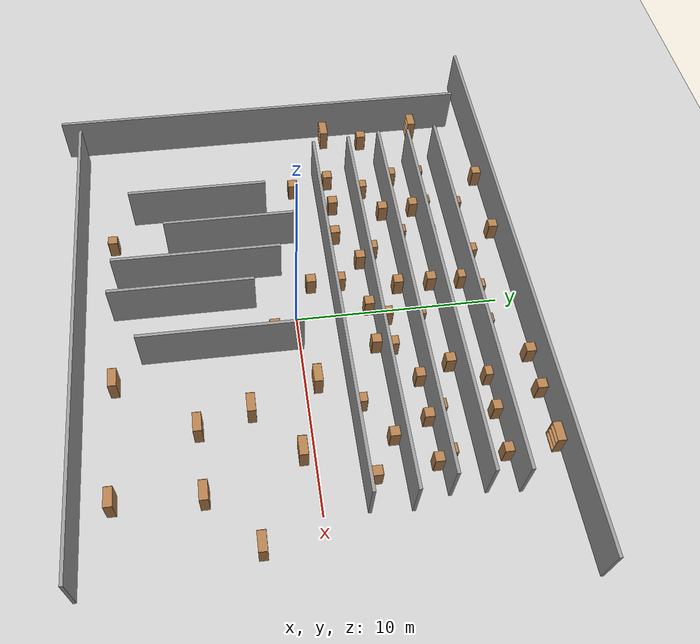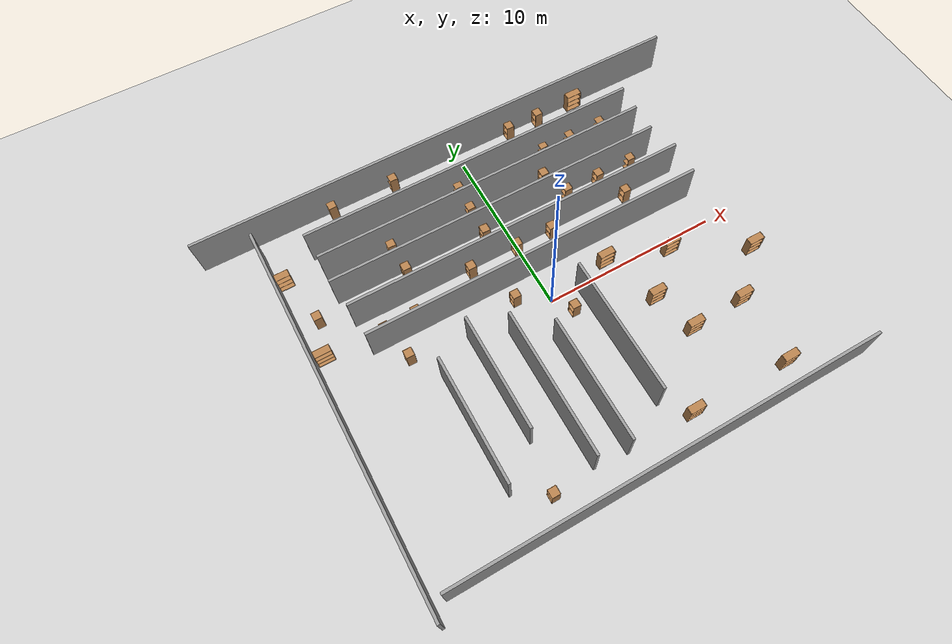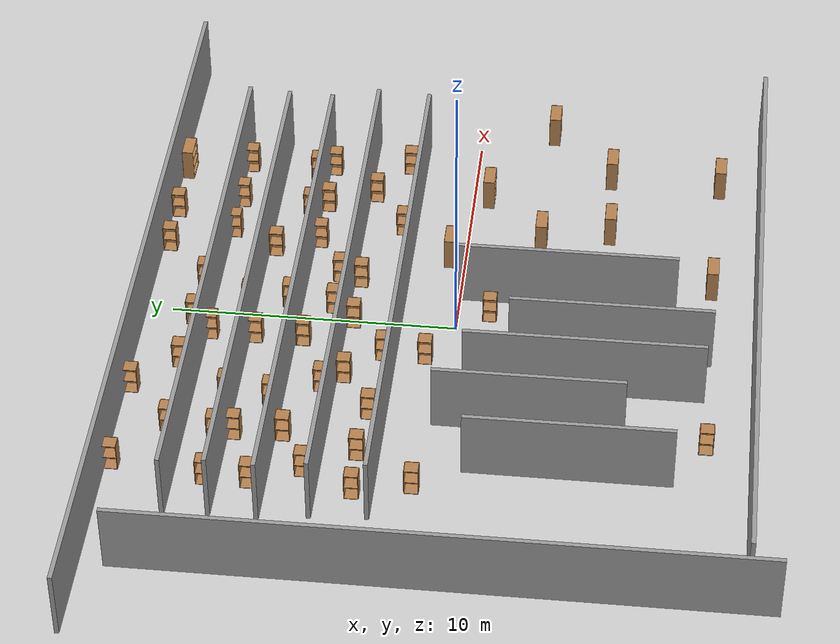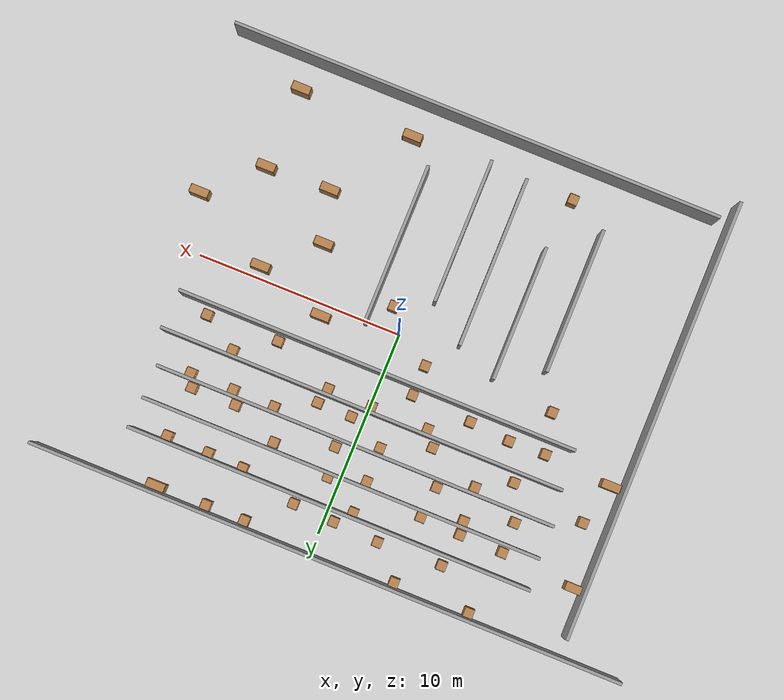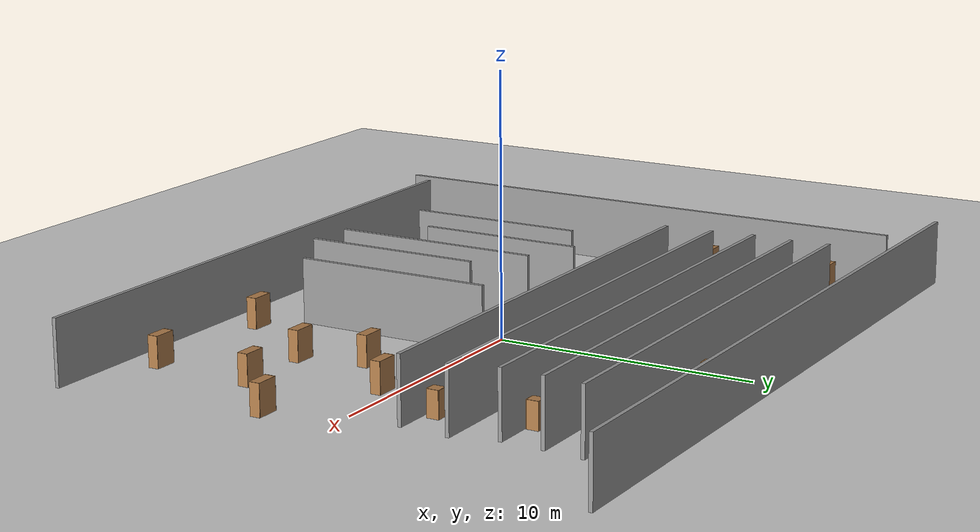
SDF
<sdf version="1.6">
 <world name="default">
  <light name="sun" type="directional">
   <pose>0 0 10 0 -0 0</pose>
   <diffuse>0.8 0.8 0.8 1</diffuse>
   <specular>0.2 0.2 0.2 1</specular>
   <attenuation>
    <range>1000</range>
    <constant>0.9</constant>
    <linear>0.01</linear>
    <quadratic>0.001</quadratic>
   </attenuation>
   <direction>-0.5 0.1 -0.9</direction>
  </light>
  <model name="ground_plane">
   <static>1</static>
   <link name="link">
    <collision name="collision">
     <geometry><plane><normal>0 0 1</normal><size>100 100</size></plane></geometry>
     <surface><friction><ode><mu>100</mu><mu2>50</mu2></ode></friction></surface>
    </collision>
    <visual name="visual">
     <cast_shadows>0</cast_shadows>
     <geometry><plane><normal>0 0 1</normal><size>100 100</size></plane></geometry>
     <material>
      <script><uri>file://media/materials/scripts/gazebo.material</uri><name>Gazebo/Grey</name></script>
     </material>
    </visual>
   </link>
  </model>
  <gravity>0 0 -9.8</gravity>
  <magnetic_field>6e-06 2.3e-05 -4.2e-05</magnetic_field>
  <atmosphere type="adiabatic"/>
  <physics name="default_physics" default="0" type="ode">
   <max_step_size>0.001</max_step_size>
   <real_time_factor>1</real_time_factor>
   <real_time_update_rate>1000</real_time_update_rate>
  </physics>
  <scene><ambient>0.4 0.4 0.4 1</ambient><background>0.7 0.7 0.7 1</background><shadows>1</shadows></scene>
  <audio><device>default</device></audio>
  <spherical_coordinates>
   <surface_model>EARTH_WGS84</surface_model>
   <latitude_deg>0</latitude_deg>
   <longitude_deg>0</longitude_deg>
   <elevation>0</elevation>
   <heading_deg>0</heading_deg>
  </spherical_coordinates>
  <model name="room18">
   <pose>-0.789818 -0.171226 0 0 -0 0</pose>
   <link name="Wall_0">
    <collision name="Wall_0_Collision">
     <geometry><box><size>29 0.15 2.5</size></box></geometry>
     <pose>0 0 1.25 0 -0 0</pose>
    </collision>
    <visual name="Wall_0_Visual">
     <pose>0 0 1.25 0 -0 0</pose>
     <geometry><box><size>29 0.15 2.5</size></box></geometry>
     <material>
      <script><uri>file://media/materials/scripts/gazebo.material</uri><name>Gazebo/Grey</name></script>
      <ambient>1 1 1 1</ambient>
     </material>
     <meta><layer>0</layer></meta>
    </visual>
    <pose>0 11.1538 0 0 -0 0</pose>
   </link>
   <link name="Wall_12">
    <collision name="Wall_12_Collision">
     <geometry><box><size>19.5 0.15 2.5</size></box></geometry>
     <pose>0 0 1.25 0 -0 0</pose>
    </collision>
    <visual name="Wall_12_Visual">
     <pose>0 0 1.25 0 -0 0</pose>
     <geometry><box><size>19.5 0.15 2.5</size></box></geometry>
     <material>
      <script><uri>file://media/materials/scripts/gazebo.material</uri><name>Gazebo/Grey</name></script>
      <ambient>1 1 1 1</ambient>
     </material>
     <meta><layer>0</layer></meta>
    </visual>
    <pose>0.703041 5.72736 0 0 -0 0</pose>
   </link>
   <link name="Wall_14">
    <collision name="Wall_14_Collision">
     <geometry><box><size>19.75 0.15 2.5</size></box></geometry>
     <pose>0 0 1.25 0 -0 0</pose>
    </collision>
    <visual name="Wall_14_Visual">
     <pose>0 0 1.25 0 -0 0</pose>
     <geometry><box><size>19.75 0.15 2.5</size></box></geometry>
     <material>
      <script><uri>file://media/materials/scripts/gazebo.material</uri><name>Gazebo/Grey</name></script>
      <ambient>1 1 1 1</ambient>
     </material>
     <meta><layer>0</layer></meta>
    </visual>
    <pose>1.06744 4.05155 0 0 -0 0</pose>
   </link>
   <link name="Wall_16">
    <collision name="Wall_16_Collision">
     <geometry><box><size>19.5 0.15 2.5</size></box></geometry>
     <pose>0 0 1.25 0 -0 0</pose>
    </collision>
    <visual name="Wall_16_Visual">
     <pose>0 0 1.25 0 -0 0</pose>
     <geometry><box><size>19.5 0.15 2.5</size></box></geometry>
     <material>
      <script><uri>file://media/materials/scripts/gazebo.material</uri><name>Gazebo/Grey</name></script>
      <ambient>1 1 1 1</ambient>
     </material>
     <meta><layer>0</layer></meta>
    </visual>
    <pose>1.07544 2.16294 0 0 -0 0</pose>
   </link>
   <link name="Wall_18">
    <collision name="Wall_18_Collision">
     <geometry><box><size>7 0.15 2.5</size></box></geometry>
     <pose>0 0 1.25 0 -0 0</pose>
    </collision>
    <visual name="Wall_18_Visual">
     <pose>0 0 1.25 0 -0 0</pose>
     <geometry><box><size>7 0.15 2.5</size></box></geometry>
     <material>
      <script><uri>file://media/materials/scripts/gazebo.material</uri><name>Gazebo/Grey</name></script>
      <ambient>1 1 1 1</ambient>
     </material>
     <meta><layer>0</layer></meta>
    </visual>
    <pose>-6.12574 -4.16148 0 0 -0 -1.5708</pose>
   </link>
   <link name="Wall_20">
    <collision name="Wall_20_Collision">
     <geometry><box><size>6.5 0.15 2.5</size></box></geometry>
     <pose>0 0 1.25 0 -0 0</pose>
    </collision>
    <visual name="Wall_20_Visual">
     <pose>0 0 1.25 0 -0 0</pose>
     <geometry><box><size>6.5 0.15 2.5</size></box></geometry>
     <material>
      <script><uri>file://media/materials/scripts/gazebo.material</uri><name>Gazebo/Grey</name></script>
      <ambient>1 1 1 1</ambient>
     </material>
     <meta><layer>0</layer></meta>
    </visual>
    <pose>-3.99772 -2.68788 0 0 -0 -1.5708</pose>
   </link>
   <link name="Wall_22">
    <collision name="Wall_22_Collision">
     <geometry><box><size>8.25 0.15 2.5</size></box></geometry>
     <pose>0 0 1.25 0 -0 0</pose>
    </collision>
    <visual name="Wall_22_Visual">
     <pose>0 0 1.25 0 -0 0</pose>
     <geometry><box><size>8.25 0.15 2.5</size></box></geometry>
     <material>
      <script><uri>file://media/materials/scripts/gazebo.material</uri><name>Gazebo/Grey</name></script>
      <ambient>1 1 1 1</ambient>
     </material>
     <meta><layer>0</layer></meta>
    </visual>
    <pose>-2.00271 -4.41408 0 0 -0 -1.5708</pose>
   </link>
   <link name="Wall_24">
    <collision name="Wall_24_Collision">
     <geometry><box><size>7 0.15 2.5</size></box></geometry>
     <pose>0 0 1.25 0 -0 0</pose>
    </collision>
    <visual name="Wall_24_Visual">
     <pose>0 0 1.25 0 -0 0</pose>
     <geometry><box><size>7 0.15 2.5</size></box></geometry>
     <material>
      <script><uri>file://media/materials/scripts/gazebo.material</uri><name>Gazebo/Grey</name></script>
      <ambient>1 1 1 1</ambient>
     </material>
     <meta><layer>0</layer></meta>
    </visual>
    <pose>-0.193893 -5.22549 0 0 -0 -1.5708</pose>
   </link>
   <link name="Wall_26">
    <collision name="Wall_26_Collision">
     <geometry><box><size>7.75 0.15 2.5</size></box></geometry>
     <pose>0 0 1.25 0 -0 0</pose>
    </collision>
    <visual name="Wall_26_Visual">
     <pose>0 0 1.25 0 -0 0</pose>
     <geometry><box><size>7.75 0.15 2.5</size></box></geometry>
     <material>
      <script><uri>file://media/materials/scripts/gazebo.material</uri><name>Gazebo/Grey</name></script>
      <ambient>1 1 1 1</ambient>
     </material>
     <meta><layer>0</layer></meta>
    </visual>
    <pose>2.41293 -3.52568 0 0 -0 -1.5708</pose>
   </link>
   <link name="Wall_3">
    <collision name="Wall_3_Collision">
     <geometry><box><size>21.5 0.15 2.5</size></box></geometry>
     <pose>0 0 1.25 0 -0 0</pose>
    </collision>
    <visual name="Wall_3_Visual">
     <pose>0 0 1.25 0 -0 0</pose>
     <geometry><box><size>21.5 0.15 2.5</size></box></geometry>
     <material>
      <script><uri>file://media/materials/scripts/gazebo.material</uri><name>Gazebo/Grey</name></script>
      <ambient>1 1 1 1</ambient>
     </material>
     <meta><layer>0</layer></meta>
    </visual>
    <pose>-11.4724 -0.478803 0 0 -0 -1.5708</pose>
   </link>
   <link name="Wall_5">
    <collision name="Wall_5_Collision">
     <geometry><box><size>24 0.15 2.5</size></box></geometry>
     <pose>0 0 1.25 0 -0 0</pose>
    </collision>
    <visual name="Wall_5_Visual">
     <pose>0 0 1.25 0 -0 0</pose>
     <geometry><box><size>24 0.15 2.5</size></box></geometry>
     <material>
      <script><uri>file://media/materials/scripts/gazebo.material</uri><name>Gazebo/Grey</name></script>
      <ambient>1 1 1 1</ambient>
     </material>
     <meta><layer>0</layer></meta>
    </visual>
    <pose>1.14423 -10.2062 0 0 -0 0</pose>
   </link>
   <link name="Wall_7">
    <collision name="Wall_7_Collision">
     <geometry><box><size>19.75 0.15 2.5</size></box></geometry>
     <pose>0 0 1.25 0 -0 0</pose>
    </collision>
    <visual name="Wall_7_Visual">
     <pose>0 0 1.25 0 -0 0</pose>
     <geometry><box><size>19.75 0.15 2.5</size></box></geometry>
     <material>
      <script><uri>file://media/materials/scripts/gazebo.material</uri><name>Gazebo/Grey</name></script>
      <ambient>1 1 1 1</ambient>
     </material>
     <meta><layer>0</layer></meta>
    </visual>
    <pose>0.74824 8.81299 0 0 -0 0</pose>
   </link>
   <link name="Wall_9">
    <collision name="Wall_9_Collision">
     <geometry><box><size>19.5 0.15 2.5</size></box></geometry>
     <pose>0 0 1.25 0 -0 0</pose>
    </collision>
    <visual name="Wall_9_Visual">
     <pose>0 0 1.25 0 -0 0</pose>
     <geometry><box><size>19.5 0.15 2.5</size></box></geometry>
     <material>
      <script><uri>file://media/materials/scripts/gazebo.material</uri><name>Gazebo/Grey</name></script>
      <ambient>1 1 1 1</ambient>
     </material>
     <meta><layer>0</layer></meta>
    </visual>
    <pose>0.756241 7.32338 0 0 -0 0</pose>
   </link>
   <static>1</static>
  </model>
  <model name="bookshelf">
   <static>1</static>
   <link name="link">
    <inertial><mass>1</mass></inertial>
    <collision name="back">
     <pose>0 0.005 0.6 0 -0 0</pose>
     <geometry><box><size>0.9 0.01 1.2</size></box></geometry>
    </collision>
    <visual name="visual1">
     <pose>0 0.005 0.6 0 -0 0</pose>
     <geometry><box><size>0.9 0.01 1.2</size></box></geometry>
     <material>
      <script><uri>file://media/materials/scripts/gazebo.material</uri><name>Gazebo/Wood</name></script>
     </material>
    </visual>
    <collision name="left_side">
     <pose>0.45 -0.195 0.6 0 -0 0</pose>
     <geometry><box><size>0.02 0.4 1.2</size></box></geometry>
    </collision>
    <visual name="visual2">
     <pose>0.45 -0.195 0.6 0 -0 0</pose>
     <geometry><box><size>0.02 0.4 1.2</size></box></geometry>
     <material>
      <script><uri>file://media/materials/scripts/gazebo.material</uri><name>Gazebo/Wood</name></script>
     </material>
    </visual>
    <collision name="right_side">
     <pose>-0.45 -0.195 0.6 0 -0 0</pose>
     <geometry><box><size>0.02 0.4 1.2</size></box></geometry>
    </collision>
    <visual name="visual3">
     <pose>-0.45 -0.195 0.6 0 -0 0</pose>
     <geometry><box><size>0.02 0.4 1.2</size></box></geometry>
     <material>
      <script><uri>file://media/materials/scripts/gazebo.material</uri><name>Gazebo/Wood</name></script>
     </material>
    </visual>
    <collision name="bottom">
     <pose>0 -0.195 0.03 0 -0 0</pose>
     <geometry><box><size>0.88 0.4 0.06</size></box></geometry>
    </collision>
    <visual name="visual4">
     <pose>0 -0.195 0.03 0 -0 0</pose>
     <geometry><box><size>0.88 0.4 0.06</size></box></geometry>
     <material>
      <script><uri>file://media/materials/scripts/gazebo.material</uri><name>Gazebo/Wood</name></script>
     </material>
    </visual>
    <collision name="top">
     <pose>0 -0.195 1.19 0 -0 0</pose>
     <geometry><box><size>0.88 0.4 0.02</size></box></geometry>
    </collision>
    <visual name="visual5">
     <pose>0 -0.195 1.19 0 -0 0</pose>
     <geometry><box><size>0.88 0.4 0.02</size></box></geometry>
     <material>
      <script><uri>file://media/materials/scripts/gazebo.material</uri><name>Gazebo/Wood</name></script>
     </material>
    </visual>
    <collision name="low_shelf">
     <pose>0 -0.195 0.43 0 -0 0</pose>
     <geometry><box><size>0.88 0.4 0.02</size></box></geometry>
    </collision>
    <visual name="visual6">
     <pose>0 -0.195 0.43 0 -0 0</pose>
     <geometry><box><size>0.88 0.4 0.02</size></box></geometry>
     <material>
      <script><uri>file://media/materials/scripts/gazebo.material</uri><name>Gazebo/Wood</name></script>
     </material>
    </visual>
    <collision name="high_shelf">
     <pose>0 -0.195 0.8 0 -0 0</pose>
     <geometry><box><size>0.88 0.4 0.02</size></box></geometry>
    </collision>
    <visual name="visual7">
     <pose>0 -0.195 0.8 0 -0 0</pose>
     <geometry><box><size>0.88 0.4 0.02</size></box></geometry>
     <material>
      <script><uri>file://media/materials/scripts/gazebo.material</uri><name>Gazebo/Wood</name></script>
     </material>
    </visual>
   </link>
   <pose>7.74898 10.872 0 0 -0 0</pose>
  </model>
  <model name="cabinet">
   <static>1</static>
   <link name="cabinet_bottom_plate">
    <inertial>
     <pose>0 0 -1 0 -0 0</pose>
     <inertia><ixx>2.05</ixx><ixy>0</ixy><ixz>0</ixz><iyy>2.05</iyy><iyz>0</iyz><izz>2.05</izz></inertia>
     <mass>25</mass>
    </inertial>
    <collision name="cabinet_bottom_plate_geom">
     <pose>0 0 0.01 0 -0 0</pose>
     <geometry><box><size>0.45 0.45 0.02</size></box></geometry>
    </collision>
    <visual name="cabinet_bottom_plate_geom_visual">
     <pose>0 0 0.01 0 -0 0</pose>
     <geometry><box><size>0.45 0.45 0.02</size></box></geometry>
     <material>
      <script><uri>file://media/materials/scripts/gazebo.material</uri><name>Gazebo/Wood</name></script>
     </material>
    </visual>
    <collision name="cabinet_bottom_plate_geom_cabinet_back_plate">
     <pose>0.235 0 0.51 0 -0 0</pose>
     <geometry><box><size>0.02 0.45 1.02</size></box></geometry>
    </collision>
    <visual name="cabinet_bottom_plate_geom_cabinet_back_plate_visual">
     <pose>0.235 0 0.51 0 -0 0</pose>
     <geometry><box><size>0.02 0.45 1.02</size></box></geometry>
     <material>
      <script><uri>file://media/materials/scripts/gazebo.material</uri><name>Gazebo/Wood</name></script>
     </material>
    </visual>
    <collision name="cabinet_bottom_plate_geom_cabinet_left_plate">
     <pose>0 0.235 0.51 0 -0 0</pose>
     <geometry><box><size>0.45 0.02 1.02</size></box></geometry>
    </collision>
    <visual name="cabinet_bottom_plate_geom_cabinet_left_plate_visual">
     <pose>0 0.235 0.51 0 -0 0</pose>
     <geometry><box><size>0.45 0.02 1.02</size></box></geometry>
     <material>
      <script><uri>file://media/materials/scripts/gazebo.material</uri><name>Gazebo/Wood</name></script>
     </material>
    </visual>
    <collision name="cabinet_bottom_plate_geom_cabinet_middle_plate">
     <pose>0 0 0.51 0 -0 0</pose>
     <geometry><box><size>0.45 0.45 0.02</size></box></geometry>
    </collision>
    <visual name="cabinet_bottom_plate_geom_cabinet_middle_plate_visual">
     <pose>0 0 0.51 0 -0 0</pose>
     <geometry><box><size>0.45 0.45 0.02</size></box></geometry>
     <material>
      <script><uri>file://media/materials/scripts/gazebo.material</uri><name>Gazebo/Wood</name></script>
     </material>
    </visual>
    <collision name="cabinet_bottom_plate_geom_cabinet_right_plate">
     <pose>0 -0.235 0.51 0 -0 0</pose>
     <geometry><box><size>0.45 0.02 1.02</size></box></geometry>
    </collision>
    <visual name="cabinet_bottom_plate_geom_cabinet_right_plate_visual">
     <pose>0 -0.235 0.51 0 -0 0</pose>
     <geometry><box><size>0.45 0.02 1.02</size></box></geometry>
     <material>
      <script><uri>file://media/materials/scripts/gazebo.material</uri><name>Gazebo/Wood</name></script>
     </material>
    </visual>
    <collision name="cabinet_bottom_plate_geom_cabinet_top_plate">
     <pose>0 0 1.01 0 -0 0</pose>
     <geometry><box><size>0.45 0.45 0.02</size></box></geometry>
    </collision>
    <visual name="cabinet_bottom_plate_geom_cabinet_top_plate_visual">
     <pose>0 0 1.01 0 -0 0</pose>
     <geometry><box><size>0.45 0.45 0.02</size></box></geometry>
     <material>
      <script><uri>file://media/materials/scripts/gazebo.material</uri><name>Gazebo/Wood</name></script>
     </material>
    </visual>
   </link>
   <pose>5.28128 10.6491 0 0 -0 0</pose>
  </model>
  <model name="cabinet_0">
   <static>1</static>
   <link name="cabinet_bottom_plate">
    <inertial>
     <pose>0 0 -1 0 -0 0</pose>
     <inertia><ixx>2.05</ixx><ixy>0</ixy><ixz>0</ixz><iyy>2.05</iyy><iyz>0</iyz><izz>2.05</izz></inertia>
     <mass>25</mass>
    </inertial>
    <collision name="cabinet_bottom_plate_geom">
     <pose>0 0 0.01 0 -0 0</pose>
     <geometry><box><size>0.45 0.45 0.02</size></box></geometry>
    </collision>
    <visual name="cabinet_bottom_plate_geom_visual">
     <pose>0 0 0.01 0 -0 0</pose>
     <geometry><box><size>0.45 0.45 0.02</size></box></geometry>
     <material>
      <script><uri>file://media/materials/scripts/gazebo.material</uri><name>Gazebo/Wood</name></script>
     </material>
    </visual>
    <collision name="cabinet_bottom_plate_geom_cabinet_back_plate">
     <pose>0.235 0 0.51 0 -0 0</pose>
     <geometry><box><size>0.02 0.45 1.02</size></box></geometry>
    </collision>
    <visual name="cabinet_bottom_plate_geom_cabinet_back_plate_visual">
     <pose>0.235 0 0.51 0 -0 0</pose>
     <geometry><box><size>0.02 0.45 1.02</size></box></geometry>
     <material>
      <script><uri>file://media/materials/scripts/gazebo.material</uri><name>Gazebo/Wood</name></script>
     </material>
    </visual>
    <collision name="cabinet_bottom_plate_geom_cabinet_left_plate">
     <pose>0 0.235 0.51 0 -0 0</pose>
     <geometry><box><size>0.45 0.02 1.02</size></box></geometry>
    </collision>
    <visual name="cabinet_bottom_plate_geom_cabinet_left_plate_visual">
     <pose>0 0.235 0.51 0 -0 0</pose>
     <geometry><box><size>0.45 0.02 1.02</size></box></geometry>
     <material>
      <script><uri>file://media/materials/scripts/gazebo.material</uri><name>Gazebo/Wood</name></script>
     </material>
    </visual>
    <collision name="cabinet_bottom_plate_geom_cabinet_middle_plate">
     <pose>0 0 0.51 0 -0 0</pose>
     <geometry><box><size>0.45 0.45 0.02</size></box></geometry>
    </collision>
    <visual name="cabinet_bottom_plate_geom_cabinet_middle_plate_visual">
     <pose>0 0 0.51 0 -0 0</pose>
     <geometry><box><size>0.45 0.45 0.02</size></box></geometry>
     <material>
      <script><uri>file://media/materials/scripts/gazebo.material</uri><name>Gazebo/Wood</name></script>
     </material>
    </visual>
    <collision name="cabinet_bottom_plate_geom_cabinet_right_plate">
     <pose>0 -0.235 0.51 0 -0 0</pose>
     <geometry><box><size>0.45 0.02 1.02</size></box></geometry>
    </collision>
    <visual name="cabinet_bottom_plate_geom_cabinet_right_plate_visual">
     <pose>0 -0.235 0.51 0 -0 0</pose>
     <geometry><box><size>0.45 0.02 1.02</size></box></geometry>
     <material>
      <script><uri>file://media/materials/scripts/gazebo.material</uri><name>Gazebo/Wood</name></script>
     </material>
    </visual>
    <collision name="cabinet_bottom_plate_geom_cabinet_top_plate">
     <pose>0 0 1.01 0 -0 0</pose>
     <geometry><box><size>0.45 0.45 0.02</size></box></geometry>
    </collision>
    <visual name="cabinet_bottom_plate_geom_cabinet_top_plate_visual">
     <pose>0 0 1.01 0 -0 0</pose>
     <geometry><box><size>0.45 0.45 0.02</size></box></geometry>
     <material>
      <script><uri>file://media/materials/scripts/gazebo.material</uri><name>Gazebo/Wood</name></script>
     </material>
    </visual>
   </link>
   <pose>3.3673 10.6414 0 0 -0 0</pose>
  </model>
  <model name="cabinet_1">
   <static>1</static>
   <link name="cabinet_bottom_plate">
    <inertial>
     <pose>0 0 -1 0 -0 0</pose>
     <inertia><ixx>2.05</ixx><ixy>0</ixy><ixz>0</ixz><iyy>2.05</iyy><iyz>0</iyz><izz>2.05</izz></inertia>
     <mass>25</mass>
    </inertial>
    <collision name="cabinet_bottom_plate_geom">
     <pose>0 0 0.01 0 -0 0</pose>
     <geometry><box><size>0.45 0.45 0.02</size></box></geometry>
    </collision>
    <visual name="cabinet_bottom_plate_geom_visual">
     <pose>0 0 0.01 0 -0 0</pose>
     <geometry><box><size>0.45 0.45 0.02</size></box></geometry>
     <material>
      <script><uri>file://media/materials/scripts/gazebo.material</uri><name>Gazebo/Wood</name></script>
     </material>
    </visual>
    <collision name="cabinet_bottom_plate_geom_cabinet_back_plate">
     <pose>0.235 0 0.51 0 -0 0</pose>
     <geometry><box><size>0.02 0.45 1.02</size></box></geometry>
    </collision>
    <visual name="cabinet_bottom_plate_geom_cabinet_back_plate_visual">
     <pose>0.235 0 0.51 0 -0 0</pose>
     <geometry><box><size>0.02 0.45 1.02</size></box></geometry>
     <material>
      <script><uri>file://media/materials/scripts/gazebo.material</uri><name>Gazebo/Wood</name></script>
     </material>
    </visual>
    <collision name="cabinet_bottom_plate_geom_cabinet_left_plate">
     <pose>0 0.235 0.51 0 -0 0</pose>
     <geometry><box><size>0.45 0.02 1.02</size></box></geometry>
    </collision>
    <visual name="cabinet_bottom_plate_geom_cabinet_left_plate_visual">
     <pose>0 0.235 0.51 0 -0 0</pose>
     <geometry><box><size>0.45 0.02 1.02</size></box></geometry>
     <material>
      <script><uri>file://media/materials/scripts/gazebo.material</uri><name>Gazebo/Wood</name></script>
     </material>
    </visual>
    <collision name="cabinet_bottom_plate_geom_cabinet_middle_plate">
     <pose>0 0 0.51 0 -0 0</pose>
     <geometry><box><size>0.45 0.45 0.02</size></box></geometry>
    </collision>
    <visual name="cabinet_bottom_plate_geom_cabinet_middle_plate_visual">
     <pose>0 0 0.51 0 -0 0</pose>
     <geometry><box><size>0.45 0.45 0.02</size></box></geometry>
     <material>
      <script><uri>file://media/materials/scripts/gazebo.material</uri><name>Gazebo/Wood</name></script>
     </material>
    </visual>
    <collision name="cabinet_bottom_plate_geom_cabinet_right_plate">
     <pose>0 -0.235 0.51 0 -0 0</pose>
     <geometry><box><size>0.45 0.02 1.02</size></box></geometry>
    </collision>
    <visual name="cabinet_bottom_plate_geom_cabinet_right_plate_visual">
     <pose>0 -0.235 0.51 0 -0 0</pose>
     <geometry><box><size>0.45 0.02 1.02</size></box></geometry>
     <material>
      <script><uri>file://media/materials/scripts/gazebo.material</uri><name>Gazebo/Wood</name></script>
     </material>
    </visual>
    <collision name="cabinet_bottom_plate_geom_cabinet_top_plate">
     <pose>0 0 1.01 0 -0 0</pose>
     <geometry><box><size>0.45 0.45 0.02</size></box></geometry>
    </collision>
    <visual name="cabinet_bottom_plate_geom_cabinet_top_plate_visual">
     <pose>0 0 1.01 0 -0 0</pose>
     <geometry><box><size>0.45 0.45 0.02</size></box></geometry>
     <material>
      <script><uri>file://media/materials/scripts/gazebo.material</uri><name>Gazebo/Wood</name></script>
     </material>
    </visual>
   </link>
   <pose>1.55819 9.08131 0 0 -0 0</pose>
  </model>
  <model name="cabinet_2">
   <static>1</static>
   <link name="cabinet_bottom_plate">
    <inertial>
     <pose>0 0 -1 0 -0 0</pose>
     <inertia><ixx>2.05</ixx><ixy>0</ixy><ixz>0</ixz><iyy>2.05</iyy><iyz>0</iyz><izz>2.05</izz></inertia>
     <mass>25</mass>
    </inertial>
    <collision name="cabinet_bottom_plate_geom">
     <pose>0 0 0.01 0 -0 0</pose>
     <geometry><box><size>0.45 0.45 0.02</size></box></geometry>
    </collision>
    <visual name="cabinet_bottom_plate_geom_visual">
     <pose>0 0 0.01 0 -0 0</pose>
     <geometry><box><size>0.45 0.45 0.02</size></box></geometry>
     <material>
      <script><uri>file://media/materials/scripts/gazebo.material</uri><name>Gazebo/Wood</name></script>
     </material>
    </visual>
    <collision name="cabinet_bottom_plate_geom_cabinet_back_plate">
     <pose>0.235 0 0.51 0 -0 0</pose>
     <geometry><box><size>0.02 0.45 1.02</size></box></geometry>
    </collision>
    <visual name="cabinet_bottom_plate_geom_cabinet_back_plate_visual">
     <pose>0.235 0 0.51 0 -0 0</pose>
     <geometry><box><size>0.02 0.45 1.02</size></box></geometry>
     <material>
      <script><uri>file://media/materials/scripts/gazebo.material</uri><name>Gazebo/Wood</name></script>
     </material>
    </visual>
    <collision name="cabinet_bottom_plate_geom_cabinet_left_plate">
     <pose>0 0.235 0.51 0 -0 0</pose>
     <geometry><box><size>0.45 0.02 1.02</size></box></geometry>
    </collision>
    <visual name="cabinet_bottom_plate_geom_cabinet_left_plate_visual">
     <pose>0 0.235 0.51 0 -0 0</pose>
     <geometry><box><size>0.45 0.02 1.02</size></box></geometry>
     <material>
      <script><uri>file://media/materials/scripts/gazebo.material</uri><name>Gazebo/Wood</name></script>
     </material>
    </visual>
    <collision name="cabinet_bottom_plate_geom_cabinet_middle_plate">
     <pose>0 0 0.51 0 -0 0</pose>
     <geometry><box><size>0.45 0.45 0.02</size></box></geometry>
    </collision>
    <visual name="cabinet_bottom_plate_geom_cabinet_middle_plate_visual">
     <pose>0 0 0.51 0 -0 0</pose>
     <geometry><box><size>0.45 0.45 0.02</size></box></geometry>
     <material>
      <script><uri>file://media/materials/scripts/gazebo.material</uri><name>Gazebo/Wood</name></script>
     </material>
    </visual>
    <collision name="cabinet_bottom_plate_geom_cabinet_right_plate">
     <pose>0 -0.235 0.51 0 -0 0</pose>
     <geometry><box><size>0.45 0.02 1.02</size></box></geometry>
    </collision>
    <visual name="cabinet_bottom_plate_geom_cabinet_right_plate_visual">
     <pose>0 -0.235 0.51 0 -0 0</pose>
     <geometry><box><size>0.45 0.02 1.02</size></box></geometry>
     <material>
      <script><uri>file://media/materials/scripts/gazebo.material</uri><name>Gazebo/Wood</name></script>
     </material>
    </visual>
    <collision name="cabinet_bottom_plate_geom_cabinet_top_plate">
     <pose>0 0 1.01 0 -0 0</pose>
     <geometry><box><size>0.45 0.45 0.02</size></box></geometry>
    </collision>
    <visual name="cabinet_bottom_plate_geom_cabinet_top_plate_visual">
     <pose>0 0 1.01 0 -0 0</pose>
     <geometry><box><size>0.45 0.45 0.02</size></box></geometry>
     <material>
      <script><uri>file://media/materials/scripts/gazebo.material</uri><name>Gazebo/Wood</name></script>
     </material>
    </visual>
   </link>
   <pose>-0.469845 9.15683 0 0 -0 0</pose>
  </model>
  <model name="cabinet_3">
   <static>1</static>
   <link name="cabinet_bottom_plate">
    <inertial>
     <pose>0 0 -1 0 -0 0</pose>
     <inertia><ixx>2.05</ixx><ixy>0</ixy><ixz>0</ixz><iyy>2.05</iyy><iyz>0</iyz><izz>2.05</izz></inertia>
     <mass>25</mass>
    </inertial>
    <collision name="cabinet_bottom_plate_geom">
     <pose>0 0 0.01 0 -0 0</pose>
     <geometry><box><size>0.45 0.45 0.02</size></box></geometry>
    </collision>
    <visual name="cabinet_bottom_plate_geom_visual">
     <pose>0 0 0.01 0 -0 0</pose>
     <geometry><box><size>0.45 0.45 0.02</size></box></geometry>
     <material>
      <script><uri>file://media/materials/scripts/gazebo.material</uri><name>Gazebo/Wood</name></script>
     </material>
    </visual>
    <collision name="cabinet_bottom_plate_geom_cabinet_back_plate">
     <pose>0.235 0 0.51 0 -0 0</pose>
     <geometry><box><size>0.02 0.45 1.02</size></box></geometry>
    </collision>
    <visual name="cabinet_bottom_plate_geom_cabinet_back_plate_visual">
     <pose>0.235 0 0.51 0 -0 0</pose>
     <geometry><box><size>0.02 0.45 1.02</size></box></geometry>
     <material>
      <script><uri>file://media/materials/scripts/gazebo.material</uri><name>Gazebo/Wood</name></script>
     </material>
    </visual>
    <collision name="cabinet_bottom_plate_geom_cabinet_left_plate">
     <pose>0 0.235 0.51 0 -0 0</pose>
     <geometry><box><size>0.45 0.02 1.02</size></box></geometry>
    </collision>
    <visual name="cabinet_bottom_plate_geom_cabinet_left_plate_visual">
     <pose>0 0.235 0.51 0 -0 0</pose>
     <geometry><box><size>0.45 0.02 1.02</size></box></geometry>
     <material>
      <script><uri>file://media/materials/scripts/gazebo.material</uri><name>Gazebo/Wood</name></script>
     </material>
    </visual>
    <collision name="cabinet_bottom_plate_geom_cabinet_middle_plate">
     <pose>0 0 0.51 0 -0 0</pose>
     <geometry><box><size>0.45 0.45 0.02</size></box></geometry>
    </collision>
    <visual name="cabinet_bottom_plate_geom_cabinet_middle_plate_visual">
     <pose>0 0 0.51 0 -0 0</pose>
     <geometry><box><size>0.45 0.45 0.02</size></box></geometry>
     <material>
      <script><uri>file://media/materials/scripts/gazebo.material</uri><name>Gazebo/Wood</name></script>
     </material>
    </visual>
    <collision name="cabinet_bottom_plate_geom_cabinet_right_plate">
     <pose>0 -0.235 0.51 0 -0 0</pose>
     <geometry><box><size>0.45 0.02 1.02</size></box></geometry>
    </collision>
    <visual name="cabinet_bottom_plate_geom_cabinet_right_plate_visual">
     <pose>0 -0.235 0.51 0 -0 0</pose>
     <geometry><box><size>0.45 0.02 1.02</size></box></geometry>
     <material>
      <script><uri>file://media/materials/scripts/gazebo.material</uri><name>Gazebo/Wood</name></script>
     </material>
    </visual>
    <collision name="cabinet_bottom_plate_geom_cabinet_top_plate">
     <pose>0 0 1.01 0 -0 0</pose>
     <geometry><box><size>0.45 0.45 0.02</size></box></geometry>
    </collision>
    <visual name="cabinet_bottom_plate_geom_cabinet_top_plate_visual">
     <pose>0 0 1.01 0 -0 0</pose>
     <geometry><box><size>0.45 0.45 0.02</size></box></geometry>
     <material>
      <script><uri>file://media/materials/scripts/gazebo.material</uri><name>Gazebo/Wood</name></script>
     </material>
    </visual>
   </link>
   <pose>-2.69733 9.26141 0 0 -0 0</pose>
  </model>
  <model name="cabinet_4">
   <static>1</static>
   <link name="cabinet_bottom_plate">
    <inertial>
     <pose>0 0 -1 0 -0 0</pose>
     <inertia><ixx>2.05</ixx><ixy>0</ixy><ixz>0</ixz><iyy>2.05</iyy><iyz>0</iyz><izz>2.05</izz></inertia>
     <mass>25</mass>
    </inertial>
    <collision name="cabinet_bottom_plate_geom">
     <pose>0 0 0.01 0 -0 0</pose>
     <geometry><box><size>0.45 0.45 0.02</size></box></geometry>
    </collision>
    <visual name="cabinet_bottom_plate_geom_visual">
     <pose>0 0 0.01 0 -0 0</pose>
     <geometry><box><size>0.45 0.45 0.02</size></box></geometry>
     <material>
      <script><uri>file://media/materials/scripts/gazebo.material</uri><name>Gazebo/Wood</name></script>
     </material>
    </visual>
    <collision name="cabinet_bottom_plate_geom_cabinet_back_plate">
     <pose>0.235 0 0.51 0 -0 0</pose>
     <geometry><box><size>0.02 0.45 1.02</size></box></geometry>
    </collision>
    <visual name="cabinet_bottom_plate_geom_cabinet_back_plate_visual">
     <pose>0.235 0 0.51 0 -0 0</pose>
     <geometry><box><size>0.02 0.45 1.02</size></box></geometry>
     <material>
      <script><uri>file://media/materials/scripts/gazebo.material</uri><name>Gazebo/Wood</name></script>
     </material>
    </visual>
    <collision name="cabinet_bottom_plate_geom_cabinet_left_plate">
     <pose>0 0.235 0.51 0 -0 0</pose>
     <geometry><box><size>0.45 0.02 1.02</size></box></geometry>
    </collision>
    <visual name="cabinet_bottom_plate_geom_cabinet_left_plate_visual">
     <pose>0 0.235 0.51 0 -0 0</pose>
     <geometry><box><size>0.45 0.02 1.02</size></box></geometry>
     <material>
      <script><uri>file://media/materials/scripts/gazebo.material</uri><name>Gazebo/Wood</name></script>
     </material>
    </visual>
    <collision name="cabinet_bottom_plate_geom_cabinet_middle_plate">
     <pose>0 0 0.51 0 -0 0</pose>
     <geometry><box><size>0.45 0.45 0.02</size></box></geometry>
    </collision>
    <visual name="cabinet_bottom_plate_geom_cabinet_middle_plate_visual">
     <pose>0 0 0.51 0 -0 0</pose>
     <geometry><box><size>0.45 0.45 0.02</size></box></geometry>
     <material>
      <script><uri>file://media/materials/scripts/gazebo.material</uri><name>Gazebo/Wood</name></script>
     </material>
    </visual>
    <collision name="cabinet_bottom_plate_geom_cabinet_right_plate">
     <pose>0 -0.235 0.51 0 -0 0</pose>
     <geometry><box><size>0.45 0.02 1.02</size></box></geometry>
    </collision>
    <visual name="cabinet_bottom_plate_geom_cabinet_right_plate_visual">
     <pose>0 -0.235 0.51 0 -0 0</pose>
     <geometry><box><size>0.45 0.02 1.02</size></box></geometry>
     <material>
      <script><uri>file://media/materials/scripts/gazebo.material</uri><name>Gazebo/Wood</name></script>
     </material>
    </visual>
    <collision name="cabinet_bottom_plate_geom_cabinet_top_plate">
     <pose>0 0 1.01 0 -0 0</pose>
     <geometry><box><size>0.45 0.45 0.02</size></box></geometry>
    </collision>
    <visual name="cabinet_bottom_plate_geom_cabinet_top_plate_visual">
     <pose>0 0 1.01 0 -0 0</pose>
     <geometry><box><size>0.45 0.45 0.02</size></box></geometry>
     <material>
      <script><uri>file://media/materials/scripts/gazebo.material</uri><name>Gazebo/Wood</name></script>
     </material>
    </visual>
   </link>
   <pose>-4.09247 10.6947 0 0 -0 0</pose>
  </model>
  <model name="cabinet_5">
   <static>1</static>
   <link name="cabinet_bottom_plate">
    <inertial>
     <pose>0 0 -1 0 -0 0</pose>
     <inertia><ixx>2.05</ixx><ixy>0</ixy><ixz>0</ixz><iyy>2.05</iyy><iyz>0</iyz><izz>2.05</izz></inertia>
     <mass>25</mass>
    </inertial>
    <collision name="cabinet_bottom_plate_geom">
     <pose>0 0 0.01 0 -0 0</pose>
     <geometry><box><size>0.45 0.45 0.02</size></box></geometry>
    </collision>
    <visual name="cabinet_bottom_plate_geom_visual">
     <pose>0 0 0.01 0 -0 0</pose>
     <geometry><box><size>0.45 0.45 0.02</size></box></geometry>
     <material>
      <script><uri>file://media/materials/scripts/gazebo.material</uri><name>Gazebo/Wood</name></script>
     </material>
    </visual>
    <collision name="cabinet_bottom_plate_geom_cabinet_back_plate">
     <pose>0.235 0 0.51 0 -0 0</pose>
     <geometry><box><size>0.02 0.45 1.02</size></box></geometry>
    </collision>
    <visual name="cabinet_bottom_plate_geom_cabinet_back_plate_visual">
     <pose>0.235 0 0.51 0 -0 0</pose>
     <geometry><box><size>0.02 0.45 1.02</size></box></geometry>
     <material>
      <script><uri>file://media/materials/scripts/gazebo.material</uri><name>Gazebo/Wood</name></script>
     </material>
    </visual>
    <collision name="cabinet_bottom_plate_geom_cabinet_left_plate">
     <pose>0 0.235 0.51 0 -0 0</pose>
     <geometry><box><size>0.45 0.02 1.02</size></box></geometry>
    </collision>
    <visual name="cabinet_bottom_plate_geom_cabinet_left_plate_visual">
     <pose>0 0.235 0.51 0 -0 0</pose>
     <geometry><box><size>0.45 0.02 1.02</size></box></geometry>
     <material>
      <script><uri>file://media/materials/scripts/gazebo.material</uri><name>Gazebo/Wood</name></script>
     </material>
    </visual>
    <collision name="cabinet_bottom_plate_geom_cabinet_middle_plate">
     <pose>0 0 0.51 0 -0 0</pose>
     <geometry><box><size>0.45 0.45 0.02</size></box></geometry>
    </collision>
    <visual name="cabinet_bottom_plate_geom_cabinet_middle_plate_visual">
     <pose>0 0 0.51 0 -0 0</pose>
     <geometry><box><size>0.45 0.45 0.02</size></box></geometry>
     <material>
      <script><uri>file://media/materials/scripts/gazebo.material</uri><name>Gazebo/Wood</name></script>
     </material>
    </visual>
    <collision name="cabinet_bottom_plate_geom_cabinet_right_plate">
     <pose>0 -0.235 0.51 0 -0 0</pose>
     <geometry><box><size>0.45 0.02 1.02</size></box></geometry>
    </collision>
    <visual name="cabinet_bottom_plate_geom_cabinet_right_plate_visual">
     <pose>0 -0.235 0.51 0 -0 0</pose>
     <geometry><box><size>0.45 0.02 1.02</size></box></geometry>
     <material>
      <script><uri>file://media/materials/scripts/gazebo.material</uri><name>Gazebo/Wood</name></script>
     </material>
    </visual>
    <collision name="cabinet_bottom_plate_geom_cabinet_top_plate">
     <pose>0 0 1.01 0 -0 0</pose>
     <geometry><box><size>0.45 0.45 0.02</size></box></geometry>
    </collision>
    <visual name="cabinet_bottom_plate_geom_cabinet_top_plate_visual">
     <pose>0 0 1.01 0 -0 0</pose>
     <geometry><box><size>0.45 0.45 0.02</size></box></geometry>
     <material>
      <script><uri>file://media/materials/scripts/gazebo.material</uri><name>Gazebo/Wood</name></script>
     </material>
    </visual>
   </link>
   <pose>-5.83195 9.14808 0 0 -0 0</pose>
  </model>
  <model name="cabinet_6">
   <static>1</static>
   <link name="cabinet_bottom_plate">
    <inertial>
     <pose>0 0 -1 0 -0 0</pose>
     <inertia><ixx>2.05</ixx><ixy>0</ixy><ixz>0</ixz><iyy>2.05</iyy><iyz>0</iyz><izz>2.05</izz></inertia>
     <mass>25</mass>
    </inertial>
    <collision name="cabinet_bottom_plate_geom">
     <pose>0 0 0.01 0 -0 0</pose>
     <geometry><box><size>0.45 0.45 0.02</size></box></geometry>
    </collision>
    <visual name="cabinet_bottom_plate_geom_visual">
     <pose>0 0 0.01 0 -0 0</pose>
     <geometry><box><size>0.45 0.45 0.02</size></box></geometry>
     <material>
      <script><uri>file://media/materials/scripts/gazebo.material</uri><name>Gazebo/Wood</name></script>
     </material>
    </visual>
    <collision name="cabinet_bottom_plate_geom_cabinet_back_plate">
     <pose>0.235 0 0.51 0 -0 0</pose>
     <geometry><box><size>0.02 0.45 1.02</size></box></geometry>
    </collision>
    <visual name="cabinet_bottom_plate_geom_cabinet_back_plate_visual">
     <pose>0.235 0 0.51 0 -0 0</pose>
     <geometry><box><size>0.02 0.45 1.02</size></box></geometry>
     <material>
      <script><uri>file://media/materials/scripts/gazebo.material</uri><name>Gazebo/Wood</name></script>
     </material>
    </visual>
    <collision name="cabinet_bottom_plate_geom_cabinet_left_plate">
     <pose>0 0.235 0.51 0 -0 0</pose>
     <geometry><box><size>0.45 0.02 1.02</size></box></geometry>
    </collision>
    <visual name="cabinet_bottom_plate_geom_cabinet_left_plate_visual">
     <pose>0 0.235 0.51 0 -0 0</pose>
     <geometry><box><size>0.45 0.02 1.02</size></box></geometry>
     <material>
      <script><uri>file://media/materials/scripts/gazebo.material</uri><name>Gazebo/Wood</name></script>
     </material>
    </visual>
    <collision name="cabinet_bottom_plate_geom_cabinet_middle_plate">
     <pose>0 0 0.51 0 -0 0</pose>
     <geometry><box><size>0.45 0.45 0.02</size></box></geometry>
    </collision>
    <visual name="cabinet_bottom_plate_geom_cabinet_middle_plate_visual">
     <pose>0 0 0.51 0 -0 0</pose>
     <geometry><box><size>0.45 0.45 0.02</size></box></geometry>
     <material>
      <script><uri>file://media/materials/scripts/gazebo.material</uri><name>Gazebo/Wood</name></script>
     </material>
    </visual>
    <collision name="cabinet_bottom_plate_geom_cabinet_right_plate">
     <pose>0 -0.235 0.51 0 -0 0</pose>
     <geometry><box><size>0.45 0.02 1.02</size></box></geometry>
    </collision>
    <visual name="cabinet_bottom_plate_geom_cabinet_right_plate_visual">
     <pose>0 -0.235 0.51 0 -0 0</pose>
     <geometry><box><size>0.45 0.02 1.02</size></box></geometry>
     <material>
      <script><uri>file://media/materials/scripts/gazebo.material</uri><name>Gazebo/Wood</name></script>
     </material>
    </visual>
    <collision name="cabinet_bottom_plate_geom_cabinet_top_plate">
     <pose>0 0 1.01 0 -0 0</pose>
     <geometry><box><size>0.45 0.45 0.02</size></box></geometry>
    </collision>
    <visual name="cabinet_bottom_plate_geom_cabinet_top_plate_visual">
     <pose>0 0 1.01 0 -0 0</pose>
     <geometry><box><size>0.45 0.45 0.02</size></box></geometry>
     <material>
      <script><uri>file://media/materials/scripts/gazebo.material</uri><name>Gazebo/Wood</name></script>
     </material>
    </visual>
   </link>
   <pose>-7.78731 10.6921 0 0 -0 0</pose>
  </model>
  <model name="cabinet_7">
   <static>1</static>
   <link name="cabinet_bottom_plate">
    <inertial>
     <pose>0 0 -1 0 -0 0</pose>
     <inertia><ixx>2.05</ixx><ixy>0</ixy><ixz>0</ixz><iyy>2.05</iyy><iyz>0</iyz><izz>2.05</izz></inertia>
     <mass>25</mass>
    </inertial>
    <collision name="cabinet_bottom_plate_geom">
     <pose>0 0 0.01 0 -0 0</pose>
     <geometry><box><size>0.45 0.45 0.02</size></box></geometry>
    </collision>
    <visual name="cabinet_bottom_plate_geom_visual">
     <pose>0 0 0.01 0 -0 0</pose>
     <geometry><box><size>0.45 0.45 0.02</size></box></geometry>
     <material>
      <script><uri>file://media/materials/scripts/gazebo.material</uri><name>Gazebo/Wood</name></script>
     </material>
    </visual>
    <collision name="cabinet_bottom_plate_geom_cabinet_back_plate">
     <pose>0.235 0 0.51 0 -0 0</pose>
     <geometry><box><size>0.02 0.45 1.02</size></box></geometry>
    </collision>
    <visual name="cabinet_bottom_plate_geom_cabinet_back_plate_visual">
     <pose>0.235 0 0.51 0 -0 0</pose>
     <geometry><box><size>0.02 0.45 1.02</size></box></geometry>
     <material>
      <script><uri>file://media/materials/scripts/gazebo.material</uri><name>Gazebo/Wood</name></script>
     </material>
    </visual>
    <collision name="cabinet_bottom_plate_geom_cabinet_left_plate">
     <pose>0 0.235 0.51 0 -0 0</pose>
     <geometry><box><size>0.45 0.02 1.02</size></box></geometry>
    </collision>
    <visual name="cabinet_bottom_plate_geom_cabinet_left_plate_visual">
     <pose>0 0.235 0.51 0 -0 0</pose>
     <geometry><box><size>0.45 0.02 1.02</size></box></geometry>
     <material>
      <script><uri>file://media/materials/scripts/gazebo.material</uri><name>Gazebo/Wood</name></script>
     </material>
    </visual>
    <collision name="cabinet_bottom_plate_geom_cabinet_middle_plate">
     <pose>0 0 0.51 0 -0 0</pose>
     <geometry><box><size>0.45 0.45 0.02</size></box></geometry>
    </collision>
    <visual name="cabinet_bottom_plate_geom_cabinet_middle_plate_visual">
     <pose>0 0 0.51 0 -0 0</pose>
     <geometry><box><size>0.45 0.45 0.02</size></box></geometry>
     <material>
      <script><uri>file://media/materials/scripts/gazebo.material</uri><name>Gazebo/Wood</name></script>
     </material>
    </visual>
    <collision name="cabinet_bottom_plate_geom_cabinet_right_plate">
     <pose>0 -0.235 0.51 0 -0 0</pose>
     <geometry><box><size>0.45 0.02 1.02</size></box></geometry>
    </collision>
    <visual name="cabinet_bottom_plate_geom_cabinet_right_plate_visual">
     <pose>0 -0.235 0.51 0 -0 0</pose>
     <geometry><box><size>0.45 0.02 1.02</size></box></geometry>
     <material>
      <script><uri>file://media/materials/scripts/gazebo.material</uri><name>Gazebo/Wood</name></script>
     </material>
    </visual>
    <collision name="cabinet_bottom_plate_geom_cabinet_top_plate">
     <pose>0 0 1.01 0 -0 0</pose>
     <geometry><box><size>0.45 0.45 0.02</size></box></geometry>
    </collision>
    <visual name="cabinet_bottom_plate_geom_cabinet_top_plate_visual">
     <pose>0 0 1.01 0 -0 0</pose>
     <geometry><box><size>0.45 0.45 0.02</size></box></geometry>
     <material>
      <script><uri>file://media/materials/scripts/gazebo.material</uri><name>Gazebo/Wood</name></script>
     </material>
    </visual>
   </link>
   <pose>8.13676 8.37707 0 0 -0 0</pose>
  </model>
  <model name="cabinet_8">
   <static>1</static>
   <link name="cabinet_bottom_plate">
    <inertial>
     <pose>0 0 -1 0 -0 0</pose>
     <inertia><ixx>2.05</ixx><ixy>0</ixy><ixz>0</ixz><iyy>2.05</iyy><iyz>0</iyz><izz>2.05</izz></inertia>
     <mass>25</mass>
    </inertial>
    <collision name="cabinet_bottom_plate_geom">
     <pose>0 0 0.01 0 -0 0</pose>
     <geometry><box><size>0.45 0.45 0.02</size></box></geometry>
    </collision>
    <visual name="cabinet_bottom_plate_geom_visual">
     <pose>0 0 0.01 0 -0 0</pose>
     <geometry><box><size>0.45 0.45 0.02</size></box></geometry>
     <material>
      <script><uri>file://media/materials/scripts/gazebo.material</uri><name>Gazebo/Wood</name></script>
     </material>
    </visual>
    <collision name="cabinet_bottom_plate_geom_cabinet_back_plate">
     <pose>0.235 0 0.51 0 -0 0</pose>
     <geometry><box><size>0.02 0.45 1.02</size></box></geometry>
    </collision>
    <visual name="cabinet_bottom_plate_geom_cabinet_back_plate_visual">
     <pose>0.235 0 0.51 0 -0 0</pose>
     <geometry><box><size>0.02 0.45 1.02</size></box></geometry>
     <material>
      <script><uri>file://media/materials/scripts/gazebo.material</uri><name>Gazebo/Wood</name></script>
     </material>
    </visual>
    <collision name="cabinet_bottom_plate_geom_cabinet_left_plate">
     <pose>0 0.235 0.51 0 -0 0</pose>
     <geometry><box><size>0.45 0.02 1.02</size></box></geometry>
    </collision>
    <visual name="cabinet_bottom_plate_geom_cabinet_left_plate_visual">
     <pose>0 0.235 0.51 0 -0 0</pose>
     <geometry><box><size>0.45 0.02 1.02</size></box></geometry>
     <material>
      <script><uri>file://media/materials/scripts/gazebo.material</uri><name>Gazebo/Wood</name></script>
     </material>
    </visual>
    <collision name="cabinet_bottom_plate_geom_cabinet_middle_plate">
     <pose>0 0 0.51 0 -0 0</pose>
     <geometry><box><size>0.45 0.45 0.02</size></box></geometry>
    </collision>
    <visual name="cabinet_bottom_plate_geom_cabinet_middle_plate_visual">
     <pose>0 0 0.51 0 -0 0</pose>
     <geometry><box><size>0.45 0.45 0.02</size></box></geometry>
     <material>
      <script><uri>file://media/materials/scripts/gazebo.material</uri><name>Gazebo/Wood</name></script>
     </material>
    </visual>
    <collision name="cabinet_bottom_plate_geom_cabinet_right_plate">
     <pose>0 -0.235 0.51 0 -0 0</pose>
     <geometry><box><size>0.45 0.02 1.02</size></box></geometry>
    </collision>
    <visual name="cabinet_bottom_plate_geom_cabinet_right_plate_visual">
     <pose>0 -0.235 0.51 0 -0 0</pose>
     <geometry><box><size>0.45 0.02 1.02</size></box></geometry>
     <material>
      <script><uri>file://media/materials/scripts/gazebo.material</uri><name>Gazebo/Wood</name></script>
     </material>
    </visual>
    <collision name="cabinet_bottom_plate_geom_cabinet_top_plate">
     <pose>0 0 1.01 0 -0 0</pose>
     <geometry><box><size>0.45 0.45 0.02</size></box></geometry>
    </collision>
    <visual name="cabinet_bottom_plate_geom_cabinet_top_plate_visual">
     <pose>0 0 1.01 0 -0 0</pose>
     <geometry><box><size>0.45 0.45 0.02</size></box></geometry>
     <material>
      <script><uri>file://media/materials/scripts/gazebo.material</uri><name>Gazebo/Wood</name></script>
     </material>
    </visual>
   </link>
   <pose>6.09286 8.39011 0 0 -0 0</pose>
  </model>
  <model name="cabinet_9">
   <static>1</static>
   <link name="cabinet_bottom_plate">
    <inertial>
     <pose>0 0 -1 0 -0 0</pose>
     <inertia><ixx>2.05</ixx><ixy>0</ixy><ixz>0</ixz><iyy>2.05</iyy><iyz>0</iyz><izz>2.05</izz></inertia>
     <mass>25</mass>
    </inertial>
    <collision name="cabinet_bottom_plate_geom">
     <pose>0 0 0.01 0 -0 0</pose>
     <geometry><box><size>0.45 0.45 0.02</size></box></geometry>
    </collision>
    <visual name="cabinet_bottom_plate_geom_visual">
     <pose>0 0 0.01 0 -0 0</pose>
     <geometry><box><size>0.45 0.45 0.02</size></box></geometry>
     <material>
      <script><uri>file://media/materials/scripts/gazebo.material</uri><name>Gazebo/Wood</name></script>
     </material>
    </visual>
    <collision name="cabinet_bottom_plate_geom_cabinet_back_plate">
     <pose>0.235 0 0.51 0 -0 0</pose>
     <geometry><box><size>0.02 0.45 1.02</size></box></geometry>
    </collision>
    <visual name="cabinet_bottom_plate_geom_cabinet_back_plate_visual">
     <pose>0.235 0 0.51 0 -0 0</pose>
     <geometry><box><size>0.02 0.45 1.02</size></box></geometry>
     <material>
      <script><uri>file://media/materials/scripts/gazebo.material</uri><name>Gazebo/Wood</name></script>
     </material>
    </visual>
    <collision name="cabinet_bottom_plate_geom_cabinet_left_plate">
     <pose>0 0.235 0.51 0 -0 0</pose>
     <geometry><box><size>0.45 0.02 1.02</size></box></geometry>
    </collision>
    <visual name="cabinet_bottom_plate_geom_cabinet_left_plate_visual">
     <pose>0 0.235 0.51 0 -0 0</pose>
     <geometry><box><size>0.45 0.02 1.02</size></box></geometry>
     <material>
      <script><uri>file://media/materials/scripts/gazebo.material</uri><name>Gazebo/Wood</name></script>
     </material>
    </visual>
    <collision name="cabinet_bottom_plate_geom_cabinet_middle_plate">
     <pose>0 0 0.51 0 -0 0</pose>
     <geometry><box><size>0.45 0.45 0.02</size></box></geometry>
    </collision>
    <visual name="cabinet_bottom_plate_geom_cabinet_middle_plate_visual">
     <pose>0 0 0.51 0 -0 0</pose>
     <geometry><box><size>0.45 0.45 0.02</size></box></geometry>
     <material>
      <script><uri>file://media/materials/scripts/gazebo.material</uri><name>Gazebo/Wood</name></script>
     </material>
    </visual>
    <collision name="cabinet_bottom_plate_geom_cabinet_right_plate">
     <pose>0 -0.235 0.51 0 -0 0</pose>
     <geometry><box><size>0.45 0.02 1.02</size></box></geometry>
    </collision>
    <visual name="cabinet_bottom_plate_geom_cabinet_right_plate_visual">
     <pose>0 -0.235 0.51 0 -0 0</pose>
     <geometry><box><size>0.45 0.02 1.02</size></box></geometry>
     <material>
      <script><uri>file://media/materials/scripts/gazebo.material</uri><name>Gazebo/Wood</name></script>
     </material>
    </visual>
    <collision name="cabinet_bottom_plate_geom_cabinet_top_plate">
     <pose>0 0 1.01 0 -0 0</pose>
     <geometry><box><size>0.45 0.45 0.02</size></box></geometry>
    </collision>
    <visual name="cabinet_bottom_plate_geom_cabinet_top_plate_visual">
     <pose>0 0 1.01 0 -0 0</pose>
     <geometry><box><size>0.45 0.45 0.02</size></box></geometry>
     <material>
      <script><uri>file://media/materials/scripts/gazebo.material</uri><name>Gazebo/Wood</name></script>
     </material>
    </visual>
   </link>
   <pose>4.3592 8.44647 0 0 -0 0</pose>
  </model>
  <model name="cabinet_10">
   <static>1</static>
   <link name="cabinet_bottom_plate">
    <inertial>
     <pose>0 0 -1 0 -0 0</pose>
     <inertia><ixx>2.05</ixx><ixy>0</ixy><ixz>0</ixz><iyy>2.05</iyy><iyz>0</iyz><izz>2.05</izz></inertia>
     <mass>25</mass>
    </inertial>
    <collision name="cabinet_bottom_plate_geom">
     <pose>0 0 0.01 0 -0 0</pose>
     <geometry><box><size>0.45 0.45 0.02</size></box></geometry>
    </collision>
    <visual name="cabinet_bottom_plate_geom_visual">
     <pose>0 0 0.01 0 -0 0</pose>
     <geometry><box><size>0.45 0.45 0.02</size></box></geometry>
     <material>
      <script><uri>file://media/materials/scripts/gazebo.material</uri><name>Gazebo/Wood</name></script>
     </material>
    </visual>
    <collision name="cabinet_bottom_plate_geom_cabinet_back_plate">
     <pose>0.235 0 0.51 0 -0 0</pose>
     <geometry><box><size>0.02 0.45 1.02</size></box></geometry>
    </collision>
    <visual name="cabinet_bottom_plate_geom_cabinet_back_plate_visual">
     <pose>0.235 0 0.51 0 -0 0</pose>
     <geometry><box><size>0.02 0.45 1.02</size></box></geometry>
     <material>
      <script><uri>file://media/materials/scripts/gazebo.material</uri><name>Gazebo/Wood</name></script>
     </material>
    </visual>
    <collision name="cabinet_bottom_plate_geom_cabinet_left_plate">
     <pose>0 0.235 0.51 0 -0 0</pose>
     <geometry><box><size>0.45 0.02 1.02</size></box></geometry>
    </collision>
    <visual name="cabinet_bottom_plate_geom_cabinet_left_plate_visual">
     <pose>0 0.235 0.51 0 -0 0</pose>
     <geometry><box><size>0.45 0.02 1.02</size></box></geometry>
     <material>
      <script><uri>file://media/materials/scripts/gazebo.material</uri><name>Gazebo/Wood</name></script>
     </material>
    </visual>
    <collision name="cabinet_bottom_plate_geom_cabinet_middle_plate">
     <pose>0 0 0.51 0 -0 0</pose>
     <geometry><box><size>0.45 0.45 0.02</size></box></geometry>
    </collision>
    <visual name="cabinet_bottom_plate_geom_cabinet_middle_plate_visual">
     <pose>0 0 0.51 0 -0 0</pose>
     <geometry><box><size>0.45 0.45 0.02</size></box></geometry>
     <material>
      <script><uri>file://media/materials/scripts/gazebo.material</uri><name>Gazebo/Wood</name></script>
     </material>
    </visual>
    <collision name="cabinet_bottom_plate_geom_cabinet_right_plate">
     <pose>0 -0.235 0.51 0 -0 0</pose>
     <geometry><box><size>0.45 0.02 1.02</size></box></geometry>
    </collision>
    <visual name="cabinet_bottom_plate_geom_cabinet_right_plate_visual">
     <pose>0 -0.235 0.51 0 -0 0</pose>
     <geometry><box><size>0.45 0.02 1.02</size></box></geometry>
     <material>
      <script><uri>file://media/materials/scripts/gazebo.material</uri><name>Gazebo/Wood</name></script>
     </material>
    </visual>
    <collision name="cabinet_bottom_plate_geom_cabinet_top_plate">
     <pose>0 0 1.01 0 -0 0</pose>
     <geometry><box><size>0.45 0.45 0.02</size></box></geometry>
    </collision>
    <visual name="cabinet_bottom_plate_geom_cabinet_top_plate_visual">
     <pose>0 0 1.01 0 -0 0</pose>
     <geometry><box><size>0.45 0.45 0.02</size></box></geometry>
     <material>
      <script><uri>file://media/materials/scripts/gazebo.material</uri><name>Gazebo/Wood</name></script>
     </material>
    </visual>
   </link>
   <pose>0.54763 7.35241 0 0 -0 0</pose>
  </model>
  <model name="cabinet_11">
   <static>1</static>
   <link name="cabinet_bottom_plate">
    <inertial>
     <pose>0 0 -1 0 -0 0</pose>
     <inertia><ixx>2.05</ixx><ixy>0</ixy><ixz>0</ixz><iyy>2.05</iyy><iyz>0</iyz><izz>2.05</izz></inertia>
     <mass>25</mass>
    </inertial>
    <collision name="cabinet_bottom_plate_geom">
     <pose>0 0 0.01 0 -0 0</pose>
     <geometry><box><size>0.45 0.45 0.02</size></box></geometry>
    </collision>
    <visual name="cabinet_bottom_plate_geom_visual">
     <pose>0 0 0.01 0 -0 0</pose>
     <geometry><box><size>0.45 0.45 0.02</size></box></geometry>
     <material>
      <script><uri>file://media/materials/scripts/gazebo.material</uri><name>Gazebo/Wood</name></script>
     </material>
    </visual>
    <collision name="cabinet_bottom_plate_geom_cabinet_back_plate">
     <pose>0.235 0 0.51 0 -0 0</pose>
     <geometry><box><size>0.02 0.45 1.02</size></box></geometry>
    </collision>
    <visual name="cabinet_bottom_plate_geom_cabinet_back_plate_visual">
     <pose>0.235 0 0.51 0 -0 0</pose>
     <geometry><box><size>0.02 0.45 1.02</size></box></geometry>
     <material>
      <script><uri>file://media/materials/scripts/gazebo.material</uri><name>Gazebo/Wood</name></script>
     </material>
    </visual>
    <collision name="cabinet_bottom_plate_geom_cabinet_left_plate">
     <pose>0 0.235 0.51 0 -0 0</pose>
     <geometry><box><size>0.45 0.02 1.02</size></box></geometry>
    </collision>
    <visual name="cabinet_bottom_plate_geom_cabinet_left_plate_visual">
     <pose>0 0.235 0.51 0 -0 0</pose>
     <geometry><box><size>0.45 0.02 1.02</size></box></geometry>
     <material>
      <script><uri>file://media/materials/scripts/gazebo.material</uri><name>Gazebo/Wood</name></script>
     </material>
    </visual>
    <collision name="cabinet_bottom_plate_geom_cabinet_middle_plate">
     <pose>0 0 0.51 0 -0 0</pose>
     <geometry><box><size>0.45 0.45 0.02</size></box></geometry>
    </collision>
    <visual name="cabinet_bottom_plate_geom_cabinet_middle_plate_visual">
     <pose>0 0 0.51 0 -0 0</pose>
     <geometry><box><size>0.45 0.45 0.02</size></box></geometry>
     <material>
      <script><uri>file://media/materials/scripts/gazebo.material</uri><name>Gazebo/Wood</name></script>
     </material>
    </visual>
    <collision name="cabinet_bottom_plate_geom_cabinet_right_plate">
     <pose>0 -0.235 0.51 0 -0 0</pose>
     <geometry><box><size>0.45 0.02 1.02</size></box></geometry>
    </collision>
    <visual name="cabinet_bottom_plate_geom_cabinet_right_plate_visual">
     <pose>0 -0.235 0.51 0 -0 0</pose>
     <geometry><box><size>0.45 0.02 1.02</size></box></geometry>
     <material>
      <script><uri>file://media/materials/scripts/gazebo.material</uri><name>Gazebo/Wood</name></script>
     </material>
    </visual>
    <collision name="cabinet_bottom_plate_geom_cabinet_top_plate">
     <pose>0 0 1.01 0 -0 0</pose>
     <geometry><box><size>0.45 0.45 0.02</size></box></geometry>
    </collision>
    <visual name="cabinet_bottom_plate_geom_cabinet_top_plate_visual">
     <pose>0 0 1.01 0 -0 0</pose>
     <geometry><box><size>0.45 0.45 0.02</size></box></geometry>
     <material>
      <script><uri>file://media/materials/scripts/gazebo.material</uri><name>Gazebo/Wood</name></script>
     </material>
    </visual>
   </link>
   <pose>-1.14087 8.42958 0 0 -0 0</pose>
  </model>
  <model name="cabinet_12">
   <static>1</static>
   <link name="cabinet_bottom_plate">
    <inertial>
     <pose>0 0 -1 0 -0 0</pose>
     <inertia><ixx>2.05</ixx><ixy>0</ixy><ixz>0</ixz><iyy>2.05</iyy><iyz>0</iyz><izz>2.05</izz></inertia>
     <mass>25</mass>
    </inertial>
    <collision name="cabinet_bottom_plate_geom">
     <pose>0 0 0.01 0 -0 0</pose>
     <geometry><box><size>0.45 0.45 0.02</size></box></geometry>
    </collision>
    <visual name="cabinet_bottom_plate_geom_visual">
     <pose>0 0 0.01 0 -0 0</pose>
     <geometry><box><size>0.45 0.45 0.02</size></box></geometry>
     <material>
      <script><uri>file://media/materials/scripts/gazebo.material</uri><name>Gazebo/Wood</name></script>
     </material>
    </visual>
    <collision name="cabinet_bottom_plate_geom_cabinet_back_plate">
     <pose>0.235 0 0.51 0 -0 0</pose>
     <geometry><box><size>0.02 0.45 1.02</size></box></geometry>
    </collision>
    <visual name="cabinet_bottom_plate_geom_cabinet_back_plate_visual">
     <pose>0.235 0 0.51 0 -0 0</pose>
     <geometry><box><size>0.02 0.45 1.02</size></box></geometry>
     <material>
      <script><uri>file://media/materials/scripts/gazebo.material</uri><name>Gazebo/Wood</name></script>
     </material>
    </visual>
    <collision name="cabinet_bottom_plate_geom_cabinet_left_plate">
     <pose>0 0.235 0.51 0 -0 0</pose>
     <geometry><box><size>0.45 0.02 1.02</size></box></geometry>
    </collision>
    <visual name="cabinet_bottom_plate_geom_cabinet_left_plate_visual">
     <pose>0 0.235 0.51 0 -0 0</pose>
     <geometry><box><size>0.45 0.02 1.02</size></box></geometry>
     <material>
      <script><uri>file://media/materials/scripts/gazebo.material</uri><name>Gazebo/Wood</name></script>
     </material>
    </visual>
    <collision name="cabinet_bottom_plate_geom_cabinet_middle_plate">
     <pose>0 0 0.51 0 -0 0</pose>
     <geometry><box><size>0.45 0.45 0.02</size></box></geometry>
    </collision>
    <visual name="cabinet_bottom_plate_geom_cabinet_middle_plate_visual">
     <pose>0 0 0.51 0 -0 0</pose>
     <geometry><box><size>0.45 0.45 0.02</size></box></geometry>
     <material>
      <script><uri>file://media/materials/scripts/gazebo.material</uri><name>Gazebo/Wood</name></script>
     </material>
    </visual>
    <collision name="cabinet_bottom_plate_geom_cabinet_right_plate">
     <pose>0 -0.235 0.51 0 -0 0</pose>
     <geometry><box><size>0.45 0.02 1.02</size></box></geometry>
    </collision>
    <visual name="cabinet_bottom_plate_geom_cabinet_right_plate_visual">
     <pose>0 -0.235 0.51 0 -0 0</pose>
     <geometry><box><size>0.45 0.02 1.02</size></box></geometry>
     <material>
      <script><uri>file://media/materials/scripts/gazebo.material</uri><name>Gazebo/Wood</name></script>
     </material>
    </visual>
    <collision name="cabinet_bottom_plate_geom_cabinet_top_plate">
     <pose>0 0 1.01 0 -0 0</pose>
     <geometry><box><size>0.45 0.45 0.02</size></box></geometry>
    </collision>
    <visual name="cabinet_bottom_plate_geom_cabinet_top_plate_visual">
     <pose>0 0 1.01 0 -0 0</pose>
     <geometry><box><size>0.45 0.45 0.02</size></box></geometry>
     <material>
      <script><uri>file://media/materials/scripts/gazebo.material</uri><name>Gazebo/Wood</name></script>
     </material>
    </visual>
   </link>
   <pose>-4.11624 7.44312 0 0 -0 0</pose>
  </model>
  <model name="cabinet_13">
   <static>1</static>
   <link name="cabinet_bottom_plate">
    <inertial>
     <pose>0 0 -1 0 -0 0</pose>
     <inertia><ixx>2.05</ixx><ixy>0</ixy><ixz>0</ixz><iyy>2.05</iyy><iyz>0</iyz><izz>2.05</izz></inertia>
     <mass>25</mass>
    </inertial>
    <collision name="cabinet_bottom_plate_geom">
     <pose>0 0 0.01 0 -0 0</pose>
     <geometry><box><size>0.45 0.45 0.02</size></box></geometry>
    </collision>
    <visual name="cabinet_bottom_plate_geom_visual">
     <pose>0 0 0.01 0 -0 0</pose>
     <geometry><box><size>0.45 0.45 0.02</size></box></geometry>
     <material>
      <script><uri>file://media/materials/scripts/gazebo.material</uri><name>Gazebo/Wood</name></script>
     </material>
    </visual>
    <collision name="cabinet_bottom_plate_geom_cabinet_back_plate">
     <pose>0.235 0 0.51 0 -0 0</pose>
     <geometry><box><size>0.02 0.45 1.02</size></box></geometry>
    </collision>
    <visual name="cabinet_bottom_plate_geom_cabinet_back_plate_visual">
     <pose>0.235 0 0.51 0 -0 0</pose>
     <geometry><box><size>0.02 0.45 1.02</size></box></geometry>
     <material>
      <script><uri>file://media/materials/scripts/gazebo.material</uri><name>Gazebo/Wood</name></script>
     </material>
    </visual>
    <collision name="cabinet_bottom_plate_geom_cabinet_left_plate">
     <pose>0 0.235 0.51 0 -0 0</pose>
     <geometry><box><size>0.45 0.02 1.02</size></box></geometry>
    </collision>
    <visual name="cabinet_bottom_plate_geom_cabinet_left_plate_visual">
     <pose>0 0.235 0.51 0 -0 0</pose>
     <geometry><box><size>0.45 0.02 1.02</size></box></geometry>
     <material>
      <script><uri>file://media/materials/scripts/gazebo.material</uri><name>Gazebo/Wood</name></script>
     </material>
    </visual>
    <collision name="cabinet_bottom_plate_geom_cabinet_middle_plate">
     <pose>0 0 0.51 0 -0 0</pose>
     <geometry><box><size>0.45 0.45 0.02</size></box></geometry>
    </collision>
    <visual name="cabinet_bottom_plate_geom_cabinet_middle_plate_visual">
     <pose>0 0 0.51 0 -0 0</pose>
     <geometry><box><size>0.45 0.45 0.02</size></box></geometry>
     <material>
      <script><uri>file://media/materials/scripts/gazebo.material</uri><name>Gazebo/Wood</name></script>
     </material>
    </visual>
    <collision name="cabinet_bottom_plate_geom_cabinet_right_plate">
     <pose>0 -0.235 0.51 0 -0 0</pose>
     <geometry><box><size>0.45 0.02 1.02</size></box></geometry>
    </collision>
    <visual name="cabinet_bottom_plate_geom_cabinet_right_plate_visual">
     <pose>0 -0.235 0.51 0 -0 0</pose>
     <geometry><box><size>0.45 0.02 1.02</size></box></geometry>
     <material>
      <script><uri>file://media/materials/scripts/gazebo.material</uri><name>Gazebo/Wood</name></script>
     </material>
    </visual>
    <collision name="cabinet_bottom_plate_geom_cabinet_top_plate">
     <pose>0 0 1.01 0 -0 0</pose>
     <geometry><box><size>0.45 0.45 0.02</size></box></geometry>
    </collision>
    <visual name="cabinet_bottom_plate_geom_cabinet_top_plate_visual">
     <pose>0 0 1.01 0 -0 0</pose>
     <geometry><box><size>0.45 0.45 0.02</size></box></geometry>
     <material>
      <script><uri>file://media/materials/scripts/gazebo.material</uri><name>Gazebo/Wood</name></script>
     </material>
    </visual>
   </link>
   <pose>-6.09826 7.52006 0 0 -0 0</pose>
  </model>
  <model name="cabinet_14">
   <static>1</static>
   <link name="cabinet_bottom_plate">
    <inertial>
     <pose>0 0 -1 0 -0 0</pose>
     <inertia><ixx>2.05</ixx><ixy>0</ixy><ixz>0</ixz><iyy>2.05</iyy><iyz>0</iyz><izz>2.05</izz></inertia>
     <mass>25</mass>
    </inertial>
    <collision name="cabinet_bottom_plate_geom">
     <pose>0 0 0.01 0 -0 0</pose>
     <geometry><box><size>0.45 0.45 0.02</size></box></geometry>
    </collision>
    <visual name="cabinet_bottom_plate_geom_visual">
     <pose>0 0 0.01 0 -0 0</pose>
     <geometry><box><size>0.45 0.45 0.02</size></box></geometry>
     <material>
      <script><uri>file://media/materials/scripts/gazebo.material</uri><name>Gazebo/Wood</name></script>
     </material>
    </visual>
    <collision name="cabinet_bottom_plate_geom_cabinet_back_plate">
     <pose>0.235 0 0.51 0 -0 0</pose>
     <geometry><box><size>0.02 0.45 1.02</size></box></geometry>
    </collision>
    <visual name="cabinet_bottom_plate_geom_cabinet_back_plate_visual">
     <pose>0.235 0 0.51 0 -0 0</pose>
     <geometry><box><size>0.02 0.45 1.02</size></box></geometry>
     <material>
      <script><uri>file://media/materials/scripts/gazebo.material</uri><name>Gazebo/Wood</name></script>
     </material>
    </visual>
    <collision name="cabinet_bottom_plate_geom_cabinet_left_plate">
     <pose>0 0.235 0.51 0 -0 0</pose>
     <geometry><box><size>0.45 0.02 1.02</size></box></geometry>
    </collision>
    <visual name="cabinet_bottom_plate_geom_cabinet_left_plate_visual">
     <pose>0 0.235 0.51 0 -0 0</pose>
     <geometry><box><size>0.45 0.02 1.02</size></box></geometry>
     <material>
      <script><uri>file://media/materials/scripts/gazebo.material</uri><name>Gazebo/Wood</name></script>
     </material>
    </visual>
    <collision name="cabinet_bottom_plate_geom_cabinet_middle_plate">
     <pose>0 0 0.51 0 -0 0</pose>
     <geometry><box><size>0.45 0.45 0.02</size></box></geometry>
    </collision>
    <visual name="cabinet_bottom_plate_geom_cabinet_middle_plate_visual">
     <pose>0 0 0.51 0 -0 0</pose>
     <geometry><box><size>0.45 0.45 0.02</size></box></geometry>
     <material>
      <script><uri>file://media/materials/scripts/gazebo.material</uri><name>Gazebo/Wood</name></script>
     </material>
    </visual>
    <collision name="cabinet_bottom_plate_geom_cabinet_right_plate">
     <pose>0 -0.235 0.51 0 -0 0</pose>
     <geometry><box><size>0.45 0.02 1.02</size></box></geometry>
    </collision>
    <visual name="cabinet_bottom_plate_geom_cabinet_right_plate_visual">
     <pose>0 -0.235 0.51 0 -0 0</pose>
     <geometry><box><size>0.45 0.02 1.02</size></box></geometry>
     <material>
      <script><uri>file://media/materials/scripts/gazebo.material</uri><name>Gazebo/Wood</name></script>
     </material>
    </visual>
    <collision name="cabinet_bottom_plate_geom_cabinet_top_plate">
     <pose>0 0 1.01 0 -0 0</pose>
     <geometry><box><size>0.45 0.45 0.02</size></box></geometry>
    </collision>
    <visual name="cabinet_bottom_plate_geom_cabinet_top_plate_visual">
     <pose>0 0 1.01 0 -0 0</pose>
     <geometry><box><size>0.45 0.45 0.02</size></box></geometry>
     <material>
      <script><uri>file://media/materials/scripts/gazebo.material</uri><name>Gazebo/Wood</name></script>
     </material>
    </visual>
   </link>
   <pose>-8.20424 7.5443 0 0 -0 0</pose>
  </model>
  <model name="cabinet_15">
   <static>1</static>
   <link name="cabinet_bottom_plate">
    <inertial>
     <pose>0 0 -1 0 -0 0</pose>
     <inertia><ixx>2.05</ixx><ixy>0</ixy><ixz>0</ixz><iyy>2.05</iyy><iyz>0</iyz><izz>2.05</izz></inertia>
     <mass>25</mass>
    </inertial>
    <collision name="cabinet_bottom_plate_geom">
     <pose>0 0 0.01 0 -0 0</pose>
     <geometry><box><size>0.45 0.45 0.02</size></box></geometry>
    </collision>
    <visual name="cabinet_bottom_plate_geom_visual">
     <pose>0 0 0.01 0 -0 0</pose>
     <geometry><box><size>0.45 0.45 0.02</size></box></geometry>
     <material>
      <script><uri>file://media/materials/scripts/gazebo.material</uri><name>Gazebo/Wood</name></script>
     </material>
    </visual>
    <collision name="cabinet_bottom_plate_geom_cabinet_back_plate">
     <pose>0.235 0 0.51 0 -0 0</pose>
     <geometry><box><size>0.02 0.45 1.02</size></box></geometry>
    </collision>
    <visual name="cabinet_bottom_plate_geom_cabinet_back_plate_visual">
     <pose>0.235 0 0.51 0 -0 0</pose>
     <geometry><box><size>0.02 0.45 1.02</size></box></geometry>
     <material>
      <script><uri>file://media/materials/scripts/gazebo.material</uri><name>Gazebo/Wood</name></script>
     </material>
    </visual>
    <collision name="cabinet_bottom_plate_geom_cabinet_left_plate">
     <pose>0 0.235 0.51 0 -0 0</pose>
     <geometry><box><size>0.45 0.02 1.02</size></box></geometry>
    </collision>
    <visual name="cabinet_bottom_plate_geom_cabinet_left_plate_visual">
     <pose>0 0.235 0.51 0 -0 0</pose>
     <geometry><box><size>0.45 0.02 1.02</size></box></geometry>
     <material>
      <script><uri>file://media/materials/scripts/gazebo.material</uri><name>Gazebo/Wood</name></script>
     </material>
    </visual>
    <collision name="cabinet_bottom_plate_geom_cabinet_middle_plate">
     <pose>0 0 0.51 0 -0 0</pose>
     <geometry><box><size>0.45 0.45 0.02</size></box></geometry>
    </collision>
    <visual name="cabinet_bottom_plate_geom_cabinet_middle_plate_visual">
     <pose>0 0 0.51 0 -0 0</pose>
     <geometry><box><size>0.45 0.45 0.02</size></box></geometry>
     <material>
      <script><uri>file://media/materials/scripts/gazebo.material</uri><name>Gazebo/Wood</name></script>
     </material>
    </visual>
    <collision name="cabinet_bottom_plate_geom_cabinet_right_plate">
     <pose>0 -0.235 0.51 0 -0 0</pose>
     <geometry><box><size>0.45 0.02 1.02</size></box></geometry>
    </collision>
    <visual name="cabinet_bottom_plate_geom_cabinet_right_plate_visual">
     <pose>0 -0.235 0.51 0 -0 0</pose>
     <geometry><box><size>0.45 0.02 1.02</size></box></geometry>
     <material>
      <script><uri>file://media/materials/scripts/gazebo.material</uri><name>Gazebo/Wood</name></script>
     </material>
    </visual>
    <collision name="cabinet_bottom_plate_geom_cabinet_top_plate">
     <pose>0 0 1.01 0 -0 0</pose>
     <geometry><box><size>0.45 0.45 0.02</size></box></geometry>
    </collision>
    <visual name="cabinet_bottom_plate_geom_cabinet_top_plate_visual">
     <pose>0 0 1.01 0 -0 0</pose>
     <geometry><box><size>0.45 0.45 0.02</size></box></geometry>
     <material>
      <script><uri>file://media/materials/scripts/gazebo.material</uri><name>Gazebo/Wood</name></script>
     </material>
    </visual>
   </link>
   <pose>7.93605 5.89725 0 0 -0 0</pose>
  </model>
  <model name="cabinet_16">
   <static>1</static>
   <link name="cabinet_bottom_plate">
    <inertial>
     <pose>0 0 -1 0 -0 0</pose>
     <inertia><ixx>2.05</ixx><ixy>0</ixy><ixz>0</ixz><iyy>2.05</iyy><iyz>0</iyz><izz>2.05</izz></inertia>
     <mass>25</mass>
    </inertial>
    <collision name="cabinet_bottom_plate_geom">
     <pose>0 0 0.01 0 -0 0</pose>
     <geometry><box><size>0.45 0.45 0.02</size></box></geometry>
    </collision>
    <visual name="cabinet_bottom_plate_geom_visual">
     <pose>0 0 0.01 0 -0 0</pose>
     <geometry><box><size>0.45 0.45 0.02</size></box></geometry>
     <material>
      <script><uri>file://media/materials/scripts/gazebo.material</uri><name>Gazebo/Wood</name></script>
     </material>
    </visual>
    <collision name="cabinet_bottom_plate_geom_cabinet_back_plate">
     <pose>0.235 0 0.51 0 -0 0</pose>
     <geometry><box><size>0.02 0.45 1.02</size></box></geometry>
    </collision>
    <visual name="cabinet_bottom_plate_geom_cabinet_back_plate_visual">
     <pose>0.235 0 0.51 0 -0 0</pose>
     <geometry><box><size>0.02 0.45 1.02</size></box></geometry>
     <material>
      <script><uri>file://media/materials/scripts/gazebo.material</uri><name>Gazebo/Wood</name></script>
     </material>
    </visual>
    <collision name="cabinet_bottom_plate_geom_cabinet_left_plate">
     <pose>0 0.235 0.51 0 -0 0</pose>
     <geometry><box><size>0.45 0.02 1.02</size></box></geometry>
    </collision>
    <visual name="cabinet_bottom_plate_geom_cabinet_left_plate_visual">
     <pose>0 0.235 0.51 0 -0 0</pose>
     <geometry><box><size>0.45 0.02 1.02</size></box></geometry>
     <material>
      <script><uri>file://media/materials/scripts/gazebo.material</uri><name>Gazebo/Wood</name></script>
     </material>
    </visual>
    <collision name="cabinet_bottom_plate_geom_cabinet_middle_plate">
     <pose>0 0 0.51 0 -0 0</pose>
     <geometry><box><size>0.45 0.45 0.02</size></box></geometry>
    </collision>
    <visual name="cabinet_bottom_plate_geom_cabinet_middle_plate_visual">
     <pose>0 0 0.51 0 -0 0</pose>
     <geometry><box><size>0.45 0.45 0.02</size></box></geometry>
     <material>
      <script><uri>file://media/materials/scripts/gazebo.material</uri><name>Gazebo/Wood</name></script>
     </material>
    </visual>
    <collision name="cabinet_bottom_plate_geom_cabinet_right_plate">
     <pose>0 -0.235 0.51 0 -0 0</pose>
     <geometry><box><size>0.45 0.02 1.02</size></box></geometry>
    </collision>
    <visual name="cabinet_bottom_plate_geom_cabinet_right_plate_visual">
     <pose>0 -0.235 0.51 0 -0 0</pose>
     <geometry><box><size>0.45 0.02 1.02</size></box></geometry>
     <material>
      <script><uri>file://media/materials/scripts/gazebo.material</uri><name>Gazebo/Wood</name></script>
     </material>
    </visual>
    <collision name="cabinet_bottom_plate_geom_cabinet_top_plate">
     <pose>0 0 1.01 0 -0 0</pose>
     <geometry><box><size>0.45 0.45 0.02</size></box></geometry>
    </collision>
    <visual name="cabinet_bottom_plate_geom_cabinet_top_plate_visual">
     <pose>0 0 1.01 0 -0 0</pose>
     <geometry><box><size>0.45 0.45 0.02</size></box></geometry>
     <material>
      <script><uri>file://media/materials/scripts/gazebo.material</uri><name>Gazebo/Wood</name></script>
     </material>
    </visual>
   </link>
   <pose>5.76471 5.88539 0 0 -0 0</pose>
  </model>
  <model name="cabinet_17">
   <static>1</static>
   <link name="cabinet_bottom_plate">
    <inertial>
     <pose>0 0 -1 0 -0 0</pose>
     <inertia><ixx>2.05</ixx><ixy>0</ixy><ixz>0</ixz><iyy>2.05</iyy><iyz>0</iyz><izz>2.05</izz></inertia>
     <mass>25</mass>
    </inertial>
    <collision name="cabinet_bottom_plate_geom">
     <pose>0 0 0.01 0 -0 0</pose>
     <geometry><box><size>0.45 0.45 0.02</size></box></geometry>
    </collision>
    <visual name="cabinet_bottom_plate_geom_visual">
     <pose>0 0 0.01 0 -0 0</pose>
     <geometry><box><size>0.45 0.45 0.02</size></box></geometry>
     <material>
      <script><uri>file://media/materials/scripts/gazebo.material</uri><name>Gazebo/Wood</name></script>
     </material>
    </visual>
    <collision name="cabinet_bottom_plate_geom_cabinet_back_plate">
     <pose>0.235 0 0.51 0 -0 0</pose>
     <geometry><box><size>0.02 0.45 1.02</size></box></geometry>
    </collision>
    <visual name="cabinet_bottom_plate_geom_cabinet_back_plate_visual">
     <pose>0.235 0 0.51 0 -0 0</pose>
     <geometry><box><size>0.02 0.45 1.02</size></box></geometry>
     <material>
      <script><uri>file://media/materials/scripts/gazebo.material</uri><name>Gazebo/Wood</name></script>
     </material>
    </visual>
    <collision name="cabinet_bottom_plate_geom_cabinet_left_plate">
     <pose>0 0.235 0.51 0 -0 0</pose>
     <geometry><box><size>0.45 0.02 1.02</size></box></geometry>
    </collision>
    <visual name="cabinet_bottom_plate_geom_cabinet_left_plate_visual">
     <pose>0 0.235 0.51 0 -0 0</pose>
     <geometry><box><size>0.45 0.02 1.02</size></box></geometry>
     <material>
      <script><uri>file://media/materials/scripts/gazebo.material</uri><name>Gazebo/Wood</name></script>
     </material>
    </visual>
    <collision name="cabinet_bottom_plate_geom_cabinet_middle_plate">
     <pose>0 0 0.51 0 -0 0</pose>
     <geometry><box><size>0.45 0.45 0.02</size></box></geometry>
    </collision>
    <visual name="cabinet_bottom_plate_geom_cabinet_middle_plate_visual">
     <pose>0 0 0.51 0 -0 0</pose>
     <geometry><box><size>0.45 0.45 0.02</size></box></geometry>
     <material>
      <script><uri>file://media/materials/scripts/gazebo.material</uri><name>Gazebo/Wood</name></script>
     </material>
    </visual>
    <collision name="cabinet_bottom_plate_geom_cabinet_right_plate">
     <pose>0 -0.235 0.51 0 -0 0</pose>
     <geometry><box><size>0.45 0.02 1.02</size></box></geometry>
    </collision>
    <visual name="cabinet_bottom_plate_geom_cabinet_right_plate_visual">
     <pose>0 -0.235 0.51 0 -0 0</pose>
     <geometry><box><size>0.45 0.02 1.02</size></box></geometry>
     <material>
      <script><uri>file://media/materials/scripts/gazebo.material</uri><name>Gazebo/Wood</name></script>
     </material>
    </visual>
    <collision name="cabinet_bottom_plate_geom_cabinet_top_plate">
     <pose>0 0 1.01 0 -0 0</pose>
     <geometry><box><size>0.45 0.45 0.02</size></box></geometry>
    </collision>
    <visual name="cabinet_bottom_plate_geom_cabinet_top_plate_visual">
     <pose>0 0 1.01 0 -0 0</pose>
     <geometry><box><size>0.45 0.45 0.02</size></box></geometry>
     <material>
      <script><uri>file://media/materials/scripts/gazebo.material</uri><name>Gazebo/Wood</name></script>
     </material>
    </visual>
   </link>
   <pose>3.4695 6.80948 0 0 -0 0</pose>
  </model>
  <model name="cabinet_18">
   <static>1</static>
   <link name="cabinet_bottom_plate">
    <inertial>
     <pose>0 0 -1 0 -0 0</pose>
     <inertia><ixx>2.05</ixx><ixy>0</ixy><ixz>0</ixz><iyy>2.05</iyy><iyz>0</iyz><izz>2.05</izz></inertia>
     <mass>25</mass>
    </inertial>
    <collision name="cabinet_bottom_plate_geom">
     <pose>0 0 0.01 0 -0 0</pose>
     <geometry><box><size>0.45 0.45 0.02</size></box></geometry>
    </collision>
    <visual name="cabinet_bottom_plate_geom_visual">
     <pose>0 0 0.01 0 -0 0</pose>
     <geometry><box><size>0.45 0.45 0.02</size></box></geometry>
     <material>
      <script><uri>file://media/materials/scripts/gazebo.material</uri><name>Gazebo/Wood</name></script>
     </material>
    </visual>
    <collision name="cabinet_bottom_plate_geom_cabinet_back_plate">
     <pose>0.235 0 0.51 0 -0 0</pose>
     <geometry><box><size>0.02 0.45 1.02</size></box></geometry>
    </collision>
    <visual name="cabinet_bottom_plate_geom_cabinet_back_plate_visual">
     <pose>0.235 0 0.51 0 -0 0</pose>
     <geometry><box><size>0.02 0.45 1.02</size></box></geometry>
     <material>
      <script><uri>file://media/materials/scripts/gazebo.material</uri><name>Gazebo/Wood</name></script>
     </material>
    </visual>
    <collision name="cabinet_bottom_plate_geom_cabinet_left_plate">
     <pose>0 0.235 0.51 0 -0 0</pose>
     <geometry><box><size>0.45 0.02 1.02</size></box></geometry>
    </collision>
    <visual name="cabinet_bottom_plate_geom_cabinet_left_plate_visual">
     <pose>0 0.235 0.51 0 -0 0</pose>
     <geometry><box><size>0.45 0.02 1.02</size></box></geometry>
     <material>
      <script><uri>file://media/materials/scripts/gazebo.material</uri><name>Gazebo/Wood</name></script>
     </material>
    </visual>
    <collision name="cabinet_bottom_plate_geom_cabinet_middle_plate">
     <pose>0 0 0.51 0 -0 0</pose>
     <geometry><box><size>0.45 0.45 0.02</size></box></geometry>
    </collision>
    <visual name="cabinet_bottom_plate_geom_cabinet_middle_plate_visual">
     <pose>0 0 0.51 0 -0 0</pose>
     <geometry><box><size>0.45 0.45 0.02</size></box></geometry>
     <material>
      <script><uri>file://media/materials/scripts/gazebo.material</uri><name>Gazebo/Wood</name></script>
     </material>
    </visual>
    <collision name="cabinet_bottom_plate_geom_cabinet_right_plate">
     <pose>0 -0.235 0.51 0 -0 0</pose>
     <geometry><box><size>0.45 0.02 1.02</size></box></geometry>
    </collision>
    <visual name="cabinet_bottom_plate_geom_cabinet_right_plate_visual">
     <pose>0 -0.235 0.51 0 -0 0</pose>
     <geometry><box><size>0.45 0.02 1.02</size></box></geometry>
     <material>
      <script><uri>file://media/materials/scripts/gazebo.material</uri><name>Gazebo/Wood</name></script>
     </material>
    </visual>
    <collision name="cabinet_bottom_plate_geom_cabinet_top_plate">
     <pose>0 0 1.01 0 -0 0</pose>
     <geometry><box><size>0.45 0.45 0.02</size></box></geometry>
    </collision>
    <visual name="cabinet_bottom_plate_geom_cabinet_top_plate_visual">
     <pose>0 0 1.01 0 -0 0</pose>
     <geometry><box><size>0.45 0.45 0.02</size></box></geometry>
     <material>
      <script><uri>file://media/materials/scripts/gazebo.material</uri><name>Gazebo/Wood</name></script>
     </material>
    </visual>
   </link>
   <pose>0.761251 5.93431 0 0 -0 0</pose>
  </model>
  <model name="cabinet_19">
   <static>1</static>
   <link name="cabinet_bottom_plate">
    <inertial>
     <pose>0 0 -1 0 -0 0</pose>
     <inertia><ixx>2.05</ixx><ixy>0</ixy><ixz>0</ixz><iyy>2.05</iyy><iyz>0</iyz><izz>2.05</izz></inertia>
     <mass>25</mass>
    </inertial>
    <collision name="cabinet_bottom_plate_geom">
     <pose>0 0 0.01 0 -0 0</pose>
     <geometry><box><size>0.45 0.45 0.02</size></box></geometry>
    </collision>
    <visual name="cabinet_bottom_plate_geom_visual">
     <pose>0 0 0.01 0 -0 0</pose>
     <geometry><box><size>0.45 0.45 0.02</size></box></geometry>
     <material>
      <script><uri>file://media/materials/scripts/gazebo.material</uri><name>Gazebo/Wood</name></script>
     </material>
    </visual>
    <collision name="cabinet_bottom_plate_geom_cabinet_back_plate">
     <pose>0.235 0 0.51 0 -0 0</pose>
     <geometry><box><size>0.02 0.45 1.02</size></box></geometry>
    </collision>
    <visual name="cabinet_bottom_plate_geom_cabinet_back_plate_visual">
     <pose>0.235 0 0.51 0 -0 0</pose>
     <geometry><box><size>0.02 0.45 1.02</size></box></geometry>
     <material>
      <script><uri>file://media/materials/scripts/gazebo.material</uri><name>Gazebo/Wood</name></script>
     </material>
    </visual>
    <collision name="cabinet_bottom_plate_geom_cabinet_left_plate">
     <pose>0 0.235 0.51 0 -0 0</pose>
     <geometry><box><size>0.45 0.02 1.02</size></box></geometry>
    </collision>
    <visual name="cabinet_bottom_plate_geom_cabinet_left_plate_visual">
     <pose>0 0.235 0.51 0 -0 0</pose>
     <geometry><box><size>0.45 0.02 1.02</size></box></geometry>
     <material>
      <script><uri>file://media/materials/scripts/gazebo.material</uri><name>Gazebo/Wood</name></script>
     </material>
    </visual>
    <collision name="cabinet_bottom_plate_geom_cabinet_middle_plate">
     <pose>0 0 0.51 0 -0 0</pose>
     <geometry><box><size>0.45 0.45 0.02</size></box></geometry>
    </collision>
    <visual name="cabinet_bottom_plate_geom_cabinet_middle_plate_visual">
     <pose>0 0 0.51 0 -0 0</pose>
     <geometry><box><size>0.45 0.45 0.02</size></box></geometry>
     <material>
      <script><uri>file://media/materials/scripts/gazebo.material</uri><name>Gazebo/Wood</name></script>
     </material>
    </visual>
    <collision name="cabinet_bottom_plate_geom_cabinet_right_plate">
     <pose>0 -0.235 0.51 0 -0 0</pose>
     <geometry><box><size>0.45 0.02 1.02</size></box></geometry>
    </collision>
    <visual name="cabinet_bottom_plate_geom_cabinet_right_plate_visual">
     <pose>0 -0.235 0.51 0 -0 0</pose>
     <geometry><box><size>0.45 0.02 1.02</size></box></geometry>
     <material>
      <script><uri>file://media/materials/scripts/gazebo.material</uri><name>Gazebo/Wood</name></script>
     </material>
    </visual>
    <collision name="cabinet_bottom_plate_geom_cabinet_top_plate">
     <pose>0 0 1.01 0 -0 0</pose>
     <geometry><box><size>0.45 0.45 0.02</size></box></geometry>
    </collision>
    <visual name="cabinet_bottom_plate_geom_cabinet_top_plate_visual">
     <pose>0 0 1.01 0 -0 0</pose>
     <geometry><box><size>0.45 0.45 0.02</size></box></geometry>
     <material>
      <script><uri>file://media/materials/scripts/gazebo.material</uri><name>Gazebo/Wood</name></script>
     </material>
    </visual>
   </link>
   <pose>-1.19574 6.85792 0 0 -0 0</pose>
  </model>
  <model name="cabinet_20">
   <static>1</static>
   <link name="cabinet_bottom_plate">
    <inertial>
     <pose>0 0 -1 0 -0 0</pose>
     <inertia><ixx>2.05</ixx><ixy>0</ixy><ixz>0</ixz><iyy>2.05</iyy><iyz>0</iyz><izz>2.05</izz></inertia>
     <mass>25</mass>
    </inertial>
    <collision name="cabinet_bottom_plate_geom">
     <pose>0 0 0.01 0 -0 0</pose>
     <geometry><box><size>0.45 0.45 0.02</size></box></geometry>
    </collision>
    <visual name="cabinet_bottom_plate_geom_visual">
     <pose>0 0 0.01 0 -0 0</pose>
     <geometry><box><size>0.45 0.45 0.02</size></box></geometry>
     <material>
      <script><uri>file://media/materials/scripts/gazebo.material</uri><name>Gazebo/Wood</name></script>
     </material>
    </visual>
    <collision name="cabinet_bottom_plate_geom_cabinet_back_plate">
     <pose>0.235 0 0.51 0 -0 0</pose>
     <geometry><box><size>0.02 0.45 1.02</size></box></geometry>
    </collision>
    <visual name="cabinet_bottom_plate_geom_cabinet_back_plate_visual">
     <pose>0.235 0 0.51 0 -0 0</pose>
     <geometry><box><size>0.02 0.45 1.02</size></box></geometry>
     <material>
      <script><uri>file://media/materials/scripts/gazebo.material</uri><name>Gazebo/Wood</name></script>
     </material>
    </visual>
    <collision name="cabinet_bottom_plate_geom_cabinet_left_plate">
     <pose>0 0.235 0.51 0 -0 0</pose>
     <geometry><box><size>0.45 0.02 1.02</size></box></geometry>
    </collision>
    <visual name="cabinet_bottom_plate_geom_cabinet_left_plate_visual">
     <pose>0 0.235 0.51 0 -0 0</pose>
     <geometry><box><size>0.45 0.02 1.02</size></box></geometry>
     <material>
      <script><uri>file://media/materials/scripts/gazebo.material</uri><name>Gazebo/Wood</name></script>
     </material>
    </visual>
    <collision name="cabinet_bottom_plate_geom_cabinet_middle_plate">
     <pose>0 0 0.51 0 -0 0</pose>
     <geometry><box><size>0.45 0.45 0.02</size></box></geometry>
    </collision>
    <visual name="cabinet_bottom_plate_geom_cabinet_middle_plate_visual">
     <pose>0 0 0.51 0 -0 0</pose>
     <geometry><box><size>0.45 0.45 0.02</size></box></geometry>
     <material>
      <script><uri>file://media/materials/scripts/gazebo.material</uri><name>Gazebo/Wood</name></script>
     </material>
    </visual>
    <collision name="cabinet_bottom_plate_geom_cabinet_right_plate">
     <pose>0 -0.235 0.51 0 -0 0</pose>
     <geometry><box><size>0.45 0.02 1.02</size></box></geometry>
    </collision>
    <visual name="cabinet_bottom_plate_geom_cabinet_right_plate_visual">
     <pose>0 -0.235 0.51 0 -0 0</pose>
     <geometry><box><size>0.45 0.02 1.02</size></box></geometry>
     <material>
      <script><uri>file://media/materials/scripts/gazebo.material</uri><name>Gazebo/Wood</name></script>
     </material>
    </visual>
    <collision name="cabinet_bottom_plate_geom_cabinet_top_plate">
     <pose>0 0 1.01 0 -0 0</pose>
     <geometry><box><size>0.45 0.45 0.02</size></box></geometry>
    </collision>
    <visual name="cabinet_bottom_plate_geom_cabinet_top_plate_visual">
     <pose>0 0 1.01 0 -0 0</pose>
     <geometry><box><size>0.45 0.45 0.02</size></box></geometry>
     <material>
      <script><uri>file://media/materials/scripts/gazebo.material</uri><name>Gazebo/Wood</name></script>
     </material>
    </visual>
   </link>
   <pose>-4.27793 5.90615 0 0 -0 0</pose>
  </model>
  <model name="cabinet_21">
   <static>1</static>
   <link name="cabinet_bottom_plate">
    <inertial>
     <pose>0 0 -1 0 -0 0</pose>
     <inertia><ixx>2.05</ixx><ixy>0</ixy><ixz>0</ixz><iyy>2.05</iyy><iyz>0</iyz><izz>2.05</izz></inertia>
     <mass>25</mass>
    </inertial>
    <collision name="cabinet_bottom_plate_geom">
     <pose>0 0 0.01 0 -0 0</pose>
     <geometry><box><size>0.45 0.45 0.02</size></box></geometry>
    </collision>
    <visual name="cabinet_bottom_plate_geom_visual">
     <pose>0 0 0.01 0 -0 0</pose>
     <geometry><box><size>0.45 0.45 0.02</size></box></geometry>
     <material>
      <script><uri>file://media/materials/scripts/gazebo.material</uri><name>Gazebo/Wood</name></script>
     </material>
    </visual>
    <collision name="cabinet_bottom_plate_geom_cabinet_back_plate">
     <pose>0.235 0 0.51 0 -0 0</pose>
     <geometry><box><size>0.02 0.45 1.02</size></box></geometry>
    </collision>
    <visual name="cabinet_bottom_plate_geom_cabinet_back_plate_visual">
     <pose>0.235 0 0.51 0 -0 0</pose>
     <geometry><box><size>0.02 0.45 1.02</size></box></geometry>
     <material>
      <script><uri>file://media/materials/scripts/gazebo.material</uri><name>Gazebo/Wood</name></script>
     </material>
    </visual>
    <collision name="cabinet_bottom_plate_geom_cabinet_left_plate">
     <pose>0 0.235 0.51 0 -0 0</pose>
     <geometry><box><size>0.45 0.02 1.02</size></box></geometry>
    </collision>
    <visual name="cabinet_bottom_plate_geom_cabinet_left_plate_visual">
     <pose>0 0.235 0.51 0 -0 0</pose>
     <geometry><box><size>0.45 0.02 1.02</size></box></geometry>
     <material>
      <script><uri>file://media/materials/scripts/gazebo.material</uri><name>Gazebo/Wood</name></script>
     </material>
    </visual>
    <collision name="cabinet_bottom_plate_geom_cabinet_middle_plate">
     <pose>0 0 0.51 0 -0 0</pose>
     <geometry><box><size>0.45 0.45 0.02</size></box></geometry>
    </collision>
    <visual name="cabinet_bottom_plate_geom_cabinet_middle_plate_visual">
     <pose>0 0 0.51 0 -0 0</pose>
     <geometry><box><size>0.45 0.45 0.02</size></box></geometry>
     <material>
      <script><uri>file://media/materials/scripts/gazebo.material</uri><name>Gazebo/Wood</name></script>
     </material>
    </visual>
    <collision name="cabinet_bottom_plate_geom_cabinet_right_plate">
     <pose>0 -0.235 0.51 0 -0 0</pose>
     <geometry><box><size>0.45 0.02 1.02</size></box></geometry>
    </collision>
    <visual name="cabinet_bottom_plate_geom_cabinet_right_plate_visual">
     <pose>0 -0.235 0.51 0 -0 0</pose>
     <geometry><box><size>0.45 0.02 1.02</size></box></geometry>
     <material>
      <script><uri>file://media/materials/scripts/gazebo.material</uri><name>Gazebo/Wood</name></script>
     </material>
    </visual>
    <collision name="cabinet_bottom_plate_geom_cabinet_top_plate">
     <pose>0 0 1.01 0 -0 0</pose>
     <geometry><box><size>0.45 0.45 0.02</size></box></geometry>
    </collision>
    <visual name="cabinet_bottom_plate_geom_cabinet_top_plate_visual">
     <pose>0 0 1.01 0 -0 0</pose>
     <geometry><box><size>0.45 0.45 0.02</size></box></geometry>
     <material>
      <script><uri>file://media/materials/scripts/gazebo.material</uri><name>Gazebo/Wood</name></script>
     </material>
    </visual>
   </link>
   <pose>-6.01077 6.87779 0 0 -0 0</pose>
  </model>
  <model name="cabinet_22">
   <static>1</static>
   <link name="cabinet_bottom_plate">
    <inertial>
     <pose>0 0 -1 0 -0 0</pose>
     <inertia><ixx>2.05</ixx><ixy>0</ixy><ixz>0</ixz><iyy>2.05</iyy><iyz>0</iyz><izz>2.05</izz></inertia>
     <mass>25</mass>
    </inertial>
    <collision name="cabinet_bottom_plate_geom">
     <pose>0 0 0.01 0 -0 0</pose>
     <geometry><box><size>0.45 0.45 0.02</size></box></geometry>
    </collision>
    <visual name="cabinet_bottom_plate_geom_visual">
     <pose>0 0 0.01 0 -0 0</pose>
     <geometry><box><size>0.45 0.45 0.02</size></box></geometry>
     <material>
      <script><uri>file://media/materials/scripts/gazebo.material</uri><name>Gazebo/Wood</name></script>
     </material>
    </visual>
    <collision name="cabinet_bottom_plate_geom_cabinet_back_plate">
     <pose>0.235 0 0.51 0 -0 0</pose>
     <geometry><box><size>0.02 0.45 1.02</size></box></geometry>
    </collision>
    <visual name="cabinet_bottom_plate_geom_cabinet_back_plate_visual">
     <pose>0.235 0 0.51 0 -0 0</pose>
     <geometry><box><size>0.02 0.45 1.02</size></box></geometry>
     <material>
      <script><uri>file://media/materials/scripts/gazebo.material</uri><name>Gazebo/Wood</name></script>
     </material>
    </visual>
    <collision name="cabinet_bottom_plate_geom_cabinet_left_plate">
     <pose>0 0.235 0.51 0 -0 0</pose>
     <geometry><box><size>0.45 0.02 1.02</size></box></geometry>
    </collision>
    <visual name="cabinet_bottom_plate_geom_cabinet_left_plate_visual">
     <pose>0 0.235 0.51 0 -0 0</pose>
     <geometry><box><size>0.45 0.02 1.02</size></box></geometry>
     <material>
      <script><uri>file://media/materials/scripts/gazebo.material</uri><name>Gazebo/Wood</name></script>
     </material>
    </visual>
    <collision name="cabinet_bottom_plate_geom_cabinet_middle_plate">
     <pose>0 0 0.51 0 -0 0</pose>
     <geometry><box><size>0.45 0.45 0.02</size></box></geometry>
    </collision>
    <visual name="cabinet_bottom_plate_geom_cabinet_middle_plate_visual">
     <pose>0 0 0.51 0 -0 0</pose>
     <geometry><box><size>0.45 0.45 0.02</size></box></geometry>
     <material>
      <script><uri>file://media/materials/scripts/gazebo.material</uri><name>Gazebo/Wood</name></script>
     </material>
    </visual>
    <collision name="cabinet_bottom_plate_geom_cabinet_right_plate">
     <pose>0 -0.235 0.51 0 -0 0</pose>
     <geometry><box><size>0.45 0.02 1.02</size></box></geometry>
    </collision>
    <visual name="cabinet_bottom_plate_geom_cabinet_right_plate_visual">
     <pose>0 -0.235 0.51 0 -0 0</pose>
     <geometry><box><size>0.45 0.02 1.02</size></box></geometry>
     <material>
      <script><uri>file://media/materials/scripts/gazebo.material</uri><name>Gazebo/Wood</name></script>
     </material>
    </visual>
    <collision name="cabinet_bottom_plate_geom_cabinet_top_plate">
     <pose>0 0 1.01 0 -0 0</pose>
     <geometry><box><size>0.45 0.45 0.02</size></box></geometry>
    </collision>
    <visual name="cabinet_bottom_plate_geom_cabinet_top_plate_visual">
     <pose>0 0 1.01 0 -0 0</pose>
     <geometry><box><size>0.45 0.45 0.02</size></box></geometry>
     <material>
      <script><uri>file://media/materials/scripts/gazebo.material</uri><name>Gazebo/Wood</name></script>
     </material>
    </visual>
   </link>
   <pose>-8.22193 6.06784 0 0 -0 0</pose>
  </model>
  <model name="cabinet_23">
   <static>1</static>
   <link name="cabinet_bottom_plate">
    <inertial>
     <pose>0 0 -1 0 -0 0</pose>
     <inertia><ixx>2.05</ixx><ixy>0</ixy><ixz>0</ixz><iyy>2.05</iyy><iyz>0</iyz><izz>2.05</izz></inertia>
     <mass>25</mass>
    </inertial>
    <collision name="cabinet_bottom_plate_geom">
     <pose>0 0 0.01 0 -0 0</pose>
     <geometry><box><size>0.45 0.45 0.02</size></box></geometry>
    </collision>
    <visual name="cabinet_bottom_plate_geom_visual">
     <pose>0 0 0.01 0 -0 0</pose>
     <geometry><box><size>0.45 0.45 0.02</size></box></geometry>
     <material>
      <script><uri>file://media/materials/scripts/gazebo.material</uri><name>Gazebo/Wood</name></script>
     </material>
    </visual>
    <collision name="cabinet_bottom_plate_geom_cabinet_back_plate">
     <pose>0.235 0 0.51 0 -0 0</pose>
     <geometry><box><size>0.02 0.45 1.02</size></box></geometry>
    </collision>
    <visual name="cabinet_bottom_plate_geom_cabinet_back_plate_visual">
     <pose>0.235 0 0.51 0 -0 0</pose>
     <geometry><box><size>0.02 0.45 1.02</size></box></geometry>
     <material>
      <script><uri>file://media/materials/scripts/gazebo.material</uri><name>Gazebo/Wood</name></script>
     </material>
    </visual>
    <collision name="cabinet_bottom_plate_geom_cabinet_left_plate">
     <pose>0 0.235 0.51 0 -0 0</pose>
     <geometry><box><size>0.45 0.02 1.02</size></box></geometry>
    </collision>
    <visual name="cabinet_bottom_plate_geom_cabinet_left_plate_visual">
     <pose>0 0.235 0.51 0 -0 0</pose>
     <geometry><box><size>0.45 0.02 1.02</size></box></geometry>
     <material>
      <script><uri>file://media/materials/scripts/gazebo.material</uri><name>Gazebo/Wood</name></script>
     </material>
    </visual>
    <collision name="cabinet_bottom_plate_geom_cabinet_middle_plate">
     <pose>0 0 0.51 0 -0 0</pose>
     <geometry><box><size>0.45 0.45 0.02</size></box></geometry>
    </collision>
    <visual name="cabinet_bottom_plate_geom_cabinet_middle_plate_visual">
     <pose>0 0 0.51 0 -0 0</pose>
     <geometry><box><size>0.45 0.45 0.02</size></box></geometry>
     <material>
      <script><uri>file://media/materials/scripts/gazebo.material</uri><name>Gazebo/Wood</name></script>
     </material>
    </visual>
    <collision name="cabinet_bottom_plate_geom_cabinet_right_plate">
     <pose>0 -0.235 0.51 0 -0 0</pose>
     <geometry><box><size>0.45 0.02 1.02</size></box></geometry>
    </collision>
    <visual name="cabinet_bottom_plate_geom_cabinet_right_plate_visual">
     <pose>0 -0.235 0.51 0 -0 0</pose>
     <geometry><box><size>0.45 0.02 1.02</size></box></geometry>
     <material>
      <script><uri>file://media/materials/scripts/gazebo.material</uri><name>Gazebo/Wood</name></script>
     </material>
    </visual>
    <collision name="cabinet_bottom_plate_geom_cabinet_top_plate">
     <pose>0 0 1.01 0 -0 0</pose>
     <geometry><box><size>0.45 0.45 0.02</size></box></geometry>
    </collision>
    <visual name="cabinet_bottom_plate_geom_cabinet_top_plate_visual">
     <pose>0 0 1.01 0 -0 0</pose>
     <geometry><box><size>0.45 0.45 0.02</size></box></geometry>
     <material>
      <script><uri>file://media/materials/scripts/gazebo.material</uri><name>Gazebo/Wood</name></script>
     </material>
    </visual>
   </link>
   <pose>8.2431 5.28151 0 0 -0 0</pose>
  </model>
  <model name="cabinet_24">
   <static>1</static>
   <link name="cabinet_bottom_plate">
    <inertial>
     <pose>0 0 -1 0 -0 0</pose>
     <inertia><ixx>2.05</ixx><ixy>0</ixy><ixz>0</ixz><iyy>2.05</iyy><iyz>0</iyz><izz>2.05</izz></inertia>
     <mass>25</mass>
    </inertial>
    <collision name="cabinet_bottom_plate_geom">
     <pose>0 0 0.01 0 -0 0</pose>
     <geometry><box><size>0.45 0.45 0.02</size></box></geometry>
    </collision>
    <visual name="cabinet_bottom_plate_geom_visual">
     <pose>0 0 0.01 0 -0 0</pose>
     <geometry><box><size>0.45 0.45 0.02</size></box></geometry>
     <material>
      <script><uri>file://media/materials/scripts/gazebo.material</uri><name>Gazebo/Wood</name></script>
     </material>
    </visual>
    <collision name="cabinet_bottom_plate_geom_cabinet_back_plate">
     <pose>0.235 0 0.51 0 -0 0</pose>
     <geometry><box><size>0.02 0.45 1.02</size></box></geometry>
    </collision>
    <visual name="cabinet_bottom_plate_geom_cabinet_back_plate_visual">
     <pose>0.235 0 0.51 0 -0 0</pose>
     <geometry><box><size>0.02 0.45 1.02</size></box></geometry>
     <material>
      <script><uri>file://media/materials/scripts/gazebo.material</uri><name>Gazebo/Wood</name></script>
     </material>
    </visual>
    <collision name="cabinet_bottom_plate_geom_cabinet_left_plate">
     <pose>0 0.235 0.51 0 -0 0</pose>
     <geometry><box><size>0.45 0.02 1.02</size></box></geometry>
    </collision>
    <visual name="cabinet_bottom_plate_geom_cabinet_left_plate_visual">
     <pose>0 0.235 0.51 0 -0 0</pose>
     <geometry><box><size>0.45 0.02 1.02</size></box></geometry>
     <material>
      <script><uri>file://media/materials/scripts/gazebo.material</uri><name>Gazebo/Wood</name></script>
     </material>
    </visual>
    <collision name="cabinet_bottom_plate_geom_cabinet_middle_plate">
     <pose>0 0 0.51 0 -0 0</pose>
     <geometry><box><size>0.45 0.45 0.02</size></box></geometry>
    </collision>
    <visual name="cabinet_bottom_plate_geom_cabinet_middle_plate_visual">
     <pose>0 0 0.51 0 -0 0</pose>
     <geometry><box><size>0.45 0.45 0.02</size></box></geometry>
     <material>
      <script><uri>file://media/materials/scripts/gazebo.material</uri><name>Gazebo/Wood</name></script>
     </material>
    </visual>
    <collision name="cabinet_bottom_plate_geom_cabinet_right_plate">
     <pose>0 -0.235 0.51 0 -0 0</pose>
     <geometry><box><size>0.45 0.02 1.02</size></box></geometry>
    </collision>
    <visual name="cabinet_bottom_plate_geom_cabinet_right_plate_visual">
     <pose>0 -0.235 0.51 0 -0 0</pose>
     <geometry><box><size>0.45 0.02 1.02</size></box></geometry>
     <material>
      <script><uri>file://media/materials/scripts/gazebo.material</uri><name>Gazebo/Wood</name></script>
     </material>
    </visual>
    <collision name="cabinet_bottom_plate_geom_cabinet_top_plate">
     <pose>0 0 1.01 0 -0 0</pose>
     <geometry><box><size>0.45 0.45 0.02</size></box></geometry>
    </collision>
    <visual name="cabinet_bottom_plate_geom_cabinet_top_plate_visual">
     <pose>0 0 1.01 0 -0 0</pose>
     <geometry><box><size>0.45 0.45 0.02</size></box></geometry>
     <material>
      <script><uri>file://media/materials/scripts/gazebo.material</uri><name>Gazebo/Wood</name></script>
     </material>
    </visual>
   </link>
   <pose>6.12778 5.25589 0 0 -0 0</pose>
  </model>
  <model name="cabinet_25">
   <static>1</static>
   <link name="cabinet_bottom_plate">
    <inertial>
     <pose>0 0 -1 0 -0 0</pose>
     <inertia><ixx>2.05</ixx><ixy>0</ixy><ixz>0</ixz><iyy>2.05</iyy><iyz>0</iyz><izz>2.05</izz></inertia>
     <mass>25</mass>
    </inertial>
    <collision name="cabinet_bottom_plate_geom">
     <pose>0 0 0.01 0 -0 0</pose>
     <geometry><box><size>0.45 0.45 0.02</size></box></geometry>
    </collision>
    <visual name="cabinet_bottom_plate_geom_visual">
     <pose>0 0 0.01 0 -0 0</pose>
     <geometry><box><size>0.45 0.45 0.02</size></box></geometry>
     <material>
      <script><uri>file://media/materials/scripts/gazebo.material</uri><name>Gazebo/Wood</name></script>
     </material>
    </visual>
    <collision name="cabinet_bottom_plate_geom_cabinet_back_plate">
     <pose>0.235 0 0.51 0 -0 0</pose>
     <geometry><box><size>0.02 0.45 1.02</size></box></geometry>
    </collision>
    <visual name="cabinet_bottom_plate_geom_cabinet_back_plate_visual">
     <pose>0.235 0 0.51 0 -0 0</pose>
     <geometry><box><size>0.02 0.45 1.02</size></box></geometry>
     <material>
      <script><uri>file://media/materials/scripts/gazebo.material</uri><name>Gazebo/Wood</name></script>
     </material>
    </visual>
    <collision name="cabinet_bottom_plate_geom_cabinet_left_plate">
     <pose>0 0.235 0.51 0 -0 0</pose>
     <geometry><box><size>0.45 0.02 1.02</size></box></geometry>
    </collision>
    <visual name="cabinet_bottom_plate_geom_cabinet_left_plate_visual">
     <pose>0 0.235 0.51 0 -0 0</pose>
     <geometry><box><size>0.45 0.02 1.02</size></box></geometry>
     <material>
      <script><uri>file://media/materials/scripts/gazebo.material</uri><name>Gazebo/Wood</name></script>
     </material>
    </visual>
    <collision name="cabinet_bottom_plate_geom_cabinet_middle_plate">
     <pose>0 0 0.51 0 -0 0</pose>
     <geometry><box><size>0.45 0.45 0.02</size></box></geometry>
    </collision>
    <visual name="cabinet_bottom_plate_geom_cabinet_middle_plate_visual">
     <pose>0 0 0.51 0 -0 0</pose>
     <geometry><box><size>0.45 0.45 0.02</size></box></geometry>
     <material>
      <script><uri>file://media/materials/scripts/gazebo.material</uri><name>Gazebo/Wood</name></script>
     </material>
    </visual>
    <collision name="cabinet_bottom_plate_geom_cabinet_right_plate">
     <pose>0 -0.235 0.51 0 -0 0</pose>
     <geometry><box><size>0.45 0.02 1.02</size></box></geometry>
    </collision>
    <visual name="cabinet_bottom_plate_geom_cabinet_right_plate_visual">
     <pose>0 -0.235 0.51 0 -0 0</pose>
     <geometry><box><size>0.45 0.02 1.02</size></box></geometry>
     <material>
      <script><uri>file://media/materials/scripts/gazebo.material</uri><name>Gazebo/Wood</name></script>
     </material>
    </visual>
    <collision name="cabinet_bottom_plate_geom_cabinet_top_plate">
     <pose>0 0 1.01 0 -0 0</pose>
     <geometry><box><size>0.45 0.45 0.02</size></box></geometry>
    </collision>
    <visual name="cabinet_bottom_plate_geom_cabinet_top_plate_visual">
     <pose>0 0 1.01 0 -0 0</pose>
     <geometry><box><size>0.45 0.45 0.02</size></box></geometry>
     <material>
      <script><uri>file://media/materials/scripts/gazebo.material</uri><name>Gazebo/Wood</name></script>
     </material>
    </visual>
   </link>
   <pose>4.08516 5.27802 0 0 -0 0</pose>
  </model>
  <model name="cabinet_26">
   <static>1</static>
   <link name="cabinet_bottom_plate">
    <inertial>
     <pose>0 0 -1 0 -0 0</pose>
     <inertia><ixx>2.05</ixx><ixy>0</ixy><ixz>0</ixz><iyy>2.05</iyy><iyz>0</iyz><izz>2.05</izz></inertia>
     <mass>25</mass>
    </inertial>
    <collision name="cabinet_bottom_plate_geom">
     <pose>0 0 0.01 0 -0 0</pose>
     <geometry><box><size>0.45 0.45 0.02</size></box></geometry>
    </collision>
    <visual name="cabinet_bottom_plate_geom_visual">
     <pose>0 0 0.01 0 -0 0</pose>
     <geometry><box><size>0.45 0.45 0.02</size></box></geometry>
     <material>
      <script><uri>file://media/materials/scripts/gazebo.material</uri><name>Gazebo/Wood</name></script>
     </material>
    </visual>
    <collision name="cabinet_bottom_plate_geom_cabinet_back_plate">
     <pose>0.235 0 0.51 0 -0 0</pose>
     <geometry><box><size>0.02 0.45 1.02</size></box></geometry>
    </collision>
    <visual name="cabinet_bottom_plate_geom_cabinet_back_plate_visual">
     <pose>0.235 0 0.51 0 -0 0</pose>
     <geometry><box><size>0.02 0.45 1.02</size></box></geometry>
     <material>
      <script><uri>file://media/materials/scripts/gazebo.material</uri><name>Gazebo/Wood</name></script>
     </material>
    </visual>
    <collision name="cabinet_bottom_plate_geom_cabinet_left_plate">
     <pose>0 0.235 0.51 0 -0 0</pose>
     <geometry><box><size>0.45 0.02 1.02</size></box></geometry>
    </collision>
    <visual name="cabinet_bottom_plate_geom_cabinet_left_plate_visual">
     <pose>0 0.235 0.51 0 -0 0</pose>
     <geometry><box><size>0.45 0.02 1.02</size></box></geometry>
     <material>
      <script><uri>file://media/materials/scripts/gazebo.material</uri><name>Gazebo/Wood</name></script>
     </material>
    </visual>
    <collision name="cabinet_bottom_plate_geom_cabinet_middle_plate">
     <pose>0 0 0.51 0 -0 0</pose>
     <geometry><box><size>0.45 0.45 0.02</size></box></geometry>
    </collision>
    <visual name="cabinet_bottom_plate_geom_cabinet_middle_plate_visual">
     <pose>0 0 0.51 0 -0 0</pose>
     <geometry><box><size>0.45 0.45 0.02</size></box></geometry>
     <material>
      <script><uri>file://media/materials/scripts/gazebo.material</uri><name>Gazebo/Wood</name></script>
     </material>
    </visual>
    <collision name="cabinet_bottom_plate_geom_cabinet_right_plate">
     <pose>0 -0.235 0.51 0 -0 0</pose>
     <geometry><box><size>0.45 0.02 1.02</size></box></geometry>
    </collision>
    <visual name="cabinet_bottom_plate_geom_cabinet_right_plate_visual">
     <pose>0 -0.235 0.51 0 -0 0</pose>
     <geometry><box><size>0.45 0.02 1.02</size></box></geometry>
     <material>
      <script><uri>file://media/materials/scripts/gazebo.material</uri><name>Gazebo/Wood</name></script>
     </material>
    </visual>
    <collision name="cabinet_bottom_plate_geom_cabinet_top_plate">
     <pose>0 0 1.01 0 -0 0</pose>
     <geometry><box><size>0.45 0.45 0.02</size></box></geometry>
    </collision>
    <visual name="cabinet_bottom_plate_geom_cabinet_top_plate_visual">
     <pose>0 0 1.01 0 -0 0</pose>
     <geometry><box><size>0.45 0.45 0.02</size></box></geometry>
     <material>
      <script><uri>file://media/materials/scripts/gazebo.material</uri><name>Gazebo/Wood</name></script>
     </material>
    </visual>
   </link>
   <pose>2.27709 4.34534 0 0 -0 0</pose>
  </model>
  <model name="cabinet_27">
   <static>1</static>
   <link name="cabinet_bottom_plate">
    <inertial>
     <pose>0 0 -1 0 -0 0</pose>
     <inertia><ixx>2.05</ixx><ixy>0</ixy><ixz>0</ixz><iyy>2.05</iyy><iyz>0</iyz><izz>2.05</izz></inertia>
     <mass>25</mass>
    </inertial>
    <collision name="cabinet_bottom_plate_geom">
     <pose>0 0 0.01 0 -0 0</pose>
     <geometry><box><size>0.45 0.45 0.02</size></box></geometry>
    </collision>
    <visual name="cabinet_bottom_plate_geom_visual">
     <pose>0 0 0.01 0 -0 0</pose>
     <geometry><box><size>0.45 0.45 0.02</size></box></geometry>
     <material>
      <script><uri>file://media/materials/scripts/gazebo.material</uri><name>Gazebo/Wood</name></script>
     </material>
    </visual>
    <collision name="cabinet_bottom_plate_geom_cabinet_back_plate">
     <pose>0.235 0 0.51 0 -0 0</pose>
     <geometry><box><size>0.02 0.45 1.02</size></box></geometry>
    </collision>
    <visual name="cabinet_bottom_plate_geom_cabinet_back_plate_visual">
     <pose>0.235 0 0.51 0 -0 0</pose>
     <geometry><box><size>0.02 0.45 1.02</size></box></geometry>
     <material>
      <script><uri>file://media/materials/scripts/gazebo.material</uri><name>Gazebo/Wood</name></script>
     </material>
    </visual>
    <collision name="cabinet_bottom_plate_geom_cabinet_left_plate">
     <pose>0 0.235 0.51 0 -0 0</pose>
     <geometry><box><size>0.45 0.02 1.02</size></box></geometry>
    </collision>
    <visual name="cabinet_bottom_plate_geom_cabinet_left_plate_visual">
     <pose>0 0.235 0.51 0 -0 0</pose>
     <geometry><box><size>0.45 0.02 1.02</size></box></geometry>
     <material>
      <script><uri>file://media/materials/scripts/gazebo.material</uri><name>Gazebo/Wood</name></script>
     </material>
    </visual>
    <collision name="cabinet_bottom_plate_geom_cabinet_middle_plate">
     <pose>0 0 0.51 0 -0 0</pose>
     <geometry><box><size>0.45 0.45 0.02</size></box></geometry>
    </collision>
    <visual name="cabinet_bottom_plate_geom_cabinet_middle_plate_visual">
     <pose>0 0 0.51 0 -0 0</pose>
     <geometry><box><size>0.45 0.45 0.02</size></box></geometry>
     <material>
      <script><uri>file://media/materials/scripts/gazebo.material</uri><name>Gazebo/Wood</name></script>
     </material>
    </visual>
    <collision name="cabinet_bottom_plate_geom_cabinet_right_plate">
     <pose>0 -0.235 0.51 0 -0 0</pose>
     <geometry><box><size>0.45 0.02 1.02</size></box></geometry>
    </collision>
    <visual name="cabinet_bottom_plate_geom_cabinet_right_plate_visual">
     <pose>0 -0.235 0.51 0 -0 0</pose>
     <geometry><box><size>0.45 0.02 1.02</size></box></geometry>
     <material>
      <script><uri>file://media/materials/scripts/gazebo.material</uri><name>Gazebo/Wood</name></script>
     </material>
    </visual>
    <collision name="cabinet_bottom_plate_geom_cabinet_top_plate">
     <pose>0 0 1.01 0 -0 0</pose>
     <geometry><box><size>0.45 0.45 0.02</size></box></geometry>
    </collision>
    <visual name="cabinet_bottom_plate_geom_cabinet_top_plate_visual">
     <pose>0 0 1.01 0 -0 0</pose>
     <geometry><box><size>0.45 0.45 0.02</size></box></geometry>
     <material>
      <script><uri>file://media/materials/scripts/gazebo.material</uri><name>Gazebo/Wood</name></script>
     </material>
    </visual>
   </link>
   <pose>0.595585 4.36219 0 0 -0 0</pose>
  </model>
  <model name="cabinet_28">
   <static>1</static>
   <link name="cabinet_bottom_plate">
    <inertial>
     <pose>0 0 -1 0 -0 0</pose>
     <inertia><ixx>2.05</ixx><ixy>0</ixy><ixz>0</ixz><iyy>2.05</iyy><iyz>0</iyz><izz>2.05</izz></inertia>
     <mass>25</mass>
    </inertial>
    <collision name="cabinet_bottom_plate_geom">
     <pose>0 0 0.01 0 -0 0</pose>
     <geometry><box><size>0.45 0.45 0.02</size></box></geometry>
    </collision>
    <visual name="cabinet_bottom_plate_geom_visual">
     <pose>0 0 0.01 0 -0 0</pose>
     <geometry><box><size>0.45 0.45 0.02</size></box></geometry>
     <material>
      <script><uri>file://media/materials/scripts/gazebo.material</uri><name>Gazebo/Wood</name></script>
     </material>
    </visual>
    <collision name="cabinet_bottom_plate_geom_cabinet_back_plate">
     <pose>0.235 0 0.51 0 -0 0</pose>
     <geometry><box><size>0.02 0.45 1.02</size></box></geometry>
    </collision>
    <visual name="cabinet_bottom_plate_geom_cabinet_back_plate_visual">
     <pose>0.235 0 0.51 0 -0 0</pose>
     <geometry><box><size>0.02 0.45 1.02</size></box></geometry>
     <material>
      <script><uri>file://media/materials/scripts/gazebo.material</uri><name>Gazebo/Wood</name></script>
     </material>
    </visual>
    <collision name="cabinet_bottom_plate_geom_cabinet_left_plate">
     <pose>0 0.235 0.51 0 -0 0</pose>
     <geometry><box><size>0.45 0.02 1.02</size></box></geometry>
    </collision>
    <visual name="cabinet_bottom_plate_geom_cabinet_left_plate_visual">
     <pose>0 0.235 0.51 0 -0 0</pose>
     <geometry><box><size>0.45 0.02 1.02</size></box></geometry>
     <material>
      <script><uri>file://media/materials/scripts/gazebo.material</uri><name>Gazebo/Wood</name></script>
     </material>
    </visual>
    <collision name="cabinet_bottom_plate_geom_cabinet_middle_plate">
     <pose>0 0 0.51 0 -0 0</pose>
     <geometry><box><size>0.45 0.45 0.02</size></box></geometry>
    </collision>
    <visual name="cabinet_bottom_plate_geom_cabinet_middle_plate_visual">
     <pose>0 0 0.51 0 -0 0</pose>
     <geometry><box><size>0.45 0.45 0.02</size></box></geometry>
     <material>
      <script><uri>file://media/materials/scripts/gazebo.material</uri><name>Gazebo/Wood</name></script>
     </material>
    </visual>
    <collision name="cabinet_bottom_plate_geom_cabinet_right_plate">
     <pose>0 -0.235 0.51 0 -0 0</pose>
     <geometry><box><size>0.45 0.02 1.02</size></box></geometry>
    </collision>
    <visual name="cabinet_bottom_plate_geom_cabinet_right_plate_visual">
     <pose>0 -0.235 0.51 0 -0 0</pose>
     <geometry><box><size>0.45 0.02 1.02</size></box></geometry>
     <material>
      <script><uri>file://media/materials/scripts/gazebo.material</uri><name>Gazebo/Wood</name></script>
     </material>
    </visual>
    <collision name="cabinet_bottom_plate_geom_cabinet_top_plate">
     <pose>0 0 1.01 0 -0 0</pose>
     <geometry><box><size>0.45 0.45 0.02</size></box></geometry>
    </collision>
    <visual name="cabinet_bottom_plate_geom_cabinet_top_plate_visual">
     <pose>0 0 1.01 0 -0 0</pose>
     <geometry><box><size>0.45 0.45 0.02</size></box></geometry>
     <material>
      <script><uri>file://media/materials/scripts/gazebo.material</uri><name>Gazebo/Wood</name></script>
     </material>
    </visual>
   </link>
   <pose>-1.18144 5.19767 0 0 -0 0</pose>
  </model>
  <model name="cabinet_29">
   <static>1</static>
   <link name="cabinet_bottom_plate">
    <inertial>
     <pose>0 0 -1 0 -0 0</pose>
     <inertia><ixx>2.05</ixx><ixy>0</ixy><ixz>0</ixz><iyy>2.05</iyy><iyz>0</iyz><izz>2.05</izz></inertia>
     <mass>25</mass>
    </inertial>
    <collision name="cabinet_bottom_plate_geom">
     <pose>0 0 0.01 0 -0 0</pose>
     <geometry><box><size>0.45 0.45 0.02</size></box></geometry>
    </collision>
    <visual name="cabinet_bottom_plate_geom_visual">
     <pose>0 0 0.01 0 -0 0</pose>
     <geometry><box><size>0.45 0.45 0.02</size></box></geometry>
     <material>
      <script><uri>file://media/materials/scripts/gazebo.material</uri><name>Gazebo/Wood</name></script>
     </material>
    </visual>
    <collision name="cabinet_bottom_plate_geom_cabinet_back_plate">
     <pose>0.235 0 0.51 0 -0 0</pose>
     <geometry><box><size>0.02 0.45 1.02</size></box></geometry>
    </collision>
    <visual name="cabinet_bottom_plate_geom_cabinet_back_plate_visual">
     <pose>0.235 0 0.51 0 -0 0</pose>
     <geometry><box><size>0.02 0.45 1.02</size></box></geometry>
     <material>
      <script><uri>file://media/materials/scripts/gazebo.material</uri><name>Gazebo/Wood</name></script>
     </material>
    </visual>
    <collision name="cabinet_bottom_plate_geom_cabinet_left_plate">
     <pose>0 0.235 0.51 0 -0 0</pose>
     <geometry><box><size>0.45 0.02 1.02</size></box></geometry>
    </collision>
    <visual name="cabinet_bottom_plate_geom_cabinet_left_plate_visual">
     <pose>0 0.235 0.51 0 -0 0</pose>
     <geometry><box><size>0.45 0.02 1.02</size></box></geometry>
     <material>
      <script><uri>file://media/materials/scripts/gazebo.material</uri><name>Gazebo/Wood</name></script>
     </material>
    </visual>
    <collision name="cabinet_bottom_plate_geom_cabinet_middle_plate">
     <pose>0 0 0.51 0 -0 0</pose>
     <geometry><box><size>0.45 0.45 0.02</size></box></geometry>
    </collision>
    <visual name="cabinet_bottom_plate_geom_cabinet_middle_plate_visual">
     <pose>0 0 0.51 0 -0 0</pose>
     <geometry><box><size>0.45 0.45 0.02</size></box></geometry>
     <material>
      <script><uri>file://media/materials/scripts/gazebo.material</uri><name>Gazebo/Wood</name></script>
     </material>
    </visual>
    <collision name="cabinet_bottom_plate_geom_cabinet_right_plate">
     <pose>0 -0.235 0.51 0 -0 0</pose>
     <geometry><box><size>0.45 0.02 1.02</size></box></geometry>
    </collision>
    <visual name="cabinet_bottom_plate_geom_cabinet_right_plate_visual">
     <pose>0 -0.235 0.51 0 -0 0</pose>
     <geometry><box><size>0.45 0.02 1.02</size></box></geometry>
     <material>
      <script><uri>file://media/materials/scripts/gazebo.material</uri><name>Gazebo/Wood</name></script>
     </material>
    </visual>
    <collision name="cabinet_bottom_plate_geom_cabinet_top_plate">
     <pose>0 0 1.01 0 -0 0</pose>
     <geometry><box><size>0.45 0.45 0.02</size></box></geometry>
    </collision>
    <visual name="cabinet_bottom_plate_geom_cabinet_top_plate_visual">
     <pose>0 0 1.01 0 -0 0</pose>
     <geometry><box><size>0.45 0.45 0.02</size></box></geometry>
     <material>
      <script><uri>file://media/materials/scripts/gazebo.material</uri><name>Gazebo/Wood</name></script>
     </material>
    </visual>
   </link>
   <pose>-3.42618 4.28544 0 0 -0 0</pose>
  </model>
  <model name="cabinet_30">
   <static>1</static>
   <link name="cabinet_bottom_plate">
    <inertial>
     <pose>0 0 -1 0 -0 0</pose>
     <inertia><ixx>2.05</ixx><ixy>0</ixy><ixz>0</ixz><iyy>2.05</iyy><iyz>0</iyz><izz>2.05</izz></inertia>
     <mass>25</mass>
    </inertial>
    <collision name="cabinet_bottom_plate_geom">
     <pose>0 0 0.01 0 -0 0</pose>
     <geometry><box><size>0.45 0.45 0.02</size></box></geometry>
    </collision>
    <visual name="cabinet_bottom_plate_geom_visual">
     <pose>0 0 0.01 0 -0 0</pose>
     <geometry><box><size>0.45 0.45 0.02</size></box></geometry>
     <material>
      <script><uri>file://media/materials/scripts/gazebo.material</uri><name>Gazebo/Wood</name></script>
     </material>
    </visual>
    <collision name="cabinet_bottom_plate_geom_cabinet_back_plate">
     <pose>0.235 0 0.51 0 -0 0</pose>
     <geometry><box><size>0.02 0.45 1.02</size></box></geometry>
    </collision>
    <visual name="cabinet_bottom_plate_geom_cabinet_back_plate_visual">
     <pose>0.235 0 0.51 0 -0 0</pose>
     <geometry><box><size>0.02 0.45 1.02</size></box></geometry>
     <material>
      <script><uri>file://media/materials/scripts/gazebo.material</uri><name>Gazebo/Wood</name></script>
     </material>
    </visual>
    <collision name="cabinet_bottom_plate_geom_cabinet_left_plate">
     <pose>0 0.235 0.51 0 -0 0</pose>
     <geometry><box><size>0.45 0.02 1.02</size></box></geometry>
    </collision>
    <visual name="cabinet_bottom_plate_geom_cabinet_left_plate_visual">
     <pose>0 0.235 0.51 0 -0 0</pose>
     <geometry><box><size>0.45 0.02 1.02</size></box></geometry>
     <material>
      <script><uri>file://media/materials/scripts/gazebo.material</uri><name>Gazebo/Wood</name></script>
     </material>
    </visual>
    <collision name="cabinet_bottom_plate_geom_cabinet_middle_plate">
     <pose>0 0 0.51 0 -0 0</pose>
     <geometry><box><size>0.45 0.45 0.02</size></box></geometry>
    </collision>
    <visual name="cabinet_bottom_plate_geom_cabinet_middle_plate_visual">
     <pose>0 0 0.51 0 -0 0</pose>
     <geometry><box><size>0.45 0.45 0.02</size></box></geometry>
     <material>
      <script><uri>file://media/materials/scripts/gazebo.material</uri><name>Gazebo/Wood</name></script>
     </material>
    </visual>
    <collision name="cabinet_bottom_plate_geom_cabinet_right_plate">
     <pose>0 -0.235 0.51 0 -0 0</pose>
     <geometry><box><size>0.45 0.02 1.02</size></box></geometry>
    </collision>
    <visual name="cabinet_bottom_plate_geom_cabinet_right_plate_visual">
     <pose>0 -0.235 0.51 0 -0 0</pose>
     <geometry><box><size>0.45 0.02 1.02</size></box></geometry>
     <material>
      <script><uri>file://media/materials/scripts/gazebo.material</uri><name>Gazebo/Wood</name></script>
     </material>
    </visual>
    <collision name="cabinet_bottom_plate_geom_cabinet_top_plate">
     <pose>0 0 1.01 0 -0 0</pose>
     <geometry><box><size>0.45 0.45 0.02</size></box></geometry>
    </collision>
    <visual name="cabinet_bottom_plate_geom_cabinet_top_plate_visual">
     <pose>0 0 1.01 0 -0 0</pose>
     <geometry><box><size>0.45 0.45 0.02</size></box></geometry>
     <material>
      <script><uri>file://media/materials/scripts/gazebo.material</uri><name>Gazebo/Wood</name></script>
     </material>
    </visual>
   </link>
   <pose>-5.91983 5.22973 0 0 -0 0</pose>
  </model>
  <model name="cabinet_31">
   <static>1</static>
   <link name="cabinet_bottom_plate">
    <inertial>
     <pose>0 0 -1 0 -0 0</pose>
     <inertia><ixx>2.05</ixx><ixy>0</ixy><ixz>0</ixz><iyy>2.05</iyy><iyz>0</iyz><izz>2.05</izz></inertia>
     <mass>25</mass>
    </inertial>
    <collision name="cabinet_bottom_plate_geom">
     <pose>0 0 0.01 0 -0 0</pose>
     <geometry><box><size>0.45 0.45 0.02</size></box></geometry>
    </collision>
    <visual name="cabinet_bottom_plate_geom_visual">
     <pose>0 0 0.01 0 -0 0</pose>
     <geometry><box><size>0.45 0.45 0.02</size></box></geometry>
     <material>
      <script><uri>file://media/materials/scripts/gazebo.material</uri><name>Gazebo/Wood</name></script>
     </material>
    </visual>
    <collision name="cabinet_bottom_plate_geom_cabinet_back_plate">
     <pose>0.235 0 0.51 0 -0 0</pose>
     <geometry><box><size>0.02 0.45 1.02</size></box></geometry>
    </collision>
    <visual name="cabinet_bottom_plate_geom_cabinet_back_plate_visual">
     <pose>0.235 0 0.51 0 -0 0</pose>
     <geometry><box><size>0.02 0.45 1.02</size></box></geometry>
     <material>
      <script><uri>file://media/materials/scripts/gazebo.material</uri><name>Gazebo/Wood</name></script>
     </material>
    </visual>
    <collision name="cabinet_bottom_plate_geom_cabinet_left_plate">
     <pose>0 0.235 0.51 0 -0 0</pose>
     <geometry><box><size>0.45 0.02 1.02</size></box></geometry>
    </collision>
    <visual name="cabinet_bottom_plate_geom_cabinet_left_plate_visual">
     <pose>0 0.235 0.51 0 -0 0</pose>
     <geometry><box><size>0.45 0.02 1.02</size></box></geometry>
     <material>
      <script><uri>file://media/materials/scripts/gazebo.material</uri><name>Gazebo/Wood</name></script>
     </material>
    </visual>
    <collision name="cabinet_bottom_plate_geom_cabinet_middle_plate">
     <pose>0 0 0.51 0 -0 0</pose>
     <geometry><box><size>0.45 0.45 0.02</size></box></geometry>
    </collision>
    <visual name="cabinet_bottom_plate_geom_cabinet_middle_plate_visual">
     <pose>0 0 0.51 0 -0 0</pose>
     <geometry><box><size>0.45 0.45 0.02</size></box></geometry>
     <material>
      <script><uri>file://media/materials/scripts/gazebo.material</uri><name>Gazebo/Wood</name></script>
     </material>
    </visual>
    <collision name="cabinet_bottom_plate_geom_cabinet_right_plate">
     <pose>0 -0.235 0.51 0 -0 0</pose>
     <geometry><box><size>0.45 0.02 1.02</size></box></geometry>
    </collision>
    <visual name="cabinet_bottom_plate_geom_cabinet_right_plate_visual">
     <pose>0 -0.235 0.51 0 -0 0</pose>
     <geometry><box><size>0.45 0.02 1.02</size></box></geometry>
     <material>
      <script><uri>file://media/materials/scripts/gazebo.material</uri><name>Gazebo/Wood</name></script>
     </material>
    </visual>
    <collision name="cabinet_bottom_plate_geom_cabinet_top_plate">
     <pose>0 0 1.01 0 -0 0</pose>
     <geometry><box><size>0.45 0.45 0.02</size></box></geometry>
    </collision>
    <visual name="cabinet_bottom_plate_geom_cabinet_top_plate_visual">
     <pose>0 0 1.01 0 -0 0</pose>
     <geometry><box><size>0.45 0.45 0.02</size></box></geometry>
     <material>
      <script><uri>file://media/materials/scripts/gazebo.material</uri><name>Gazebo/Wood</name></script>
     </material>
    </visual>
   </link>
   <pose>-7.52093 4.36774 0 0 -0 0</pose>
  </model>
  <model name="cabinet_32">
   <static>1</static>
   <link name="cabinet_bottom_plate">
    <inertial>
     <pose>0 0 -1 0 -0 0</pose>
     <inertia><ixx>2.05</ixx><ixy>0</ixy><ixz>0</ixz><iyy>2.05</iyy><iyz>0</iyz><izz>2.05</izz></inertia>
     <mass>25</mass>
    </inertial>
    <collision name="cabinet_bottom_plate_geom">
     <pose>0 0 0.01 0 -0 0</pose>
     <geometry><box><size>0.45 0.45 0.02</size></box></geometry>
    </collision>
    <visual name="cabinet_bottom_plate_geom_visual">
     <pose>0 0 0.01 0 -0 0</pose>
     <geometry><box><size>0.45 0.45 0.02</size></box></geometry>
     <material>
      <script><uri>file://media/materials/scripts/gazebo.material</uri><name>Gazebo/Wood</name></script>
     </material>
    </visual>
    <collision name="cabinet_bottom_plate_geom_cabinet_back_plate">
     <pose>0.235 0 0.51 0 -0 0</pose>
     <geometry><box><size>0.02 0.45 1.02</size></box></geometry>
    </collision>
    <visual name="cabinet_bottom_plate_geom_cabinet_back_plate_visual">
     <pose>0.235 0 0.51 0 -0 0</pose>
     <geometry><box><size>0.02 0.45 1.02</size></box></geometry>
     <material>
      <script><uri>file://media/materials/scripts/gazebo.material</uri><name>Gazebo/Wood</name></script>
     </material>
    </visual>
    <collision name="cabinet_bottom_plate_geom_cabinet_left_plate">
     <pose>0 0.235 0.51 0 -0 0</pose>
     <geometry><box><size>0.45 0.02 1.02</size></box></geometry>
    </collision>
    <visual name="cabinet_bottom_plate_geom_cabinet_left_plate_visual">
     <pose>0 0.235 0.51 0 -0 0</pose>
     <geometry><box><size>0.45 0.02 1.02</size></box></geometry>
     <material>
      <script><uri>file://media/materials/scripts/gazebo.material</uri><name>Gazebo/Wood</name></script>
     </material>
    </visual>
    <collision name="cabinet_bottom_plate_geom_cabinet_middle_plate">
     <pose>0 0 0.51 0 -0 0</pose>
     <geometry><box><size>0.45 0.45 0.02</size></box></geometry>
    </collision>
    <visual name="cabinet_bottom_plate_geom_cabinet_middle_plate_visual">
     <pose>0 0 0.51 0 -0 0</pose>
     <geometry><box><size>0.45 0.45 0.02</size></box></geometry>
     <material>
      <script><uri>file://media/materials/scripts/gazebo.material</uri><name>Gazebo/Wood</name></script>
     </material>
    </visual>
    <collision name="cabinet_bottom_plate_geom_cabinet_right_plate">
     <pose>0 -0.235 0.51 0 -0 0</pose>
     <geometry><box><size>0.45 0.02 1.02</size></box></geometry>
    </collision>
    <visual name="cabinet_bottom_plate_geom_cabinet_right_plate_visual">
     <pose>0 -0.235 0.51 0 -0 0</pose>
     <geometry><box><size>0.45 0.02 1.02</size></box></geometry>
     <material>
      <script><uri>file://media/materials/scripts/gazebo.material</uri><name>Gazebo/Wood</name></script>
     </material>
    </visual>
    <collision name="cabinet_bottom_plate_geom_cabinet_top_plate">
     <pose>0 0 1.01 0 -0 0</pose>
     <geometry><box><size>0.45 0.45 0.02</size></box></geometry>
    </collision>
    <visual name="cabinet_bottom_plate_geom_cabinet_top_plate_visual">
     <pose>0 0 1.01 0 -0 0</pose>
     <geometry><box><size>0.45 0.45 0.02</size></box></geometry>
     <material>
      <script><uri>file://media/materials/scripts/gazebo.material</uri><name>Gazebo/Wood</name></script>
     </material>
    </visual>
   </link>
   <pose>8.56803 2.50006 0 0 -0 0</pose>
  </model>
  <model name="cabinet_33">
   <static>1</static>
   <link name="cabinet_bottom_plate">
    <inertial>
     <pose>0 0 -1 0 -0 0</pose>
     <inertia><ixx>2.05</ixx><ixy>0</ixy><ixz>0</ixz><iyy>2.05</iyy><iyz>0</iyz><izz>2.05</izz></inertia>
     <mass>25</mass>
    </inertial>
    <collision name="cabinet_bottom_plate_geom">
     <pose>0 0 0.01 0 -0 0</pose>
     <geometry><box><size>0.45 0.45 0.02</size></box></geometry>
    </collision>
    <visual name="cabinet_bottom_plate_geom_visual">
     <pose>0 0 0.01 0 -0 0</pose>
     <geometry><box><size>0.45 0.45 0.02</size></box></geometry>
     <material>
      <script><uri>file://media/materials/scripts/gazebo.material</uri><name>Gazebo/Wood</name></script>
     </material>
    </visual>
    <collision name="cabinet_bottom_plate_geom_cabinet_back_plate">
     <pose>0.235 0 0.51 0 -0 0</pose>
     <geometry><box><size>0.02 0.45 1.02</size></box></geometry>
    </collision>
    <visual name="cabinet_bottom_plate_geom_cabinet_back_plate_visual">
     <pose>0.235 0 0.51 0 -0 0</pose>
     <geometry><box><size>0.02 0.45 1.02</size></box></geometry>
     <material>
      <script><uri>file://media/materials/scripts/gazebo.material</uri><name>Gazebo/Wood</name></script>
     </material>
    </visual>
    <collision name="cabinet_bottom_plate_geom_cabinet_left_plate">
     <pose>0 0.235 0.51 0 -0 0</pose>
     <geometry><box><size>0.45 0.02 1.02</size></box></geometry>
    </collision>
    <visual name="cabinet_bottom_plate_geom_cabinet_left_plate_visual">
     <pose>0 0.235 0.51 0 -0 0</pose>
     <geometry><box><size>0.45 0.02 1.02</size></box></geometry>
     <material>
      <script><uri>file://media/materials/scripts/gazebo.material</uri><name>Gazebo/Wood</name></script>
     </material>
    </visual>
    <collision name="cabinet_bottom_plate_geom_cabinet_middle_plate">
     <pose>0 0 0.51 0 -0 0</pose>
     <geometry><box><size>0.45 0.45 0.02</size></box></geometry>
    </collision>
    <visual name="cabinet_bottom_plate_geom_cabinet_middle_plate_visual">
     <pose>0 0 0.51 0 -0 0</pose>
     <geometry><box><size>0.45 0.45 0.02</size></box></geometry>
     <material>
      <script><uri>file://media/materials/scripts/gazebo.material</uri><name>Gazebo/Wood</name></script>
     </material>
    </visual>
    <collision name="cabinet_bottom_plate_geom_cabinet_right_plate">
     <pose>0 -0.235 0.51 0 -0 0</pose>
     <geometry><box><size>0.45 0.02 1.02</size></box></geometry>
    </collision>
    <visual name="cabinet_bottom_plate_geom_cabinet_right_plate_visual">
     <pose>0 -0.235 0.51 0 -0 0</pose>
     <geometry><box><size>0.45 0.02 1.02</size></box></geometry>
     <material>
      <script><uri>file://media/materials/scripts/gazebo.material</uri><name>Gazebo/Wood</name></script>
     </material>
    </visual>
    <collision name="cabinet_bottom_plate_geom_cabinet_top_plate">
     <pose>0 0 1.01 0 -0 0</pose>
     <geometry><box><size>0.45 0.45 0.02</size></box></geometry>
    </collision>
    <visual name="cabinet_bottom_plate_geom_cabinet_top_plate_visual">
     <pose>0 0 1.01 0 -0 0</pose>
     <geometry><box><size>0.45 0.45 0.02</size></box></geometry>
     <material>
      <script><uri>file://media/materials/scripts/gazebo.material</uri><name>Gazebo/Wood</name></script>
     </material>
    </visual>
   </link>
   <pose>6.85105 3.57213 0 0 -0 0</pose>
  </model>
  <model name="cabinet_34">
   <static>1</static>
   <link name="cabinet_bottom_plate">
    <inertial>
     <pose>0 0 -1 0 -0 0</pose>
     <inertia><ixx>2.05</ixx><ixy>0</ixy><ixz>0</ixz><iyy>2.05</iyy><iyz>0</iyz><izz>2.05</izz></inertia>
     <mass>25</mass>
    </inertial>
    <collision name="cabinet_bottom_plate_geom">
     <pose>0 0 0.01 0 -0 0</pose>
     <geometry><box><size>0.45 0.45 0.02</size></box></geometry>
    </collision>
    <visual name="cabinet_bottom_plate_geom_visual">
     <pose>0 0 0.01 0 -0 0</pose>
     <geometry><box><size>0.45 0.45 0.02</size></box></geometry>
     <material>
      <script><uri>file://media/materials/scripts/gazebo.material</uri><name>Gazebo/Wood</name></script>
     </material>
    </visual>
    <collision name="cabinet_bottom_plate_geom_cabinet_back_plate">
     <pose>0.235 0 0.51 0 -0 0</pose>
     <geometry><box><size>0.02 0.45 1.02</size></box></geometry>
    </collision>
    <visual name="cabinet_bottom_plate_geom_cabinet_back_plate_visual">
     <pose>0.235 0 0.51 0 -0 0</pose>
     <geometry><box><size>0.02 0.45 1.02</size></box></geometry>
     <material>
      <script><uri>file://media/materials/scripts/gazebo.material</uri><name>Gazebo/Wood</name></script>
     </material>
    </visual>
    <collision name="cabinet_bottom_plate_geom_cabinet_left_plate">
     <pose>0 0.235 0.51 0 -0 0</pose>
     <geometry><box><size>0.45 0.02 1.02</size></box></geometry>
    </collision>
    <visual name="cabinet_bottom_plate_geom_cabinet_left_plate_visual">
     <pose>0 0.235 0.51 0 -0 0</pose>
     <geometry><box><size>0.45 0.02 1.02</size></box></geometry>
     <material>
      <script><uri>file://media/materials/scripts/gazebo.material</uri><name>Gazebo/Wood</name></script>
     </material>
    </visual>
    <collision name="cabinet_bottom_plate_geom_cabinet_middle_plate">
     <pose>0 0 0.51 0 -0 0</pose>
     <geometry><box><size>0.45 0.45 0.02</size></box></geometry>
    </collision>
    <visual name="cabinet_bottom_plate_geom_cabinet_middle_plate_visual">
     <pose>0 0 0.51 0 -0 0</pose>
     <geometry><box><size>0.45 0.45 0.02</size></box></geometry>
     <material>
      <script><uri>file://media/materials/scripts/gazebo.material</uri><name>Gazebo/Wood</name></script>
     </material>
    </visual>
    <collision name="cabinet_bottom_plate_geom_cabinet_right_plate">
     <pose>0 -0.235 0.51 0 -0 0</pose>
     <geometry><box><size>0.45 0.02 1.02</size></box></geometry>
    </collision>
    <visual name="cabinet_bottom_plate_geom_cabinet_right_plate_visual">
     <pose>0 -0.235 0.51 0 -0 0</pose>
     <geometry><box><size>0.45 0.02 1.02</size></box></geometry>
     <material>
      <script><uri>file://media/materials/scripts/gazebo.material</uri><name>Gazebo/Wood</name></script>
     </material>
    </visual>
    <collision name="cabinet_bottom_plate_geom_cabinet_top_plate">
     <pose>0 0 1.01 0 -0 0</pose>
     <geometry><box><size>0.45 0.45 0.02</size></box></geometry>
    </collision>
    <visual name="cabinet_bottom_plate_geom_cabinet_top_plate_visual">
     <pose>0 0 1.01 0 -0 0</pose>
     <geometry><box><size>0.45 0.45 0.02</size></box></geometry>
     <material>
      <script><uri>file://media/materials/scripts/gazebo.material</uri><name>Gazebo/Wood</name></script>
     </material>
    </visual>
   </link>
   <pose>5.05608 2.39994 0 0 -0 0</pose>
  </model>
  <model name="cabinet_35">
   <static>1</static>
   <link name="cabinet_bottom_plate">
    <inertial>
     <pose>0 0 -1 0 -0 0</pose>
     <inertia><ixx>2.05</ixx><ixy>0</ixy><ixz>0</ixz><iyy>2.05</iyy><iyz>0</iyz><izz>2.05</izz></inertia>
     <mass>25</mass>
    </inertial>
    <collision name="cabinet_bottom_plate_geom">
     <pose>0 0 0.01 0 -0 0</pose>
     <geometry><box><size>0.45 0.45 0.02</size></box></geometry>
    </collision>
    <visual name="cabinet_bottom_plate_geom_visual">
     <pose>0 0 0.01 0 -0 0</pose>
     <geometry><box><size>0.45 0.45 0.02</size></box></geometry>
     <material>
      <script><uri>file://media/materials/scripts/gazebo.material</uri><name>Gazebo/Wood</name></script>
     </material>
    </visual>
    <collision name="cabinet_bottom_plate_geom_cabinet_back_plate">
     <pose>0.235 0 0.51 0 -0 0</pose>
     <geometry><box><size>0.02 0.45 1.02</size></box></geometry>
    </collision>
    <visual name="cabinet_bottom_plate_geom_cabinet_back_plate_visual">
     <pose>0.235 0 0.51 0 -0 0</pose>
     <geometry><box><size>0.02 0.45 1.02</size></box></geometry>
     <material>
      <script><uri>file://media/materials/scripts/gazebo.material</uri><name>Gazebo/Wood</name></script>
     </material>
    </visual>
    <collision name="cabinet_bottom_plate_geom_cabinet_left_plate">
     <pose>0 0.235 0.51 0 -0 0</pose>
     <geometry><box><size>0.45 0.02 1.02</size></box></geometry>
    </collision>
    <visual name="cabinet_bottom_plate_geom_cabinet_left_plate_visual">
     <pose>0 0.235 0.51 0 -0 0</pose>
     <geometry><box><size>0.45 0.02 1.02</size></box></geometry>
     <material>
      <script><uri>file://media/materials/scripts/gazebo.material</uri><name>Gazebo/Wood</name></script>
     </material>
    </visual>
    <collision name="cabinet_bottom_plate_geom_cabinet_middle_plate">
     <pose>0 0 0.51 0 -0 0</pose>
     <geometry><box><size>0.45 0.45 0.02</size></box></geometry>
    </collision>
    <visual name="cabinet_bottom_plate_geom_cabinet_middle_plate_visual">
     <pose>0 0 0.51 0 -0 0</pose>
     <geometry><box><size>0.45 0.45 0.02</size></box></geometry>
     <material>
      <script><uri>file://media/materials/scripts/gazebo.material</uri><name>Gazebo/Wood</name></script>
     </material>
    </visual>
    <collision name="cabinet_bottom_plate_geom_cabinet_right_plate">
     <pose>0 -0.235 0.51 0 -0 0</pose>
     <geometry><box><size>0.45 0.02 1.02</size></box></geometry>
    </collision>
    <visual name="cabinet_bottom_plate_geom_cabinet_right_plate_visual">
     <pose>0 -0.235 0.51 0 -0 0</pose>
     <geometry><box><size>0.45 0.02 1.02</size></box></geometry>
     <material>
      <script><uri>file://media/materials/scripts/gazebo.material</uri><name>Gazebo/Wood</name></script>
     </material>
    </visual>
    <collision name="cabinet_bottom_plate_geom_cabinet_top_plate">
     <pose>0 0 1.01 0 -0 0</pose>
     <geometry><box><size>0.45 0.45 0.02</size></box></geometry>
    </collision>
    <visual name="cabinet_bottom_plate_geom_cabinet_top_plate_visual">
     <pose>0 0 1.01 0 -0 0</pose>
     <geometry><box><size>0.45 0.45 0.02</size></box></geometry>
     <material>
      <script><uri>file://media/materials/scripts/gazebo.material</uri><name>Gazebo/Wood</name></script>
     </material>
    </visual>
   </link>
   <pose>2.07497 3.56988 0 0 -0 0</pose>
  </model>
  <model name="cabinet_36">
   <static>1</static>
   <link name="cabinet_bottom_plate">
    <inertial>
     <pose>0 0 -1 0 -0 0</pose>
     <inertia><ixx>2.05</ixx><ixy>0</ixy><ixz>0</ixz><iyy>2.05</iyy><iyz>0</iyz><izz>2.05</izz></inertia>
     <mass>25</mass>
    </inertial>
    <collision name="cabinet_bottom_plate_geom">
     <pose>0 0 0.01 0 -0 0</pose>
     <geometry><box><size>0.45 0.45 0.02</size></box></geometry>
    </collision>
    <visual name="cabinet_bottom_plate_geom_visual">
     <pose>0 0 0.01 0 -0 0</pose>
     <geometry><box><size>0.45 0.45 0.02</size></box></geometry>
     <material>
      <script><uri>file://media/materials/scripts/gazebo.material</uri><name>Gazebo/Wood</name></script>
     </material>
    </visual>
    <collision name="cabinet_bottom_plate_geom_cabinet_back_plate">
     <pose>0.235 0 0.51 0 -0 0</pose>
     <geometry><box><size>0.02 0.45 1.02</size></box></geometry>
    </collision>
    <visual name="cabinet_bottom_plate_geom_cabinet_back_plate_visual">
     <pose>0.235 0 0.51 0 -0 0</pose>
     <geometry><box><size>0.02 0.45 1.02</size></box></geometry>
     <material>
      <script><uri>file://media/materials/scripts/gazebo.material</uri><name>Gazebo/Wood</name></script>
     </material>
    </visual>
    <collision name="cabinet_bottom_plate_geom_cabinet_left_plate">
     <pose>0 0.235 0.51 0 -0 0</pose>
     <geometry><box><size>0.45 0.02 1.02</size></box></geometry>
    </collision>
    <visual name="cabinet_bottom_plate_geom_cabinet_left_plate_visual">
     <pose>0 0.235 0.51 0 -0 0</pose>
     <geometry><box><size>0.45 0.02 1.02</size></box></geometry>
     <material>
      <script><uri>file://media/materials/scripts/gazebo.material</uri><name>Gazebo/Wood</name></script>
     </material>
    </visual>
    <collision name="cabinet_bottom_plate_geom_cabinet_middle_plate">
     <pose>0 0 0.51 0 -0 0</pose>
     <geometry><box><size>0.45 0.45 0.02</size></box></geometry>
    </collision>
    <visual name="cabinet_bottom_plate_geom_cabinet_middle_plate_visual">
     <pose>0 0 0.51 0 -0 0</pose>
     <geometry><box><size>0.45 0.45 0.02</size></box></geometry>
     <material>
      <script><uri>file://media/materials/scripts/gazebo.material</uri><name>Gazebo/Wood</name></script>
     </material>
    </visual>
    <collision name="cabinet_bottom_plate_geom_cabinet_right_plate">
     <pose>0 -0.235 0.51 0 -0 0</pose>
     <geometry><box><size>0.45 0.02 1.02</size></box></geometry>
    </collision>
    <visual name="cabinet_bottom_plate_geom_cabinet_right_plate_visual">
     <pose>0 -0.235 0.51 0 -0 0</pose>
     <geometry><box><size>0.45 0.02 1.02</size></box></geometry>
     <material>
      <script><uri>file://media/materials/scripts/gazebo.material</uri><name>Gazebo/Wood</name></script>
     </material>
    </visual>
    <collision name="cabinet_bottom_plate_geom_cabinet_top_plate">
     <pose>0 0 1.01 0 -0 0</pose>
     <geometry><box><size>0.45 0.45 0.02</size></box></geometry>
    </collision>
    <visual name="cabinet_bottom_plate_geom_cabinet_top_plate_visual">
     <pose>0 0 1.01 0 -0 0</pose>
     <geometry><box><size>0.45 0.45 0.02</size></box></geometry>
     <material>
      <script><uri>file://media/materials/scripts/gazebo.material</uri><name>Gazebo/Wood</name></script>
     </material>
    </visual>
   </link>
   <pose>-0.086672 3.57312 0 0 -0 0</pose>
  </model>
  <model name="cabinet_37">
   <static>1</static>
   <link name="cabinet_bottom_plate">
    <inertial>
     <pose>0 0 -1 0 -0 0</pose>
     <inertia><ixx>2.05</ixx><ixy>0</ixy><ixz>0</ixz><iyy>2.05</iyy><iyz>0</iyz><izz>2.05</izz></inertia>
     <mass>25</mass>
    </inertial>
    <collision name="cabinet_bottom_plate_geom">
     <pose>0 0 0.01 0 -0 0</pose>
     <geometry><box><size>0.45 0.45 0.02</size></box></geometry>
    </collision>
    <visual name="cabinet_bottom_plate_geom_visual">
     <pose>0 0 0.01 0 -0 0</pose>
     <geometry><box><size>0.45 0.45 0.02</size></box></geometry>
     <material>
      <script><uri>file://media/materials/scripts/gazebo.material</uri><name>Gazebo/Wood</name></script>
     </material>
    </visual>
    <collision name="cabinet_bottom_plate_geom_cabinet_back_plate">
     <pose>0.235 0 0.51 0 -0 0</pose>
     <geometry><box><size>0.02 0.45 1.02</size></box></geometry>
    </collision>
    <visual name="cabinet_bottom_plate_geom_cabinet_back_plate_visual">
     <pose>0.235 0 0.51 0 -0 0</pose>
     <geometry><box><size>0.02 0.45 1.02</size></box></geometry>
     <material>
      <script><uri>file://media/materials/scripts/gazebo.material</uri><name>Gazebo/Wood</name></script>
     </material>
    </visual>
    <collision name="cabinet_bottom_plate_geom_cabinet_left_plate">
     <pose>0 0.235 0.51 0 -0 0</pose>
     <geometry><box><size>0.45 0.02 1.02</size></box></geometry>
    </collision>
    <visual name="cabinet_bottom_plate_geom_cabinet_left_plate_visual">
     <pose>0 0.235 0.51 0 -0 0</pose>
     <geometry><box><size>0.45 0.02 1.02</size></box></geometry>
     <material>
      <script><uri>file://media/materials/scripts/gazebo.material</uri><name>Gazebo/Wood</name></script>
     </material>
    </visual>
    <collision name="cabinet_bottom_plate_geom_cabinet_middle_plate">
     <pose>0 0 0.51 0 -0 0</pose>
     <geometry><box><size>0.45 0.45 0.02</size></box></geometry>
    </collision>
    <visual name="cabinet_bottom_plate_geom_cabinet_middle_plate_visual">
     <pose>0 0 0.51 0 -0 0</pose>
     <geometry><box><size>0.45 0.45 0.02</size></box></geometry>
     <material>
      <script><uri>file://media/materials/scripts/gazebo.material</uri><name>Gazebo/Wood</name></script>
     </material>
    </visual>
    <collision name="cabinet_bottom_plate_geom_cabinet_right_plate">
     <pose>0 -0.235 0.51 0 -0 0</pose>
     <geometry><box><size>0.45 0.02 1.02</size></box></geometry>
    </collision>
    <visual name="cabinet_bottom_plate_geom_cabinet_right_plate_visual">
     <pose>0 -0.235 0.51 0 -0 0</pose>
     <geometry><box><size>0.45 0.02 1.02</size></box></geometry>
     <material>
      <script><uri>file://media/materials/scripts/gazebo.material</uri><name>Gazebo/Wood</name></script>
     </material>
    </visual>
    <collision name="cabinet_bottom_plate_geom_cabinet_top_plate">
     <pose>0 0 1.01 0 -0 0</pose>
     <geometry><box><size>0.45 0.45 0.02</size></box></geometry>
    </collision>
    <visual name="cabinet_bottom_plate_geom_cabinet_top_plate_visual">
     <pose>0 0 1.01 0 -0 0</pose>
     <geometry><box><size>0.45 0.45 0.02</size></box></geometry>
     <material>
      <script><uri>file://media/materials/scripts/gazebo.material</uri><name>Gazebo/Wood</name></script>
     </material>
    </visual>
   </link>
   <pose>-1.65894 2.37493 0 0 -0 0</pose>
  </model>
  <model name="cabinet_38">
   <static>1</static>
   <link name="cabinet_bottom_plate">
    <inertial>
     <pose>0 0 -1 0 -0 0</pose>
     <inertia><ixx>2.05</ixx><ixy>0</ixy><ixz>0</ixz><iyy>2.05</iyy><iyz>0</iyz><izz>2.05</izz></inertia>
     <mass>25</mass>
    </inertial>
    <collision name="cabinet_bottom_plate_geom">
     <pose>0 0 0.01 0 -0 0</pose>
     <geometry><box><size>0.45 0.45 0.02</size></box></geometry>
    </collision>
    <visual name="cabinet_bottom_plate_geom_visual">
     <pose>0 0 0.01 0 -0 0</pose>
     <geometry><box><size>0.45 0.45 0.02</size></box></geometry>
     <material>
      <script><uri>file://media/materials/scripts/gazebo.material</uri><name>Gazebo/Wood</name></script>
     </material>
    </visual>
    <collision name="cabinet_bottom_plate_geom_cabinet_back_plate">
     <pose>0.235 0 0.51 0 -0 0</pose>
     <geometry><box><size>0.02 0.45 1.02</size></box></geometry>
    </collision>
    <visual name="cabinet_bottom_plate_geom_cabinet_back_plate_visual">
     <pose>0.235 0 0.51 0 -0 0</pose>
     <geometry><box><size>0.02 0.45 1.02</size></box></geometry>
     <material>
      <script><uri>file://media/materials/scripts/gazebo.material</uri><name>Gazebo/Wood</name></script>
     </material>
    </visual>
    <collision name="cabinet_bottom_plate_geom_cabinet_left_plate">
     <pose>0 0.235 0.51 0 -0 0</pose>
     <geometry><box><size>0.45 0.02 1.02</size></box></geometry>
    </collision>
    <visual name="cabinet_bottom_plate_geom_cabinet_left_plate_visual">
     <pose>0 0.235 0.51 0 -0 0</pose>
     <geometry><box><size>0.45 0.02 1.02</size></box></geometry>
     <material>
      <script><uri>file://media/materials/scripts/gazebo.material</uri><name>Gazebo/Wood</name></script>
     </material>
    </visual>
    <collision name="cabinet_bottom_plate_geom_cabinet_middle_plate">
     <pose>0 0 0.51 0 -0 0</pose>
     <geometry><box><size>0.45 0.45 0.02</size></box></geometry>
    </collision>
    <visual name="cabinet_bottom_plate_geom_cabinet_middle_plate_visual">
     <pose>0 0 0.51 0 -0 0</pose>
     <geometry><box><size>0.45 0.45 0.02</size></box></geometry>
     <material>
      <script><uri>file://media/materials/scripts/gazebo.material</uri><name>Gazebo/Wood</name></script>
     </material>
    </visual>
    <collision name="cabinet_bottom_plate_geom_cabinet_right_plate">
     <pose>0 -0.235 0.51 0 -0 0</pose>
     <geometry><box><size>0.45 0.02 1.02</size></box></geometry>
    </collision>
    <visual name="cabinet_bottom_plate_geom_cabinet_right_plate_visual">
     <pose>0 -0.235 0.51 0 -0 0</pose>
     <geometry><box><size>0.45 0.02 1.02</size></box></geometry>
     <material>
      <script><uri>file://media/materials/scripts/gazebo.material</uri><name>Gazebo/Wood</name></script>
     </material>
    </visual>
    <collision name="cabinet_bottom_plate_geom_cabinet_top_plate">
     <pose>0 0 1.01 0 -0 0</pose>
     <geometry><box><size>0.45 0.45 0.02</size></box></geometry>
    </collision>
    <visual name="cabinet_bottom_plate_geom_cabinet_top_plate_visual">
     <pose>0 0 1.01 0 -0 0</pose>
     <geometry><box><size>0.45 0.45 0.02</size></box></geometry>
     <material>
      <script><uri>file://media/materials/scripts/gazebo.material</uri><name>Gazebo/Wood</name></script>
     </material>
    </visual>
   </link>
   <pose>-2.89348 3.56577 0 0 -0 0</pose>
  </model>
  <model name="cabinet_39">
   <static>1</static>
   <link name="cabinet_bottom_plate">
    <inertial>
     <pose>0 0 -1 0 -0 0</pose>
     <inertia><ixx>2.05</ixx><ixy>0</ixy><ixz>0</ixz><iyy>2.05</iyy><iyz>0</iyz><izz>2.05</izz></inertia>
     <mass>25</mass>
    </inertial>
    <collision name="cabinet_bottom_plate_geom">
     <pose>0 0 0.01 0 -0 0</pose>
     <geometry><box><size>0.45 0.45 0.02</size></box></geometry>
    </collision>
    <visual name="cabinet_bottom_plate_geom_visual">
     <pose>0 0 0.01 0 -0 0</pose>
     <geometry><box><size>0.45 0.45 0.02</size></box></geometry>
     <material>
      <script><uri>file://media/materials/scripts/gazebo.material</uri><name>Gazebo/Wood</name></script>
     </material>
    </visual>
    <collision name="cabinet_bottom_plate_geom_cabinet_back_plate">
     <pose>0.235 0 0.51 0 -0 0</pose>
     <geometry><box><size>0.02 0.45 1.02</size></box></geometry>
    </collision>
    <visual name="cabinet_bottom_plate_geom_cabinet_back_plate_visual">
     <pose>0.235 0 0.51 0 -0 0</pose>
     <geometry><box><size>0.02 0.45 1.02</size></box></geometry>
     <material>
      <script><uri>file://media/materials/scripts/gazebo.material</uri><name>Gazebo/Wood</name></script>
     </material>
    </visual>
    <collision name="cabinet_bottom_plate_geom_cabinet_left_plate">
     <pose>0 0.235 0.51 0 -0 0</pose>
     <geometry><box><size>0.45 0.02 1.02</size></box></geometry>
    </collision>
    <visual name="cabinet_bottom_plate_geom_cabinet_left_plate_visual">
     <pose>0 0.235 0.51 0 -0 0</pose>
     <geometry><box><size>0.45 0.02 1.02</size></box></geometry>
     <material>
      <script><uri>file://media/materials/scripts/gazebo.material</uri><name>Gazebo/Wood</name></script>
     </material>
    </visual>
    <collision name="cabinet_bottom_plate_geom_cabinet_middle_plate">
     <pose>0 0 0.51 0 -0 0</pose>
     <geometry><box><size>0.45 0.45 0.02</size></box></geometry>
    </collision>
    <visual name="cabinet_bottom_plate_geom_cabinet_middle_plate_visual">
     <pose>0 0 0.51 0 -0 0</pose>
     <geometry><box><size>0.45 0.45 0.02</size></box></geometry>
     <material>
      <script><uri>file://media/materials/scripts/gazebo.material</uri><name>Gazebo/Wood</name></script>
     </material>
    </visual>
    <collision name="cabinet_bottom_plate_geom_cabinet_right_plate">
     <pose>0 -0.235 0.51 0 -0 0</pose>
     <geometry><box><size>0.45 0.02 1.02</size></box></geometry>
    </collision>
    <visual name="cabinet_bottom_plate_geom_cabinet_right_plate_visual">
     <pose>0 -0.235 0.51 0 -0 0</pose>
     <geometry><box><size>0.45 0.02 1.02</size></box></geometry>
     <material>
      <script><uri>file://media/materials/scripts/gazebo.material</uri><name>Gazebo/Wood</name></script>
     </material>
    </visual>
    <collision name="cabinet_bottom_plate_geom_cabinet_top_plate">
     <pose>0 0 1.01 0 -0 0</pose>
     <geometry><box><size>0.45 0.45 0.02</size></box></geometry>
    </collision>
    <visual name="cabinet_bottom_plate_geom_cabinet_top_plate_visual">
     <pose>0 0 1.01 0 -0 0</pose>
     <geometry><box><size>0.45 0.45 0.02</size></box></geometry>
     <material>
      <script><uri>file://media/materials/scripts/gazebo.material</uri><name>Gazebo/Wood</name></script>
     </material>
    </visual>
   </link>
   <pose>-4.59943 2.52278 0 0 -0 0</pose>
  </model>
  <model name="cabinet_40">
   <static>1</static>
   <link name="cabinet_bottom_plate">
    <inertial>
     <pose>0 0 -1 0 -0 0</pose>
     <inertia><ixx>2.05</ixx><ixy>0</ixy><ixz>0</ixz><iyy>2.05</iyy><iyz>0</iyz><izz>2.05</izz></inertia>
     <mass>25</mass>
    </inertial>
    <collision name="cabinet_bottom_plate_geom">
     <pose>0 0 0.01 0 -0 0</pose>
     <geometry><box><size>0.45 0.45 0.02</size></box></geometry>
    </collision>
    <visual name="cabinet_bottom_plate_geom_visual">
     <pose>0 0 0.01 0 -0 0</pose>
     <geometry><box><size>0.45 0.45 0.02</size></box></geometry>
     <material>
      <script><uri>file://media/materials/scripts/gazebo.material</uri><name>Gazebo/Wood</name></script>
     </material>
    </visual>
    <collision name="cabinet_bottom_plate_geom_cabinet_back_plate">
     <pose>0.235 0 0.51 0 -0 0</pose>
     <geometry><box><size>0.02 0.45 1.02</size></box></geometry>
    </collision>
    <visual name="cabinet_bottom_plate_geom_cabinet_back_plate_visual">
     <pose>0.235 0 0.51 0 -0 0</pose>
     <geometry><box><size>0.02 0.45 1.02</size></box></geometry>
     <material>
      <script><uri>file://media/materials/scripts/gazebo.material</uri><name>Gazebo/Wood</name></script>
     </material>
    </visual>
    <collision name="cabinet_bottom_plate_geom_cabinet_left_plate">
     <pose>0 0.235 0.51 0 -0 0</pose>
     <geometry><box><size>0.45 0.02 1.02</size></box></geometry>
    </collision>
    <visual name="cabinet_bottom_plate_geom_cabinet_left_plate_visual">
     <pose>0 0.235 0.51 0 -0 0</pose>
     <geometry><box><size>0.45 0.02 1.02</size></box></geometry>
     <material>
      <script><uri>file://media/materials/scripts/gazebo.material</uri><name>Gazebo/Wood</name></script>
     </material>
    </visual>
    <collision name="cabinet_bottom_plate_geom_cabinet_middle_plate">
     <pose>0 0 0.51 0 -0 0</pose>
     <geometry><box><size>0.45 0.45 0.02</size></box></geometry>
    </collision>
    <visual name="cabinet_bottom_plate_geom_cabinet_middle_plate_visual">
     <pose>0 0 0.51 0 -0 0</pose>
     <geometry><box><size>0.45 0.45 0.02</size></box></geometry>
     <material>
      <script><uri>file://media/materials/scripts/gazebo.material</uri><name>Gazebo/Wood</name></script>
     </material>
    </visual>
    <collision name="cabinet_bottom_plate_geom_cabinet_right_plate">
     <pose>0 -0.235 0.51 0 -0 0</pose>
     <geometry><box><size>0.45 0.02 1.02</size></box></geometry>
    </collision>
    <visual name="cabinet_bottom_plate_geom_cabinet_right_plate_visual">
     <pose>0 -0.235 0.51 0 -0 0</pose>
     <geometry><box><size>0.45 0.02 1.02</size></box></geometry>
     <material>
      <script><uri>file://media/materials/scripts/gazebo.material</uri><name>Gazebo/Wood</name></script>
     </material>
    </visual>
    <collision name="cabinet_bottom_plate_geom_cabinet_top_plate">
     <pose>0 0 1.01 0 -0 0</pose>
     <geometry><box><size>0.45 0.45 0.02</size></box></geometry>
    </collision>
    <visual name="cabinet_bottom_plate_geom_cabinet_top_plate_visual">
     <pose>0 0 1.01 0 -0 0</pose>
     <geometry><box><size>0.45 0.45 0.02</size></box></geometry>
     <material>
      <script><uri>file://media/materials/scripts/gazebo.material</uri><name>Gazebo/Wood</name></script>
     </material>
    </visual>
   </link>
   <pose>-6.57979 2.66888 0 0 -0 0</pose>
  </model>
  <model name="cabinet_41">
   <static>1</static>
   <link name="cabinet_bottom_plate">
    <inertial>
     <pose>0 0 -1 0 -0 0</pose>
     <inertia><ixx>2.05</ixx><ixy>0</ixy><ixz>0</ixz><iyy>2.05</iyy><iyz>0</iyz><izz>2.05</izz></inertia>
     <mass>25</mass>
    </inertial>
    <collision name="cabinet_bottom_plate_geom">
     <pose>0 0 0.01 0 -0 0</pose>
     <geometry><box><size>0.45 0.45 0.02</size></box></geometry>
    </collision>
    <visual name="cabinet_bottom_plate_geom_visual">
     <pose>0 0 0.01 0 -0 0</pose>
     <geometry><box><size>0.45 0.45 0.02</size></box></geometry>
     <material>
      <script><uri>file://media/materials/scripts/gazebo.material</uri><name>Gazebo/Wood</name></script>
     </material>
    </visual>
    <collision name="cabinet_bottom_plate_geom_cabinet_back_plate">
     <pose>0.235 0 0.51 0 -0 0</pose>
     <geometry><box><size>0.02 0.45 1.02</size></box></geometry>
    </collision>
    <visual name="cabinet_bottom_plate_geom_cabinet_back_plate_visual">
     <pose>0.235 0 0.51 0 -0 0</pose>
     <geometry><box><size>0.02 0.45 1.02</size></box></geometry>
     <material>
      <script><uri>file://media/materials/scripts/gazebo.material</uri><name>Gazebo/Wood</name></script>
     </material>
    </visual>
    <collision name="cabinet_bottom_plate_geom_cabinet_left_plate">
     <pose>0 0.235 0.51 0 -0 0</pose>
     <geometry><box><size>0.45 0.02 1.02</size></box></geometry>
    </collision>
    <visual name="cabinet_bottom_plate_geom_cabinet_left_plate_visual">
     <pose>0 0.235 0.51 0 -0 0</pose>
     <geometry><box><size>0.45 0.02 1.02</size></box></geometry>
     <material>
      <script><uri>file://media/materials/scripts/gazebo.material</uri><name>Gazebo/Wood</name></script>
     </material>
    </visual>
    <collision name="cabinet_bottom_plate_geom_cabinet_middle_plate">
     <pose>0 0 0.51 0 -0 0</pose>
     <geometry><box><size>0.45 0.45 0.02</size></box></geometry>
    </collision>
    <visual name="cabinet_bottom_plate_geom_cabinet_middle_plate_visual">
     <pose>0 0 0.51 0 -0 0</pose>
     <geometry><box><size>0.45 0.45 0.02</size></box></geometry>
     <material>
      <script><uri>file://media/materials/scripts/gazebo.material</uri><name>Gazebo/Wood</name></script>
     </material>
    </visual>
    <collision name="cabinet_bottom_plate_geom_cabinet_right_plate">
     <pose>0 -0.235 0.51 0 -0 0</pose>
     <geometry><box><size>0.45 0.02 1.02</size></box></geometry>
    </collision>
    <visual name="cabinet_bottom_plate_geom_cabinet_right_plate_visual">
     <pose>0 -0.235 0.51 0 -0 0</pose>
     <geometry><box><size>0.45 0.02 1.02</size></box></geometry>
     <material>
      <script><uri>file://media/materials/scripts/gazebo.material</uri><name>Gazebo/Wood</name></script>
     </material>
    </visual>
    <collision name="cabinet_bottom_plate_geom_cabinet_top_plate">
     <pose>0 0 1.01 0 -0 0</pose>
     <geometry><box><size>0.45 0.45 0.02</size></box></geometry>
    </collision>
    <visual name="cabinet_bottom_plate_geom_cabinet_top_plate_visual">
     <pose>0 0 1.01 0 -0 0</pose>
     <geometry><box><size>0.45 0.45 0.02</size></box></geometry>
     <material>
      <script><uri>file://media/materials/scripts/gazebo.material</uri><name>Gazebo/Wood</name></script>
     </material>
    </visual>
   </link>
   <pose>-8.37072 2.61226 0 0 -0 0</pose>
  </model>
  <model name="bookshelf_0">
   <static>1</static>
   <link name="link">
    <inertial><mass>1</mass></inertial>
    <collision name="back">
     <pose>0 0.005 0.6 0 -0 0</pose>
     <geometry><box><size>0.9 0.01 1.2</size></box></geometry>
    </collision>
    <visual name="visual1">
     <pose>0 0.005 0.6 0 -0 0</pose>
     <geometry><box><size>0.9 0.01 1.2</size></box></geometry>
     <material>
      <script><uri>file://media/materials/scripts/gazebo.material</uri><name>Gazebo/Wood</name></script>
     </material>
    </visual>
    <collision name="left_side">
     <pose>0.45 -0.195 0.6 0 -0 0</pose>
     <geometry><box><size>0.02 0.4 1.2</size></box></geometry>
    </collision>
    <visual name="visual2">
     <pose>0.45 -0.195 0.6 0 -0 0</pose>
     <geometry><box><size>0.02 0.4 1.2</size></box></geometry>
     <material>
      <script><uri>file://media/materials/scripts/gazebo.material</uri><name>Gazebo/Wood</name></script>
     </material>
    </visual>
    <collision name="right_side">
     <pose>-0.45 -0.195 0.6 0 -0 0</pose>
     <geometry><box><size>0.02 0.4 1.2</size></box></geometry>
    </collision>
    <visual name="visual3">
     <pose>-0.45 -0.195 0.6 0 -0 0</pose>
     <geometry><box><size>0.02 0.4 1.2</size></box></geometry>
     <material>
      <script><uri>file://media/materials/scripts/gazebo.material</uri><name>Gazebo/Wood</name></script>
     </material>
    </visual>
    <collision name="bottom">
     <pose>0 -0.195 0.03 0 -0 0</pose>
     <geometry><box><size>0.88 0.4 0.06</size></box></geometry>
    </collision>
    <visual name="visual4">
     <pose>0 -0.195 0.03 0 -0 0</pose>
     <geometry><box><size>0.88 0.4 0.06</size></box></geometry>
     <material>
      <script><uri>file://media/materials/scripts/gazebo.material</uri><name>Gazebo/Wood</name></script>
     </material>
    </visual>
    <collision name="top">
     <pose>0 -0.195 1.19 0 -0 0</pose>
     <geometry><box><size>0.88 0.4 0.02</size></box></geometry>
    </collision>
    <visual name="visual5">
     <pose>0 -0.195 1.19 0 -0 0</pose>
     <geometry><box><size>0.88 0.4 0.02</size></box></geometry>
     <material>
      <script><uri>file://media/materials/scripts/gazebo.material</uri><name>Gazebo/Wood</name></script>
     </material>
    </visual>
    <collision name="low_shelf">
     <pose>0 -0.195 0.43 0 -0 0</pose>
     <geometry><box><size>0.88 0.4 0.02</size></box></geometry>
    </collision>
    <visual name="visual6">
     <pose>0 -0.195 0.43 0 -0 0</pose>
     <geometry><box><size>0.88 0.4 0.02</size></box></geometry>
     <material>
      <script><uri>file://media/materials/scripts/gazebo.material</uri><name>Gazebo/Wood</name></script>
     </material>
    </visual>
    <collision name="high_shelf">
     <pose>0 -0.195 0.8 0 -0 0</pose>
     <geometry><box><size>0.88 0.4 0.02</size></box></geometry>
    </collision>
    <visual name="visual7">
     <pose>0 -0.195 0.8 0 -0 0</pose>
     <geometry><box><size>0.88 0.4 0.02</size></box></geometry>
     <material>
      <script><uri>file://media/materials/scripts/gazebo.material</uri><name>Gazebo/Wood</name></script>
     </material>
    </visual>
   </link>
   <pose>11.0738 -2.47812 0 0 -0 0</pose>
  </model>
  <model name="bookshelf_1">
   <static>1</static>
   <link name="link">
    <inertial><mass>1</mass></inertial>
    <collision name="back">
     <pose>0 0.005 0.6 0 -0 0</pose>
     <geometry><box><size>0.9 0.01 1.2</size></box></geometry>
    </collision>
    <visual name="visual1">
     <pose>0 0.005 0.6 0 -0 0</pose>
     <geometry><box><size>0.9 0.01 1.2</size></box></geometry>
     <material>
      <script><uri>file://media/materials/scripts/gazebo.material</uri><name>Gazebo/Wood</name></script>
     </material>
    </visual>
    <collision name="left_side">
     <pose>0.45 -0.195 0.6 0 -0 0</pose>
     <geometry><box><size>0.02 0.4 1.2</size></box></geometry>
    </collision>
    <visual name="visual2">
     <pose>0.45 -0.195 0.6 0 -0 0</pose>
     <geometry><box><size>0.02 0.4 1.2</size></box></geometry>
     <material>
      <script><uri>file://media/materials/scripts/gazebo.material</uri><name>Gazebo/Wood</name></script>
     </material>
    </visual>
    <collision name="right_side">
     <pose>-0.45 -0.195 0.6 0 -0 0</pose>
     <geometry><box><size>0.02 0.4 1.2</size></box></geometry>
    </collision>
    <visual name="visual3">
     <pose>-0.45 -0.195 0.6 0 -0 0</pose>
     <geometry><box><size>0.02 0.4 1.2</size></box></geometry>
     <material>
      <script><uri>file://media/materials/scripts/gazebo.material</uri><name>Gazebo/Wood</name></script>
     </material>
    </visual>
    <collision name="bottom">
     <pose>0 -0.195 0.03 0 -0 0</pose>
     <geometry><box><size>0.88 0.4 0.06</size></box></geometry>
    </collision>
    <visual name="visual4">
     <pose>0 -0.195 0.03 0 -0 0</pose>
     <geometry><box><size>0.88 0.4 0.06</size></box></geometry>
     <material>
      <script><uri>file://media/materials/scripts/gazebo.material</uri><name>Gazebo/Wood</name></script>
     </material>
    </visual>
    <collision name="top">
     <pose>0 -0.195 1.19 0 -0 0</pose>
     <geometry><box><size>0.88 0.4 0.02</size></box></geometry>
    </collision>
    <visual name="visual5">
     <pose>0 -0.195 1.19 0 -0 0</pose>
     <geometry><box><size>0.88 0.4 0.02</size></box></geometry>
     <material>
      <script><uri>file://media/materials/scripts/gazebo.material</uri><name>Gazebo/Wood</name></script>
     </material>
    </visual>
    <collision name="low_shelf">
     <pose>0 -0.195 0.43 0 -0 0</pose>
     <geometry><box><size>0.88 0.4 0.02</size></box></geometry>
    </collision>
    <visual name="visual6">
     <pose>0 -0.195 0.43 0 -0 0</pose>
     <geometry><box><size>0.88 0.4 0.02</size></box></geometry>
     <material>
      <script><uri>file://media/materials/scripts/gazebo.material</uri><name>Gazebo/Wood</name></script>
     </material>
    </visual>
    <collision name="high_shelf">
     <pose>0 -0.195 0.8 0 -0 0</pose>
     <geometry><box><size>0.88 0.4 0.02</size></box></geometry>
    </collision>
    <visual name="visual7">
     <pose>0 -0.195 0.8 0 -0 0</pose>
     <geometry><box><size>0.88 0.4 0.02</size></box></geometry>
     <material>
      <script><uri>file://media/materials/scripts/gazebo.material</uri><name>Gazebo/Wood</name></script>
     </material>
    </visual>
   </link>
   <pose>7.13863 -0.340121 0 0 -0 0</pose>
  </model>
  <model name="bookshelf_2">
   <static>1</static>
   <link name="link">
    <inertial><mass>1</mass></inertial>
    <collision name="back">
     <pose>0 0.005 0.6 0 -0 0</pose>
     <geometry><box><size>0.9 0.01 1.2</size></box></geometry>
    </collision>
    <visual name="visual1">
     <pose>0 0.005 0.6 0 -0 0</pose>
     <geometry><box><size>0.9 0.01 1.2</size></box></geometry>
     <material>
      <script><uri>file://media/materials/scripts/gazebo.material</uri><name>Gazebo/Wood</name></script>
     </material>
    </visual>
    <collision name="left_side">
     <pose>0.45 -0.195 0.6 0 -0 0</pose>
     <geometry><box><size>0.02 0.4 1.2</size></box></geometry>
    </collision>
    <visual name="visual2">
     <pose>0.45 -0.195 0.6 0 -0 0</pose>
     <geometry><box><size>0.02 0.4 1.2</size></box></geometry>
     <material>
      <script><uri>file://media/materials/scripts/gazebo.material</uri><name>Gazebo/Wood</name></script>
     </material>
    </visual>
    <collision name="right_side">
     <pose>-0.45 -0.195 0.6 0 -0 0</pose>
     <geometry><box><size>0.02 0.4 1.2</size></box></geometry>
    </collision>
    <visual name="visual3">
     <pose>-0.45 -0.195 0.6 0 -0 0</pose>
     <geometry><box><size>0.02 0.4 1.2</size></box></geometry>
     <material>
      <script><uri>file://media/materials/scripts/gazebo.material</uri><name>Gazebo/Wood</name></script>
     </material>
    </visual>
    <collision name="bottom">
     <pose>0 -0.195 0.03 0 -0 0</pose>
     <geometry><box><size>0.88 0.4 0.06</size></box></geometry>
    </collision>
    <visual name="visual4">
     <pose>0 -0.195 0.03 0 -0 0</pose>
     <geometry><box><size>0.88 0.4 0.06</size></box></geometry>
     <material>
      <script><uri>file://media/materials/scripts/gazebo.material</uri><name>Gazebo/Wood</name></script>
     </material>
    </visual>
    <collision name="top">
     <pose>0 -0.195 1.19 0 -0 0</pose>
     <geometry><box><size>0.88 0.4 0.02</size></box></geometry>
    </collision>
    <visual name="visual5">
     <pose>0 -0.195 1.19 0 -0 0</pose>
     <geometry><box><size>0.88 0.4 0.02</size></box></geometry>
     <material>
      <script><uri>file://media/materials/scripts/gazebo.material</uri><name>Gazebo/Wood</name></script>
     </material>
    </visual>
    <collision name="low_shelf">
     <pose>0 -0.195 0.43 0 -0 0</pose>
     <geometry><box><size>0.88 0.4 0.02</size></box></geometry>
    </collision>
    <visual name="visual6">
     <pose>0 -0.195 0.43 0 -0 0</pose>
     <geometry><box><size>0.88 0.4 0.02</size></box></geometry>
     <material>
      <script><uri>file://media/materials/scripts/gazebo.material</uri><name>Gazebo/Wood</name></script>
     </material>
    </visual>
    <collision name="high_shelf">
     <pose>0 -0.195 0.8 0 -0 0</pose>
     <geometry><box><size>0.88 0.4 0.02</size></box></geometry>
    </collision>
    <visual name="visual7">
     <pose>0 -0.195 0.8 0 -0 0</pose>
     <geometry><box><size>0.88 0.4 0.02</size></box></geometry>
     <material>
      <script><uri>file://media/materials/scripts/gazebo.material</uri><name>Gazebo/Wood</name></script>
     </material>
    </visual>
   </link>
   <pose>8.65724 -4.74656 0 0 -0 0</pose>
  </model>
  <model name="bookshelf_3">
   <static>1</static>
   <link name="link">
    <inertial><mass>1</mass></inertial>
    <collision name="back">
     <pose>0 0.005 0.6 0 -0 0</pose>
     <geometry><box><size>0.9 0.01 1.2</size></box></geometry>
    </collision>
    <visual name="visual1">
     <pose>0 0.005 0.6 0 -0 0</pose>
     <geometry><box><size>0.9 0.01 1.2</size></box></geometry>
     <material>
      <script><uri>file://media/materials/scripts/gazebo.material</uri><name>Gazebo/Wood</name></script>
     </material>
    </visual>
    <collision name="left_side">
     <pose>0.45 -0.195 0.6 0 -0 0</pose>
     <geometry><box><size>0.02 0.4 1.2</size></box></geometry>
    </collision>
    <visual name="visual2">
     <pose>0.45 -0.195 0.6 0 -0 0</pose>
     <geometry><box><size>0.02 0.4 1.2</size></box></geometry>
     <material>
      <script><uri>file://media/materials/scripts/gazebo.material</uri><name>Gazebo/Wood</name></script>
     </material>
    </visual>
    <collision name="right_side">
     <pose>-0.45 -0.195 0.6 0 -0 0</pose>
     <geometry><box><size>0.02 0.4 1.2</size></box></geometry>
    </collision>
    <visual name="visual3">
     <pose>-0.45 -0.195 0.6 0 -0 0</pose>
     <geometry><box><size>0.02 0.4 1.2</size></box></geometry>
     <material>
      <script><uri>file://media/materials/scripts/gazebo.material</uri><name>Gazebo/Wood</name></script>
     </material>
    </visual>
    <collision name="bottom">
     <pose>0 -0.195 0.03 0 -0 0</pose>
     <geometry><box><size>0.88 0.4 0.06</size></box></geometry>
    </collision>
    <visual name="visual4">
     <pose>0 -0.195 0.03 0 -0 0</pose>
     <geometry><box><size>0.88 0.4 0.06</size></box></geometry>
     <material>
      <script><uri>file://media/materials/scripts/gazebo.material</uri><name>Gazebo/Wood</name></script>
     </material>
    </visual>
    <collision name="top">
     <pose>0 -0.195 1.19 0 -0 0</pose>
     <geometry><box><size>0.88 0.4 0.02</size></box></geometry>
    </collision>
    <visual name="visual5">
     <pose>0 -0.195 1.19 0 -0 0</pose>
     <geometry><box><size>0.88 0.4 0.02</size></box></geometry>
     <material>
      <script><uri>file://media/materials/scripts/gazebo.material</uri><name>Gazebo/Wood</name></script>
     </material>
    </visual>
    <collision name="low_shelf">
     <pose>0 -0.195 0.43 0 -0 0</pose>
     <geometry><box><size>0.88 0.4 0.02</size></box></geometry>
    </collision>
    <visual name="visual6">
     <pose>0 -0.195 0.43 0 -0 0</pose>
     <geometry><box><size>0.88 0.4 0.02</size></box></geometry>
     <material>
      <script><uri>file://media/materials/scripts/gazebo.material</uri><name>Gazebo/Wood</name></script>
     </material>
    </visual>
    <collision name="high_shelf">
     <pose>0 -0.195 0.8 0 -0 0</pose>
     <geometry><box><size>0.88 0.4 0.02</size></box></geometry>
    </collision>
    <visual name="visual7">
     <pose>0 -0.195 0.8 0 -0 0</pose>
     <geometry><box><size>0.88 0.4 0.02</size></box></geometry>
     <material>
      <script><uri>file://media/materials/scripts/gazebo.material</uri><name>Gazebo/Wood</name></script>
     </material>
    </visual>
   </link>
   <pose>4.8209 -2.41505 0 0 -0 0</pose>
  </model>
  <model name="bookshelf_4">
   <static>1</static>
   <link name="link">
    <inertial><mass>1</mass></inertial>
    <collision name="back">
     <pose>0 0.005 0.6 0 -0 0</pose>
     <geometry><box><size>0.9 0.01 1.2</size></box></geometry>
    </collision>
    <visual name="visual1">
     <pose>0 0.005 0.6 0 -0 0</pose>
     <geometry><box><size>0.9 0.01 1.2</size></box></geometry>
     <material>
      <script><uri>file://media/materials/scripts/gazebo.material</uri><name>Gazebo/Wood</name></script>
     </material>
    </visual>
    <collision name="left_side">
     <pose>0.45 -0.195 0.6 0 -0 0</pose>
     <geometry><box><size>0.02 0.4 1.2</size></box></geometry>
    </collision>
    <visual name="visual2">
     <pose>0.45 -0.195 0.6 0 -0 0</pose>
     <geometry><box><size>0.02 0.4 1.2</size></box></geometry>
     <material>
      <script><uri>file://media/materials/scripts/gazebo.material</uri><name>Gazebo/Wood</name></script>
     </material>
    </visual>
    <collision name="right_side">
     <pose>-0.45 -0.195 0.6 0 -0 0</pose>
     <geometry><box><size>0.02 0.4 1.2</size></box></geometry>
    </collision>
    <visual name="visual3">
     <pose>-0.45 -0.195 0.6 0 -0 0</pose>
     <geometry><box><size>0.02 0.4 1.2</size></box></geometry>
     <material>
      <script><uri>file://media/materials/scripts/gazebo.material</uri><name>Gazebo/Wood</name></script>
     </material>
    </visual>
    <collision name="bottom">
     <pose>0 -0.195 0.03 0 -0 0</pose>
     <geometry><box><size>0.88 0.4 0.06</size></box></geometry>
    </collision>
    <visual name="visual4">
     <pose>0 -0.195 0.03 0 -0 0</pose>
     <geometry><box><size>0.88 0.4 0.06</size></box></geometry>
     <material>
      <script><uri>file://media/materials/scripts/gazebo.material</uri><name>Gazebo/Wood</name></script>
     </material>
    </visual>
    <collision name="top">
     <pose>0 -0.195 1.19 0 -0 0</pose>
     <geometry><box><size>0.88 0.4 0.02</size></box></geometry>
    </collision>
    <visual name="visual5">
     <pose>0 -0.195 1.19 0 -0 0</pose>
     <geometry><box><size>0.88 0.4 0.02</size></box></geometry>
     <material>
      <script><uri>file://media/materials/scripts/gazebo.material</uri><name>Gazebo/Wood</name></script>
     </material>
    </visual>
    <collision name="low_shelf">
     <pose>0 -0.195 0.43 0 -0 0</pose>
     <geometry><box><size>0.88 0.4 0.02</size></box></geometry>
    </collision>
    <visual name="visual6">
     <pose>0 -0.195 0.43 0 -0 0</pose>
     <geometry><box><size>0.88 0.4 0.02</size></box></geometry>
     <material>
      <script><uri>file://media/materials/scripts/gazebo.material</uri><name>Gazebo/Wood</name></script>
     </material>
    </visual>
    <collision name="high_shelf">
     <pose>0 -0.195 0.8 0 -0 0</pose>
     <geometry><box><size>0.88 0.4 0.02</size></box></geometry>
    </collision>
    <visual name="visual7">
     <pose>0 -0.195 0.8 0 -0 0</pose>
     <geometry><box><size>0.88 0.4 0.02</size></box></geometry>
     <material>
      <script><uri>file://media/materials/scripts/gazebo.material</uri><name>Gazebo/Wood</name></script>
     </material>
    </visual>
   </link>
   <pose>8.51481 -8.72384 0 0 -0 0</pose>
  </model>
  <model name="bookshelf_5">
   <static>1</static>
   <link name="link">
    <inertial><mass>1</mass></inertial>
    <collision name="back">
     <pose>0 0.005 0.6 0 -0 0</pose>
     <geometry><box><size>0.9 0.01 1.2</size></box></geometry>
    </collision>
    <visual name="visual1">
     <pose>0 0.005 0.6 0 -0 0</pose>
     <geometry><box><size>0.9 0.01 1.2</size></box></geometry>
     <material>
      <script><uri>file://media/materials/scripts/gazebo.material</uri><name>Gazebo/Wood</name></script>
     </material>
    </visual>
    <collision name="left_side">
     <pose>0.45 -0.195 0.6 0 -0 0</pose>
     <geometry><box><size>0.02 0.4 1.2</size></box></geometry>
    </collision>
    <visual name="visual2">
     <pose>0.45 -0.195 0.6 0 -0 0</pose>
     <geometry><box><size>0.02 0.4 1.2</size></box></geometry>
     <material>
      <script><uri>file://media/materials/scripts/gazebo.material</uri><name>Gazebo/Wood</name></script>
     </material>
    </visual>
    <collision name="right_side">
     <pose>-0.45 -0.195 0.6 0 -0 0</pose>
     <geometry><box><size>0.02 0.4 1.2</size></box></geometry>
    </collision>
    <visual name="visual3">
     <pose>-0.45 -0.195 0.6 0 -0 0</pose>
     <geometry><box><size>0.02 0.4 1.2</size></box></geometry>
     <material>
      <script><uri>file://media/materials/scripts/gazebo.material</uri><name>Gazebo/Wood</name></script>
     </material>
    </visual>
    <collision name="bottom">
     <pose>0 -0.195 0.03 0 -0 0</pose>
     <geometry><box><size>0.88 0.4 0.06</size></box></geometry>
    </collision>
    <visual name="visual4">
     <pose>0 -0.195 0.03 0 -0 0</pose>
     <geometry><box><size>0.88 0.4 0.06</size></box></geometry>
     <material>
      <script><uri>file://media/materials/scripts/gazebo.material</uri><name>Gazebo/Wood</name></script>
     </material>
    </visual>
    <collision name="top">
     <pose>0 -0.195 1.19 0 -0 0</pose>
     <geometry><box><size>0.88 0.4 0.02</size></box></geometry>
    </collision>
    <visual name="visual5">
     <pose>0 -0.195 1.19 0 -0 0</pose>
     <geometry><box><size>0.88 0.4 0.02</size></box></geometry>
     <material>
      <script><uri>file://media/materials/scripts/gazebo.material</uri><name>Gazebo/Wood</name></script>
     </material>
    </visual>
    <collision name="low_shelf">
     <pose>0 -0.195 0.43 0 -0 0</pose>
     <geometry><box><size>0.88 0.4 0.02</size></box></geometry>
    </collision>
    <visual name="visual6">
     <pose>0 -0.195 0.43 0 -0 0</pose>
     <geometry><box><size>0.88 0.4 0.02</size></box></geometry>
     <material>
      <script><uri>file://media/materials/scripts/gazebo.material</uri><name>Gazebo/Wood</name></script>
     </material>
    </visual>
    <collision name="high_shelf">
     <pose>0 -0.195 0.8 0 -0 0</pose>
     <geometry><box><size>0.88 0.4 0.02</size></box></geometry>
    </collision>
    <visual name="visual7">
     <pose>0 -0.195 0.8 0 -0 0</pose>
     <geometry><box><size>0.88 0.4 0.02</size></box></geometry>
     <material>
      <script><uri>file://media/materials/scripts/gazebo.material</uri><name>Gazebo/Wood</name></script>
     </material>
    </visual>
   </link>
   <pose>5.50862 -4.86001 0 0 -0 0</pose>
  </model>
  <model name="bookshelf_6">
   <static>1</static>
   <link name="link">
    <inertial><mass>1</mass></inertial>
    <collision name="back">
     <pose>0 0.005 0.6 0 -0 0</pose>
     <geometry><box><size>0.9 0.01 1.2</size></box></geometry>
    </collision>
    <visual name="visual1">
     <pose>0 0.005 0.6 0 -0 0</pose>
     <geometry><box><size>0.9 0.01 1.2</size></box></geometry>
     <material>
      <script><uri>file://media/materials/scripts/gazebo.material</uri><name>Gazebo/Wood</name></script>
     </material>
    </visual>
    <collision name="left_side">
     <pose>0.45 -0.195 0.6 0 -0 0</pose>
     <geometry><box><size>0.02 0.4 1.2</size></box></geometry>
    </collision>
    <visual name="visual2">
     <pose>0.45 -0.195 0.6 0 -0 0</pose>
     <geometry><box><size>0.02 0.4 1.2</size></box></geometry>
     <material>
      <script><uri>file://media/materials/scripts/gazebo.material</uri><name>Gazebo/Wood</name></script>
     </material>
    </visual>
    <collision name="right_side">
     <pose>-0.45 -0.195 0.6 0 -0 0</pose>
     <geometry><box><size>0.02 0.4 1.2</size></box></geometry>
    </collision>
    <visual name="visual3">
     <pose>-0.45 -0.195 0.6 0 -0 0</pose>
     <geometry><box><size>0.02 0.4 1.2</size></box></geometry>
     <material>
      <script><uri>file://media/materials/scripts/gazebo.material</uri><name>Gazebo/Wood</name></script>
     </material>
    </visual>
    <collision name="bottom">
     <pose>0 -0.195 0.03 0 -0 0</pose>
     <geometry><box><size>0.88 0.4 0.06</size></box></geometry>
    </collision>
    <visual name="visual4">
     <pose>0 -0.195 0.03 0 -0 0</pose>
     <geometry><box><size>0.88 0.4 0.06</size></box></geometry>
     <material>
      <script><uri>file://media/materials/scripts/gazebo.material</uri><name>Gazebo/Wood</name></script>
     </material>
    </visual>
    <collision name="top">
     <pose>0 -0.195 1.19 0 -0 0</pose>
     <geometry><box><size>0.88 0.4 0.02</size></box></geometry>
    </collision>
    <visual name="visual5">
     <pose>0 -0.195 1.19 0 -0 0</pose>
     <geometry><box><size>0.88 0.4 0.02</size></box></geometry>
     <material>
      <script><uri>file://media/materials/scripts/gazebo.material</uri><name>Gazebo/Wood</name></script>
     </material>
    </visual>
    <collision name="low_shelf">
     <pose>0 -0.195 0.43 0 -0 0</pose>
     <geometry><box><size>0.88 0.4 0.02</size></box></geometry>
    </collision>
    <visual name="visual6">
     <pose>0 -0.195 0.43 0 -0 0</pose>
     <geometry><box><size>0.88 0.4 0.02</size></box></geometry>
     <material>
      <script><uri>file://media/materials/scripts/gazebo.material</uri><name>Gazebo/Wood</name></script>
     </material>
    </visual>
    <collision name="high_shelf">
     <pose>0 -0.195 0.8 0 -0 0</pose>
     <geometry><box><size>0.88 0.4 0.02</size></box></geometry>
    </collision>
    <visual name="visual7">
     <pose>0 -0.195 0.8 0 -0 0</pose>
     <geometry><box><size>0.88 0.4 0.02</size></box></geometry>
     <material>
      <script><uri>file://media/materials/scripts/gazebo.material</uri><name>Gazebo/Wood</name></script>
     </material>
    </visual>
   </link>
   <pose>3.68303 0.752195 0 0 -0 0</pose>
  </model>
  <model name="cabinet_42">
   <static>1</static>
   <link name="cabinet_bottom_plate">
    <inertial>
     <pose>0 0 -1 0 -0 0</pose>
     <inertia><ixx>2.05</ixx><ixy>0</ixy><ixz>0</ixz><iyy>2.05</iyy><iyz>0</iyz><izz>2.05</izz></inertia>
     <mass>25</mass>
    </inertial>
    <collision name="cabinet_bottom_plate_geom">
     <pose>0 0 0.01 0 -0 0</pose>
     <geometry><box><size>0.45 0.45 0.02</size></box></geometry>
    </collision>
    <visual name="cabinet_bottom_plate_geom_visual">
     <pose>0 0 0.01 0 -0 0</pose>
     <geometry><box><size>0.45 0.45 0.02</size></box></geometry>
     <material>
      <script><uri>file://media/materials/scripts/gazebo.material</uri><name>Gazebo/Wood</name></script>
     </material>
    </visual>
    <collision name="cabinet_bottom_plate_geom_cabinet_back_plate">
     <pose>0.235 0 0.51 0 -0 0</pose>
     <geometry><box><size>0.02 0.45 1.02</size></box></geometry>
    </collision>
    <visual name="cabinet_bottom_plate_geom_cabinet_back_plate_visual">
     <pose>0.235 0 0.51 0 -0 0</pose>
     <geometry><box><size>0.02 0.45 1.02</size></box></geometry>
     <material>
      <script><uri>file://media/materials/scripts/gazebo.material</uri><name>Gazebo/Wood</name></script>
     </material>
    </visual>
    <collision name="cabinet_bottom_plate_geom_cabinet_left_plate">
     <pose>0 0.235 0.51 0 -0 0</pose>
     <geometry><box><size>0.45 0.02 1.02</size></box></geometry>
    </collision>
    <visual name="cabinet_bottom_plate_geom_cabinet_left_plate_visual">
     <pose>0 0.235 0.51 0 -0 0</pose>
     <geometry><box><size>0.45 0.02 1.02</size></box></geometry>
     <material>
      <script><uri>file://media/materials/scripts/gazebo.material</uri><name>Gazebo/Wood</name></script>
     </material>
    </visual>
    <collision name="cabinet_bottom_plate_geom_cabinet_middle_plate">
     <pose>0 0 0.51 0 -0 0</pose>
     <geometry><box><size>0.45 0.45 0.02</size></box></geometry>
    </collision>
    <visual name="cabinet_bottom_plate_geom_cabinet_middle_plate_visual">
     <pose>0 0 0.51 0 -0 0</pose>
     <geometry><box><size>0.45 0.45 0.02</size></box></geometry>
     <material>
      <script><uri>file://media/materials/scripts/gazebo.material</uri><name>Gazebo/Wood</name></script>
     </material>
    </visual>
    <collision name="cabinet_bottom_plate_geom_cabinet_right_plate">
     <pose>0 -0.235 0.51 0 -0 0</pose>
     <geometry><box><size>0.45 0.02 1.02</size></box></geometry>
    </collision>
    <visual name="cabinet_bottom_plate_geom_cabinet_right_plate_visual">
     <pose>0 -0.235 0.51 0 -0 0</pose>
     <geometry><box><size>0.45 0.02 1.02</size></box></geometry>
     <material>
      <script><uri>file://media/materials/scripts/gazebo.material</uri><name>Gazebo/Wood</name></script>
     </material>
    </visual>
    <collision name="cabinet_bottom_plate_geom_cabinet_top_plate">
     <pose>0 0 1.01 0 -0 0</pose>
     <geometry><box><size>0.45 0.45 0.02</size></box></geometry>
    </collision>
    <visual name="cabinet_bottom_plate_geom_cabinet_top_plate_visual">
     <pose>0 0 1.01 0 -0 0</pose>
     <geometry><box><size>0.45 0.45 0.02</size></box></geometry>
     <material>
      <script><uri>file://media/materials/scripts/gazebo.material</uri><name>Gazebo/Wood</name></script>
     </material>
    </visual>
   </link>
   <pose>0.705963 -1.11297 0 0 -0 0</pose>
  </model>
  <model name="cabinet_43">
   <static>1</static>
   <link name="cabinet_bottom_plate">
    <inertial>
     <pose>0 0 -1 0 -0 0</pose>
     <inertia><ixx>2.05</ixx><ixy>0</ixy><ixz>0</ixz><iyy>2.05</iyy><iyz>0</iyz><izz>2.05</izz></inertia>
     <mass>25</mass>
    </inertial>
    <collision name="cabinet_bottom_plate_geom">
     <pose>0 0 0.01 0 -0 0</pose>
     <geometry><box><size>0.45 0.45 0.02</size></box></geometry>
    </collision>
    <visual name="cabinet_bottom_plate_geom_visual">
     <pose>0 0 0.01 0 -0 0</pose>
     <geometry><box><size>0.45 0.45 0.02</size></box></geometry>
     <material>
      <script><uri>file://media/materials/scripts/gazebo.material</uri><name>Gazebo/Wood</name></script>
     </material>
    </visual>
    <collision name="cabinet_bottom_plate_geom_cabinet_back_plate">
     <pose>0.235 0 0.51 0 -0 0</pose>
     <geometry><box><size>0.02 0.45 1.02</size></box></geometry>
    </collision>
    <visual name="cabinet_bottom_plate_geom_cabinet_back_plate_visual">
     <pose>0.235 0 0.51 0 -0 0</pose>
     <geometry><box><size>0.02 0.45 1.02</size></box></geometry>
     <material>
      <script><uri>file://media/materials/scripts/gazebo.material</uri><name>Gazebo/Wood</name></script>
     </material>
    </visual>
    <collision name="cabinet_bottom_plate_geom_cabinet_left_plate">
     <pose>0 0.235 0.51 0 -0 0</pose>
     <geometry><box><size>0.45 0.02 1.02</size></box></geometry>
    </collision>
    <visual name="cabinet_bottom_plate_geom_cabinet_left_plate_visual">
     <pose>0 0.235 0.51 0 -0 0</pose>
     <geometry><box><size>0.45 0.02 1.02</size></box></geometry>
     <material>
      <script><uri>file://media/materials/scripts/gazebo.material</uri><name>Gazebo/Wood</name></script>
     </material>
    </visual>
    <collision name="cabinet_bottom_plate_geom_cabinet_middle_plate">
     <pose>0 0 0.51 0 -0 0</pose>
     <geometry><box><size>0.45 0.45 0.02</size></box></geometry>
    </collision>
    <visual name="cabinet_bottom_plate_geom_cabinet_middle_plate_visual">
     <pose>0 0 0.51 0 -0 0</pose>
     <geometry><box><size>0.45 0.45 0.02</size></box></geometry>
     <material>
      <script><uri>file://media/materials/scripts/gazebo.material</uri><name>Gazebo/Wood</name></script>
     </material>
    </visual>
    <collision name="cabinet_bottom_plate_geom_cabinet_right_plate">
     <pose>0 -0.235 0.51 0 -0 0</pose>
     <geometry><box><size>0.45 0.02 1.02</size></box></geometry>
    </collision>
    <visual name="cabinet_bottom_plate_geom_cabinet_right_plate_visual">
     <pose>0 -0.235 0.51 0 -0 0</pose>
     <geometry><box><size>0.45 0.02 1.02</size></box></geometry>
     <material>
      <script><uri>file://media/materials/scripts/gazebo.material</uri><name>Gazebo/Wood</name></script>
     </material>
    </visual>
    <collision name="cabinet_bottom_plate_geom_cabinet_top_plate">
     <pose>0 0 1.01 0 -0 0</pose>
     <geometry><box><size>0.45 0.45 0.02</size></box></geometry>
    </collision>
    <visual name="cabinet_bottom_plate_geom_cabinet_top_plate_visual">
     <pose>0 0 1.01 0 -0 0</pose>
     <geometry><box><size>0.45 0.45 0.02</size></box></geometry>
     <material>
      <script><uri>file://media/materials/scripts/gazebo.material</uri><name>Gazebo/Wood</name></script>
     </material>
    </visual>
   </link>
   <pose>-1.69026 0.906403 0 0 -0 0</pose>
  </model>
  <model name="cabinet_44">
   <static>1</static>
   <link name="cabinet_bottom_plate">
    <inertial>
     <pose>0 0 -1 0 -0 0</pose>
     <inertia><ixx>2.05</ixx><ixy>0</ixy><ixz>0</ixz><iyy>2.05</iyy><iyz>0</iyz><izz>2.05</izz></inertia>
     <mass>25</mass>
    </inertial>
    <collision name="cabinet_bottom_plate_geom">
     <pose>0 0 0.01 0 -0 0</pose>
     <geometry><box><size>0.45 0.45 0.02</size></box></geometry>
    </collision>
    <visual name="cabinet_bottom_plate_geom_visual">
     <pose>0 0 0.01 0 -0 0</pose>
     <geometry><box><size>0.45 0.45 0.02</size></box></geometry>
     <material>
      <script><uri>file://media/materials/scripts/gazebo.material</uri><name>Gazebo/Wood</name></script>
     </material>
    </visual>
    <collision name="cabinet_bottom_plate_geom_cabinet_back_plate">
     <pose>0.235 0 0.51 0 -0 0</pose>
     <geometry><box><size>0.02 0.45 1.02</size></box></geometry>
    </collision>
    <visual name="cabinet_bottom_plate_geom_cabinet_back_plate_visual">
     <pose>0.235 0 0.51 0 -0 0</pose>
     <geometry><box><size>0.02 0.45 1.02</size></box></geometry>
     <material>
      <script><uri>file://media/materials/scripts/gazebo.material</uri><name>Gazebo/Wood</name></script>
     </material>
    </visual>
    <collision name="cabinet_bottom_plate_geom_cabinet_left_plate">
     <pose>0 0.235 0.51 0 -0 0</pose>
     <geometry><box><size>0.45 0.02 1.02</size></box></geometry>
    </collision>
    <visual name="cabinet_bottom_plate_geom_cabinet_left_plate_visual">
     <pose>0 0.235 0.51 0 -0 0</pose>
     <geometry><box><size>0.45 0.02 1.02</size></box></geometry>
     <material>
      <script><uri>file://media/materials/scripts/gazebo.material</uri><name>Gazebo/Wood</name></script>
     </material>
    </visual>
    <collision name="cabinet_bottom_plate_geom_cabinet_middle_plate">
     <pose>0 0 0.51 0 -0 0</pose>
     <geometry><box><size>0.45 0.45 0.02</size></box></geometry>
    </collision>
    <visual name="cabinet_bottom_plate_geom_cabinet_middle_plate_visual">
     <pose>0 0 0.51 0 -0 0</pose>
     <geometry><box><size>0.45 0.45 0.02</size></box></geometry>
     <material>
      <script><uri>file://media/materials/scripts/gazebo.material</uri><name>Gazebo/Wood</name></script>
     </material>
    </visual>
    <collision name="cabinet_bottom_plate_geom_cabinet_right_plate">
     <pose>0 -0.235 0.51 0 -0 0</pose>
     <geometry><box><size>0.45 0.02 1.02</size></box></geometry>
    </collision>
    <visual name="cabinet_bottom_plate_geom_cabinet_right_plate_visual">
     <pose>0 -0.235 0.51 0 -0 0</pose>
     <geometry><box><size>0.45 0.02 1.02</size></box></geometry>
     <material>
      <script><uri>file://media/materials/scripts/gazebo.material</uri><name>Gazebo/Wood</name></script>
     </material>
    </visual>
    <collision name="cabinet_bottom_plate_geom_cabinet_top_plate">
     <pose>0 0 1.01 0 -0 0</pose>
     <geometry><box><size>0.45 0.45 0.02</size></box></geometry>
    </collision>
    <visual name="cabinet_bottom_plate_geom_cabinet_top_plate_visual">
     <pose>0 0 1.01 0 -0 0</pose>
     <geometry><box><size>0.45 0.45 0.02</size></box></geometry>
     <material>
      <script><uri>file://media/materials/scripts/gazebo.material</uri><name>Gazebo/Wood</name></script>
     </material>
    </visual>
   </link>
   <pose>-5.1661 -8.84451 0 0 -0 0</pose>
  </model>
  <model name="cabinet_45">
   <static>1</static>
   <link name="cabinet_bottom_plate">
    <inertial>
     <pose>0 0 -1 0 -0 0</pose>
     <inertia><ixx>2.05</ixx><ixy>0</ixy><ixz>0</ixz><iyy>2.05</iyy><iyz>0</iyz><izz>2.05</izz></inertia>
     <mass>25</mass>
    </inertial>
    <collision name="cabinet_bottom_plate_geom">
     <pose>0 0 0.01 0 -0 0</pose>
     <geometry><box><size>0.45 0.45 0.02</size></box></geometry>
    </collision>
    <visual name="cabinet_bottom_plate_geom_visual">
     <pose>0 0 0.01 0 -0 0</pose>
     <geometry><box><size>0.45 0.45 0.02</size></box></geometry>
     <material>
      <script><uri>file://media/materials/scripts/gazebo.material</uri><name>Gazebo/Wood</name></script>
     </material>
    </visual>
    <collision name="cabinet_bottom_plate_geom_cabinet_back_plate">
     <pose>0.235 0 0.51 0 -0 0</pose>
     <geometry><box><size>0.02 0.45 1.02</size></box></geometry>
    </collision>
    <visual name="cabinet_bottom_plate_geom_cabinet_back_plate_visual">
     <pose>0.235 0 0.51 0 -0 0</pose>
     <geometry><box><size>0.02 0.45 1.02</size></box></geometry>
     <material>
      <script><uri>file://media/materials/scripts/gazebo.material</uri><name>Gazebo/Wood</name></script>
     </material>
    </visual>
    <collision name="cabinet_bottom_plate_geom_cabinet_left_plate">
     <pose>0 0.235 0.51 0 -0 0</pose>
     <geometry><box><size>0.45 0.02 1.02</size></box></geometry>
    </collision>
    <visual name="cabinet_bottom_plate_geom_cabinet_left_plate_visual">
     <pose>0 0.235 0.51 0 -0 0</pose>
     <geometry><box><size>0.45 0.02 1.02</size></box></geometry>
     <material>
      <script><uri>file://media/materials/scripts/gazebo.material</uri><name>Gazebo/Wood</name></script>
     </material>
    </visual>
    <collision name="cabinet_bottom_plate_geom_cabinet_middle_plate">
     <pose>0 0 0.51 0 -0 0</pose>
     <geometry><box><size>0.45 0.45 0.02</size></box></geometry>
    </collision>
    <visual name="cabinet_bottom_plate_geom_cabinet_middle_plate_visual">
     <pose>0 0 0.51 0 -0 0</pose>
     <geometry><box><size>0.45 0.45 0.02</size></box></geometry>
     <material>
      <script><uri>file://media/materials/scripts/gazebo.material</uri><name>Gazebo/Wood</name></script>
     </material>
    </visual>
    <collision name="cabinet_bottom_plate_geom_cabinet_right_plate">
     <pose>0 -0.235 0.51 0 -0 0</pose>
     <geometry><box><size>0.45 0.02 1.02</size></box></geometry>
    </collision>
    <visual name="cabinet_bottom_plate_geom_cabinet_right_plate_visual">
     <pose>0 -0.235 0.51 0 -0 0</pose>
     <geometry><box><size>0.45 0.02 1.02</size></box></geometry>
     <material>
      <script><uri>file://media/materials/scripts/gazebo.material</uri><name>Gazebo/Wood</name></script>
     </material>
    </visual>
    <collision name="cabinet_bottom_plate_geom_cabinet_top_plate">
     <pose>0 0 1.01 0 -0 0</pose>
     <geometry><box><size>0.45 0.45 0.02</size></box></geometry>
    </collision>
    <visual name="cabinet_bottom_plate_geom_cabinet_top_plate_visual">
     <pose>0 0 1.01 0 -0 0</pose>
     <geometry><box><size>0.45 0.45 0.02</size></box></geometry>
     <material>
      <script><uri>file://media/materials/scripts/gazebo.material</uri><name>Gazebo/Wood</name></script>
     </material>
    </visual>
   </link>
   <pose>-7.94046 0.692599 0 0 -0 0</pose>
  </model>
  <model name="bookshelf_7">
   <static>1</static>
   <link name="link">
    <inertial><mass>1</mass></inertial>
    <collision name="back">
     <pose>0 0.005 0.6 0 -0 0</pose>
     <geometry><box><size>0.9 0.01 1.2</size></box></geometry>
    </collision>
    <visual name="visual1">
     <pose>0 0.005 0.6 0 -0 0</pose>
     <geometry><box><size>0.9 0.01 1.2</size></box></geometry>
     <material>
      <script><uri>file://media/materials/scripts/gazebo.material</uri><name>Gazebo/Wood</name></script>
     </material>
    </visual>
    <collision name="left_side">
     <pose>0.45 -0.195 0.6 0 -0 0</pose>
     <geometry><box><size>0.02 0.4 1.2</size></box></geometry>
    </collision>
    <visual name="visual2">
     <pose>0.45 -0.195 0.6 0 -0 0</pose>
     <geometry><box><size>0.02 0.4 1.2</size></box></geometry>
     <material>
      <script><uri>file://media/materials/scripts/gazebo.material</uri><name>Gazebo/Wood</name></script>
     </material>
    </visual>
    <collision name="right_side">
     <pose>-0.45 -0.195 0.6 0 -0 0</pose>
     <geometry><box><size>0.02 0.4 1.2</size></box></geometry>
    </collision>
    <visual name="visual3">
     <pose>-0.45 -0.195 0.6 0 -0 0</pose>
     <geometry><box><size>0.02 0.4 1.2</size></box></geometry>
     <material>
      <script><uri>file://media/materials/scripts/gazebo.material</uri><name>Gazebo/Wood</name></script>
     </material>
    </visual>
    <collision name="bottom">
     <pose>0 -0.195 0.03 0 -0 0</pose>
     <geometry><box><size>0.88 0.4 0.06</size></box></geometry>
    </collision>
    <visual name="visual4">
     <pose>0 -0.195 0.03 0 -0 0</pose>
     <geometry><box><size>0.88 0.4 0.06</size></box></geometry>
     <material>
      <script><uri>file://media/materials/scripts/gazebo.material</uri><name>Gazebo/Wood</name></script>
     </material>
    </visual>
    <collision name="top">
     <pose>0 -0.195 1.19 0 -0 0</pose>
     <geometry><box><size>0.88 0.4 0.02</size></box></geometry>
    </collision>
    <visual name="visual5">
     <pose>0 -0.195 1.19 0 -0 0</pose>
     <geometry><box><size>0.88 0.4 0.02</size></box></geometry>
     <material>
      <script><uri>file://media/materials/scripts/gazebo.material</uri><name>Gazebo/Wood</name></script>
     </material>
    </visual>
    <collision name="low_shelf">
     <pose>0 -0.195 0.43 0 -0 0</pose>
     <geometry><box><size>0.88 0.4 0.02</size></box></geometry>
    </collision>
    <visual name="visual6">
     <pose>0 -0.195 0.43 0 -0 0</pose>
     <geometry><box><size>0.88 0.4 0.02</size></box></geometry>
     <material>
      <script><uri>file://media/materials/scripts/gazebo.material</uri><name>Gazebo/Wood</name></script>
     </material>
    </visual>
    <collision name="high_shelf">
     <pose>0 -0.195 0.8 0 -0 0</pose>
     <geometry><box><size>0.88 0.4 0.02</size></box></geometry>
    </collision>
    <visual name="visual7">
     <pose>0 -0.195 0.8 0 -0 0</pose>
     <geometry><box><size>0.88 0.4 0.02</size></box></geometry>
     <material>
      <script><uri>file://media/materials/scripts/gazebo.material</uri><name>Gazebo/Wood</name></script>
     </material>
    </visual>
   </link>
   <pose>2.8692 -8.60365 0 0 -0 0</pose>
  </model>
  <model name="bookshelf_8">
   <static>1</static>
   <link name="link">
    <inertial><mass>1</mass></inertial>
    <collision name="back">
     <pose>0 0.005 0.6 0 -0 0</pose>
     <geometry><box><size>0.9 0.01 1.2</size></box></geometry>
    </collision>
    <visual name="visual1">
     <pose>0 0.005 0.6 0 -0 0</pose>
     <geometry><box><size>0.9 0.01 1.2</size></box></geometry>
     <material>
      <script><uri>file://media/materials/scripts/gazebo.material</uri><name>Gazebo/Wood</name></script>
     </material>
    </visual>
    <collision name="left_side">
     <pose>0.45 -0.195 0.6 0 -0 0</pose>
     <geometry><box><size>0.02 0.4 1.2</size></box></geometry>
    </collision>
    <visual name="visual2">
     <pose>0.45 -0.195 0.6 0 -0 0</pose>
     <geometry><box><size>0.02 0.4 1.2</size></box></geometry>
     <material>
      <script><uri>file://media/materials/scripts/gazebo.material</uri><name>Gazebo/Wood</name></script>
     </material>
    </visual>
    <collision name="right_side">
     <pose>-0.45 -0.195 0.6 0 -0 0</pose>
     <geometry><box><size>0.02 0.4 1.2</size></box></geometry>
    </collision>
    <visual name="visual3">
     <pose>-0.45 -0.195 0.6 0 -0 0</pose>
     <geometry><box><size>0.02 0.4 1.2</size></box></geometry>
     <material>
      <script><uri>file://media/materials/scripts/gazebo.material</uri><name>Gazebo/Wood</name></script>
     </material>
    </visual>
    <collision name="bottom">
     <pose>0 -0.195 0.03 0 -0 0</pose>
     <geometry><box><size>0.88 0.4 0.06</size></box></geometry>
    </collision>
    <visual name="visual4">
     <pose>0 -0.195 0.03 0 -0 0</pose>
     <geometry><box><size>0.88 0.4 0.06</size></box></geometry>
     <material>
      <script><uri>file://media/materials/scripts/gazebo.material</uri><name>Gazebo/Wood</name></script>
     </material>
    </visual>
    <collision name="top">
     <pose>0 -0.195 1.19 0 -0 0</pose>
     <geometry><box><size>0.88 0.4 0.02</size></box></geometry>
    </collision>
    <visual name="visual5">
     <pose>0 -0.195 1.19 0 -0 0</pose>
     <geometry><box><size>0.88 0.4 0.02</size></box></geometry>
     <material>
      <script><uri>file://media/materials/scripts/gazebo.material</uri><name>Gazebo/Wood</name></script>
     </material>
    </visual>
    <collision name="low_shelf">
     <pose>0 -0.195 0.43 0 -0 0</pose>
     <geometry><box><size>0.88 0.4 0.02</size></box></geometry>
    </collision>
    <visual name="visual6">
     <pose>0 -0.195 0.43 0 -0 0</pose>
     <geometry><box><size>0.88 0.4 0.02</size></box></geometry>
     <material>
      <script><uri>file://media/materials/scripts/gazebo.material</uri><name>Gazebo/Wood</name></script>
     </material>
    </visual>
    <collision name="high_shelf">
     <pose>0 -0.195 0.8 0 -0 0</pose>
     <geometry><box><size>0.88 0.4 0.02</size></box></geometry>
    </collision>
    <visual name="visual7">
     <pose>0 -0.195 0.8 0 -0 0</pose>
     <geometry><box><size>0.88 0.4 0.02</size></box></geometry>
     <material>
      <script><uri>file://media/materials/scripts/gazebo.material</uri><name>Gazebo/Wood</name></script>
     </material>
    </visual>
   </link>
   <pose>-11.8645 8.02515 0 0 -0 0</pose>
  </model>
  <model name="bookshelf_9">
   <static>1</static>
   <link name="link">
    <inertial><mass>1</mass></inertial>
    <collision name="back">
     <pose>0 0.005 0.6 0 -0 0</pose>
     <geometry><box><size>0.9 0.01 1.2</size></box></geometry>
    </collision>
    <visual name="visual1">
     <pose>0 0.005 0.6 0 -0 0</pose>
     <geometry><box><size>0.9 0.01 1.2</size></box></geometry>
     <material>
      <script><uri>file://media/materials/scripts/gazebo.material</uri><name>Gazebo/Wood</name></script>
     </material>
    </visual>
    <collision name="left_side">
     <pose>0.45 -0.195 0.6 0 -0 0</pose>
     <geometry><box><size>0.02 0.4 1.2</size></box></geometry>
    </collision>
    <visual name="visual2">
     <pose>0.45 -0.195 0.6 0 -0 0</pose>
     <geometry><box><size>0.02 0.4 1.2</size></box></geometry>
     <material>
      <script><uri>file://media/materials/scripts/gazebo.material</uri><name>Gazebo/Wood</name></script>
     </material>
    </visual>
    <collision name="right_side">
     <pose>-0.45 -0.195 0.6 0 -0 0</pose>
     <geometry><box><size>0.02 0.4 1.2</size></box></geometry>
    </collision>
    <visual name="visual3">
     <pose>-0.45 -0.195 0.6 0 -0 0</pose>
     <geometry><box><size>0.02 0.4 1.2</size></box></geometry>
     <material>
      <script><uri>file://media/materials/scripts/gazebo.material</uri><name>Gazebo/Wood</name></script>
     </material>
    </visual>
    <collision name="bottom">
     <pose>0 -0.195 0.03 0 -0 0</pose>
     <geometry><box><size>0.88 0.4 0.06</size></box></geometry>
    </collision>
    <visual name="visual4">
     <pose>0 -0.195 0.03 0 -0 0</pose>
     <geometry><box><size>0.88 0.4 0.06</size></box></geometry>
     <material>
      <script><uri>file://media/materials/scripts/gazebo.material</uri><name>Gazebo/Wood</name></script>
     </material>
    </visual>
    <collision name="top">
     <pose>0 -0.195 1.19 0 -0 0</pose>
     <geometry><box><size>0.88 0.4 0.02</size></box></geometry>
    </collision>
    <visual name="visual5">
     <pose>0 -0.195 1.19 0 -0 0</pose>
     <geometry><box><size>0.88 0.4 0.02</size></box></geometry>
     <material>
      <script><uri>file://media/materials/scripts/gazebo.material</uri><name>Gazebo/Wood</name></script>
     </material>
    </visual>
    <collision name="low_shelf">
     <pose>0 -0.195 0.43 0 -0 0</pose>
     <geometry><box><size>0.88 0.4 0.02</size></box></geometry>
    </collision>
    <visual name="visual6">
     <pose>0 -0.195 0.43 0 -0 0</pose>
     <geometry><box><size>0.88 0.4 0.02</size></box></geometry>
     <material>
      <script><uri>file://media/materials/scripts/gazebo.material</uri><name>Gazebo/Wood</name></script>
     </material>
    </visual>
    <collision name="high_shelf">
     <pose>0 -0.195 0.8 0 -0 0</pose>
     <geometry><box><size>0.88 0.4 0.02</size></box></geometry>
    </collision>
    <visual name="visual7">
     <pose>0 -0.195 0.8 0 -0 0</pose>
     <geometry><box><size>0.88 0.4 0.02</size></box></geometry>
     <material>
      <script><uri>file://media/materials/scripts/gazebo.material</uri><name>Gazebo/Wood</name></script>
     </material>
    </visual>
   </link>
   <pose>-11.6847 3.03086 0 0 -0 0</pose>
  </model>
  <model name="cabinet_46">
   <static>1</static>
   <link name="cabinet_bottom_plate">
    <inertial>
     <pose>0 0 -1 0 -0 0</pose>
     <inertia><ixx>2.05</ixx><ixy>0</ixy><ixz>0</ixz><iyy>2.05</iyy><iyz>0</iyz><izz>2.05</izz></inertia>
     <mass>25</mass>
    </inertial>
    <collision name="cabinet_bottom_plate_geom">
     <pose>0 0 0.01 0 -0 0</pose>
     <geometry><box><size>0.45 0.45 0.02</size></box></geometry>
    </collision>
    <visual name="cabinet_bottom_plate_geom_visual">
     <pose>0 0 0.01 0 -0 0</pose>
     <geometry><box><size>0.45 0.45 0.02</size></box></geometry>
     <material>
      <script><uri>file://media/materials/scripts/gazebo.material</uri><name>Gazebo/Wood</name></script>
     </material>
    </visual>
    <collision name="cabinet_bottom_plate_geom_cabinet_back_plate">
     <pose>0.235 0 0.51 0 -0 0</pose>
     <geometry><box><size>0.02 0.45 1.02</size></box></geometry>
    </collision>
    <visual name="cabinet_bottom_plate_geom_cabinet_back_plate_visual">
     <pose>0.235 0 0.51 0 -0 0</pose>
     <geometry><box><size>0.02 0.45 1.02</size></box></geometry>
     <material>
      <script><uri>file://media/materials/scripts/gazebo.material</uri><name>Gazebo/Wood</name></script>
     </material>
    </visual>
    <collision name="cabinet_bottom_plate_geom_cabinet_left_plate">
     <pose>0 0.235 0.51 0 -0 0</pose>
     <geometry><box><size>0.45 0.02 1.02</size></box></geometry>
    </collision>
    <visual name="cabinet_bottom_plate_geom_cabinet_left_plate_visual">
     <pose>0 0.235 0.51 0 -0 0</pose>
     <geometry><box><size>0.45 0.02 1.02</size></box></geometry>
     <material>
      <script><uri>file://media/materials/scripts/gazebo.material</uri><name>Gazebo/Wood</name></script>
     </material>
    </visual>
    <collision name="cabinet_bottom_plate_geom_cabinet_middle_plate">
     <pose>0 0 0.51 0 -0 0</pose>
     <geometry><box><size>0.45 0.45 0.02</size></box></geometry>
    </collision>
    <visual name="cabinet_bottom_plate_geom_cabinet_middle_plate_visual">
     <pose>0 0 0.51 0 -0 0</pose>
     <geometry><box><size>0.45 0.45 0.02</size></box></geometry>
     <material>
      <script><uri>file://media/materials/scripts/gazebo.material</uri><name>Gazebo/Wood</name></script>
     </material>
    </visual>
    <collision name="cabinet_bottom_plate_geom_cabinet_right_plate">
     <pose>0 -0.235 0.51 0 -0 0</pose>
     <geometry><box><size>0.45 0.02 1.02</size></box></geometry>
    </collision>
    <visual name="cabinet_bottom_plate_geom_cabinet_right_plate_visual">
     <pose>0 -0.235 0.51 0 -0 0</pose>
     <geometry><box><size>0.45 0.02 1.02</size></box></geometry>
     <material>
      <script><uri>file://media/materials/scripts/gazebo.material</uri><name>Gazebo/Wood</name></script>
     </material>
    </visual>
    <collision name="cabinet_bottom_plate_geom_cabinet_top_plate">
     <pose>0 0 1.01 0 -0 0</pose>
     <geometry><box><size>0.45 0.45 0.02</size></box></geometry>
    </collision>
    <visual name="cabinet_bottom_plate_geom_cabinet_top_plate_visual">
     <pose>0 0 1.01 0 -0 0</pose>
     <geometry><box><size>0.45 0.45 0.02</size></box></geometry>
     <material>
      <script><uri>file://media/materials/scripts/gazebo.material</uri><name>Gazebo/Wood</name></script>
     </material>
    </visual>
   </link>
   <pose>-11.1398 4.88394 0 0 -0 0</pose>
  </model>
  <plugin filename="libcollision_map_creator.so" name="collision_map_creator"/>
 </world>
</sdf>
